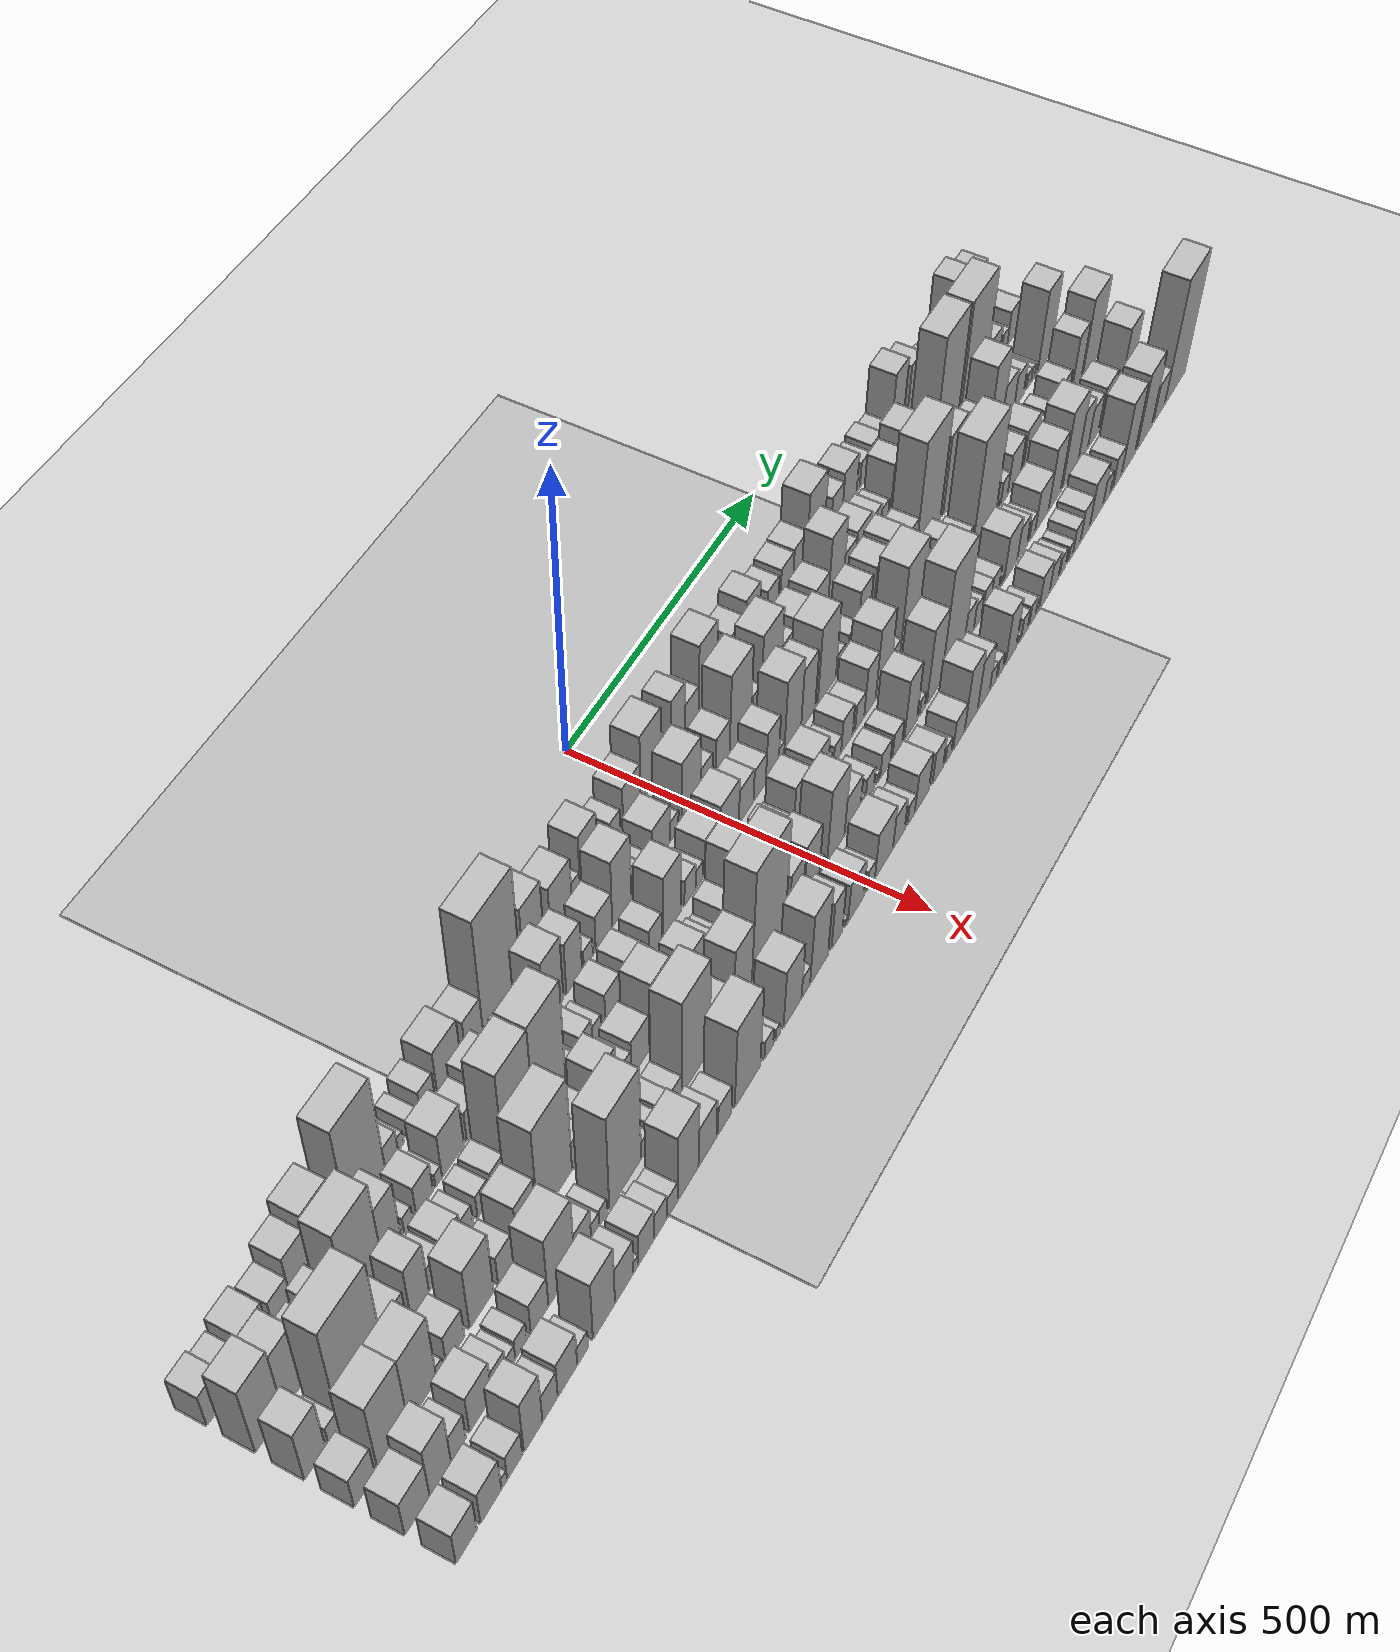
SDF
<?xml version="1.0" encoding="utf-8"?>

<sdf version="1.6">

   <world name="default">

      <gui fullscreen="0">

         <camera name="user_camera">

            <pose>-15 0 4.57585 0 0 0</pose>

            <view_controller>orbit</view_controller>

         </camera>

      </gui>

      <scene>

         <sky>

           <clouds>

             <speed>12</speed>

           </clouds>

         </sky>

         <ambient>0.4 0.4 0.4 1</ambient>

         <background>0.7 0.7 0.7 1</background>

         <shadows>1</shadows>

      </scene>

      <gravity>0 0 -9.8066</gravity>

      <magnetic_field>6e-06 2.3e-05 -4.2e-05</magnetic_field>

      <physics default="0" name="default_physics" type="ode">

         <ode>

            <solver>

               <type>quick</type>

               <iters>10</iters>

               <sor>1.0</sor>

               <use_dynamic_moi_rescaling>0</use_dynamic_moi_rescaling>

            </solver>

            <constraints>

               <cfm>0</cfm>

               <erp>0.2</erp>

               <contact_max_correcting_vel>100</contact_max_correcting_vel>

               <contact_surface_layer>0.001</contact_surface_layer>

            </constraints>

         </ode>

         <max_step_size>0.004</max_step_size>

         <real_time_factor>1</real_time_factor>

         <real_time_update_rate>250</real_time_update_rate>

      </physics>

      <light name="sun" type="directional">

         <cast_shadows>1</cast_shadows>

         <pose>0 0 10 0 0 0</pose>

         <diffuse>0.8 0.8 0.8 1</diffuse>

         <specular>0.2 0.2 0.2 1</specular>

         <attenuation>

            <range>1000</range>

            <constant>0.9</constant>

            <linear>0.01</linear>

            <quadratic>0.001</quadratic>

         </attenuation>

         <direction>-0.5 0.1 -0.9</direction>

      </light>

      <include>

         <name>ground_plane_1</name>

         <uri>model://HANNAS_ground_plane</uri>

         <pose>0 0 0  0 0 0</pose>

      </include>

      <include>

         <name>ground_plane_2</name>

         <uri>model://HANNAS_ground_plane</uri>

         <pose>100 0 0  0 0 0</pose>

      </include>

      <model name="building_1">

         <static>1</static>

         <pose frame="">100.0000 -921.6706 0 0.000000 0.000000 0.000000</pose>

         <link name="link">

            <pose frame="">0 0 34.50 0 0 0</pose>

            <collision name="collision">

               <geometry>

                  <box>

                     <size>40.0000 36.6587 69.0000</size>

                  </box>

               </geometry>

               <max_contacts>10</max_contacts>

               <surface>

                  <contact>

                     <ode/>

                  </contact>

                  <bounce/>

                  <friction>

                     <torsional>

                        <ode/>

                     </torsional>

                     <ode/>

                  </friction>

               </surface>

            </collision>

            <visual name="visual">

               <cast_shadows>0</cast_shadows>

               <geometry>

                  <box>

                     <size>40.0000 36.6587 69.0000</size>

                  </box>

               </geometry>

               <material>

                  <script>

                     <uri>model://HANNAS_wall/materials/scripts</uri>

                     <uri>model://HANNAS_wall/materials/textures</uri>

                     <name>vrc/HANNAS_wall</name>

                  </script>

               </material>

            </visual>

            <self_collide>0</self_collide>

            <enable_wind>0</enable_wind>

            <kinematic>0</kinematic>

         </link>

      </model>

      <model name="building_2">

         <static>1</static>

         <pose frame="">100.0000 -887.4800 0 0.000000 0.000000 0.000000</pose>

         <link name="link">

            <pose frame="">0 0 28.50 0 0 0</pose>

            <collision name="collision">

               <geometry>

                  <box>

                     <size>40.0000 31.7225 57.0000</size>

                  </box>

               </geometry>

               <max_contacts>10</max_contacts>

               <surface>

                  <contact>

                     <ode/>

                  </contact>

                  <bounce/>

                  <friction>

                     <torsional>

                        <ode/>

                     </torsional>

                     <ode/>

                  </friction>

               </surface>

            </collision>

            <visual name="visual">

               <cast_shadows>0</cast_shadows>

               <geometry>

                  <box>

                     <size>40.0000 31.7225 57.0000</size>

                  </box>

               </geometry>

               <material>

                  <script>

                     <uri>model://HANNAS_wall/materials/scripts</uri>

                     <uri>model://HANNAS_wall/materials/textures</uri>

                     <name>vrc/HANNAS_wall</name>

                  </script>

               </material>

            </visual>

            <self_collide>0</self_collide>

            <enable_wind>0</enable_wind>

            <kinematic>0</kinematic>

         </link>

      </model>

      <model name="building_3">

         <static>1</static>

         <pose frame="">100.0000 -847.2371 0 0.000000 0.000000 0.000000</pose>

         <link name="link">

            <pose frame="">0 0 39.00 0 0 0</pose>

            <collision name="collision">

               <geometry>

                  <box>

                     <size>40.0000 42.7632 78.0000</size>

                  </box>

               </geometry>

               <max_contacts>10</max_contacts>

               <surface>

                  <contact>

                     <ode/>

                  </contact>

                  <bounce/>

                  <friction>

                     <torsional>

                        <ode/>

                     </torsional>

                     <ode/>

                  </friction>

               </surface>

            </collision>

            <visual name="visual">

               <cast_shadows>0</cast_shadows>

               <geometry>

                  <box>

                     <size>40.0000 42.7632 78.0000</size>

                  </box>

               </geometry>

               <material>

                  <script>

                     <uri>model://HANNAS_wall/materials/scripts</uri>

                     <uri>model://HANNAS_wall/materials/textures</uri>

                     <name>vrc/HANNAS_wall</name>

                  </script>

               </material>

            </visual>

            <self_collide>0</self_collide>

            <enable_wind>0</enable_wind>

            <kinematic>0</kinematic>

         </link>

      </model>

      <model name="building_4">

         <static>1</static>

         <pose frame="">100.0000 -800.7654 0 0.000000 0.000000 0.000000</pose>

         <link name="link">

            <pose frame="">0 0 30.00 0 0 0</pose>

            <collision name="collision">

               <geometry>

                  <box>

                     <size>40.0000 34.1802 60.0000</size>

                  </box>

               </geometry>

               <max_contacts>10</max_contacts>

               <surface>

                  <contact>

                     <ode/>

                  </contact>

                  <bounce/>

                  <friction>

                     <torsional>

                        <ode/>

                     </torsional>

                     <ode/>

                  </friction>

               </surface>

            </collision>

            <visual name="visual">

               <cast_shadows>0</cast_shadows>

               <geometry>

                  <box>

                     <size>40.0000 34.1802 60.0000</size>

                  </box>

               </geometry>

               <material>

                  <script>

                     <uri>model://HANNAS_wall/materials/scripts</uri>

                     <uri>model://HANNAS_wall/materials/textures</uri>

                     <name>vrc/HANNAS_wall</name>

                  </script>

               </material>

            </visual>

            <self_collide>0</self_collide>

            <enable_wind>0</enable_wind>

            <kinematic>0</kinematic>

         </link>

      </model>

      <model name="building_5">

         <static>1</static>

         <pose frame="">100.0000 -763.9253 0 0.000000 0.000000 0.000000</pose>

         <link name="link">

            <pose frame="">0 0 49.50 0 0 0</pose>

            <collision name="collision">

               <geometry>

                  <box>

                     <size>40.0000 39.5001 99.0000</size>

                  </box>

               </geometry>

               <max_contacts>10</max_contacts>

               <surface>

                  <contact>

                     <ode/>

                  </contact>

                  <bounce/>

                  <friction>

                     <torsional>

                        <ode/>

                     </torsional>

                     <ode/>

                  </friction>

               </surface>

            </collision>

            <visual name="visual">

               <cast_shadows>0</cast_shadows>

               <geometry>

                  <box>

                     <size>40.0000 39.5001 99.0000</size>

                  </box>

               </geometry>

               <material>

                  <script>

                     <uri>model://HANNAS_wall/materials/scripts</uri>

                     <uri>model://HANNAS_wall/materials/textures</uri>

                     <name>vrc/HANNAS_wall</name>

                  </script>

               </material>

            </visual>

            <self_collide>0</self_collide>

            <enable_wind>0</enable_wind>

            <kinematic>0</kinematic>

         </link>

      </model>

      <model name="building_6">

         <static>1</static>

         <pose frame="">100.0000 -719.1027 0 0.000000 0.000000 0.000000</pose>

         <link name="link">

            <pose frame="">0 0 64.50 0 0 0</pose>

            <collision name="collision">

               <geometry>

                  <box>

                     <size>40.0000 50.1451 129.0000</size>

                  </box>

               </geometry>

               <max_contacts>10</max_contacts>

               <surface>

                  <contact>

                     <ode/>

                  </contact>

                  <bounce/>

                  <friction>

                     <torsional>

                        <ode/>

                     </torsional>

                     <ode/>

                  </friction>

               </surface>

            </collision>

            <visual name="visual">

               <cast_shadows>0</cast_shadows>

               <geometry>

                  <box>

                     <size>40.0000 50.1451 129.0000</size>

                  </box>

               </geometry>

               <material>

                  <script>

                     <uri>model://HANNAS_wall/materials/scripts</uri>

                     <uri>model://HANNAS_wall/materials/textures</uri>

                     <name>vrc/HANNAS_wall</name>

                  </script>

               </material>

            </visual>

            <self_collide>0</self_collide>

            <enable_wind>0</enable_wind>

            <kinematic>0</kinematic>

         </link>

      </model>

      <model name="building_7">

         <static>1</static>

         <pose frame="">100.0000 -684.6396 0 0.000000 0.000000 0.000000</pose>

         <link name="link">

            <pose frame="">0 0 16.50 0 0 0</pose>

            <collision name="collision">

               <geometry>

                  <box>

                     <size>40.0000 18.7811 33.0000</size>

                  </box>

               </geometry>

               <max_contacts>10</max_contacts>

               <surface>

                  <contact>

                     <ode/>

                  </contact>

                  <bounce/>

                  <friction>

                     <torsional>

                        <ode/>

                     </torsional>

                     <ode/>

                  </friction>

               </surface>

            </collision>

            <visual name="visual">

               <cast_shadows>0</cast_shadows>

               <geometry>

                  <box>

                     <size>40.0000 18.7811 33.0000</size>

                  </box>

               </geometry>

               <material>

                  <script>

                     <uri>model://HANNAS_wall/materials/scripts</uri>

                     <uri>model://HANNAS_wall/materials/textures</uri>

                     <name>vrc/HANNAS_wall</name>

                  </script>

               </material>

            </visual>

            <self_collide>0</self_collide>

            <enable_wind>0</enable_wind>

            <kinematic>0</kinematic>

         </link>

      </model>

      <model name="building_8">

         <static>1</static>

         <pose frame="">100.0000 -638.2835 0 0.000000 0.000000 0.000000</pose>

         <link name="link">

            <pose frame="">0 0 97.50 0 0 0</pose>

            <collision name="collision">

               <geometry>

                  <box>

                     <size>40.0000 73.9311 195.0000</size>

                  </box>

               </geometry>

               <max_contacts>10</max_contacts>

               <surface>

                  <contact>

                     <ode/>

                  </contact>

                  <bounce/>

                  <friction>

                     <torsional>

                        <ode/>

                     </torsional>

                     <ode/>

                  </friction>

               </surface>

            </collision>

            <visual name="visual">

               <cast_shadows>0</cast_shadows>

               <geometry>

                  <box>

                     <size>40.0000 73.9311 195.0000</size>

                  </box>

               </geometry>

               <material>

                  <script>

                     <uri>model://HANNAS_wall/materials/scripts</uri>

                     <uri>model://HANNAS_wall/materials/textures</uri>

                     <name>vrc/HANNAS_wall</name>

                  </script>

               </material>

            </visual>

            <self_collide>0</self_collide>

            <enable_wind>0</enable_wind>

            <kinematic>0</kinematic>

         </link>

      </model>

      <model name="building_9">

         <static>1</static>

         <pose frame="">100.0000 -588.3458 0 0.000000 0.000000 0.000000</pose>

         <link name="link">

            <pose frame="">0 0 22.50 0 0 0</pose>

            <collision name="collision">

               <geometry>

                  <box>

                     <size>40.0000 25.9444 45.0000</size>

                  </box>

               </geometry>

               <max_contacts>10</max_contacts>

               <surface>

                  <contact>

                     <ode/>

                  </contact>

                  <bounce/>

                  <friction>

                     <torsional>

                        <ode/>

                     </torsional>

                     <ode/>

                  </friction>

               </surface>

            </collision>

            <visual name="visual">

               <cast_shadows>0</cast_shadows>

               <geometry>

                  <box>

                     <size>40.0000 25.9444 45.0000</size>

                  </box>

               </geometry>

               <material>

                  <script>

                     <uri>model://HANNAS_wall/materials/scripts</uri>

                     <uri>model://HANNAS_wall/materials/textures</uri>

                     <name>vrc/HANNAS_wall</name>

                  </script>

               </material>

            </visual>

            <self_collide>0</self_collide>

            <enable_wind>0</enable_wind>

            <kinematic>0</kinematic>

         </link>

      </model>

      <model name="building_10">

         <static>1</static>

         <pose frame="">100.0000 -569.4382 0 0.000000 0.000000 0.000000</pose>

         <link name="link">

            <pose frame="">0 0 13.50 0 0 0</pose>

            <collision name="collision">

               <geometry>

                  <box>

                     <size>40.0000 11.8707 27.0000</size>

                  </box>

               </geometry>

               <max_contacts>10</max_contacts>

               <surface>

                  <contact>

                     <ode/>

                  </contact>

                  <bounce/>

                  <friction>

                     <torsional>

                        <ode/>

                     </torsional>

                     <ode/>

                  </friction>

               </surface>

            </collision>

            <visual name="visual">

               <cast_shadows>0</cast_shadows>

               <geometry>

                  <box>

                     <size>40.0000 11.8707 27.0000</size>

                  </box>

               </geometry>

               <material>

                  <script>

                     <uri>model://HANNAS_wall/materials/scripts</uri>

                     <uri>model://HANNAS_wall/materials/textures</uri>

                     <name>vrc/HANNAS_wall</name>

                  </script>

               </material>

            </visual>

            <self_collide>0</self_collide>

            <enable_wind>0</enable_wind>

            <kinematic>0</kinematic>

         </link>

      </model>

      <model name="building_11">

         <static>1</static>

         <pose frame="">100.0000 -545.1562 0 0.000000 0.000000 0.000000</pose>

         <link name="link">

            <pose frame="">0 0 18.00 0 0 0</pose>

            <collision name="collision">

               <geometry>

                  <box>

                     <size>40.0000 20.6934 36.0000</size>

                  </box>

               </geometry>

               <max_contacts>10</max_contacts>

               <surface>

                  <contact>

                     <ode/>

                  </contact>

                  <bounce/>

                  <friction>

                     <torsional>

                        <ode/>

                     </torsional>

                     <ode/>

                  </friction>

               </surface>

            </collision>

            <visual name="visual">

               <cast_shadows>0</cast_shadows>

               <geometry>

                  <box>

                     <size>40.0000 20.6934 36.0000</size>

                  </box>

               </geometry>

               <material>

                  <script>

                     <uri>model://HANNAS_wall/materials/scripts</uri>

                     <uri>model://HANNAS_wall/materials/textures</uri>

                     <name>vrc/HANNAS_wall</name>

                  </script>

               </material>

            </visual>

            <self_collide>0</self_collide>

            <enable_wind>0</enable_wind>

            <kinematic>0</kinematic>

         </link>

      </model>

      <model name="building_12">

         <static>1</static>

         <pose frame="">100.0000 -513.1428 0 0.000000 0.000000 0.000000</pose>

         <link name="link">

            <pose frame="">0 0 27.00 0 0 0</pose>

            <collision name="collision">

               <geometry>

                  <box>

                     <size>40.0000 29.3333 54.0000</size>

                  </box>

               </geometry>

               <max_contacts>10</max_contacts>

               <surface>

                  <contact>

                     <ode/>

                  </contact>

                  <bounce/>

                  <friction>

                     <torsional>

                        <ode/>

                     </torsional>

                     <ode/>

                  </friction>

               </surface>

            </collision>

            <visual name="visual">

               <cast_shadows>0</cast_shadows>

               <geometry>

                  <box>

                     <size>40.0000 29.3333 54.0000</size>

                  </box>

               </geometry>

               <material>

                  <script>

                     <uri>model://HANNAS_wall/materials/scripts</uri>

                     <uri>model://HANNAS_wall/materials/textures</uri>

                     <name>vrc/HANNAS_wall</name>

                  </script>

               </material>

            </visual>

            <self_collide>0</self_collide>

            <enable_wind>0</enable_wind>

            <kinematic>0</kinematic>

         </link>

      </model>

      <model name="building_13">

         <static>1</static>

         <pose frame="">100.0000 -468.4265 0 0.000000 0.000000 0.000000</pose>

         <link name="link">

            <pose frame="">0 0 43.50 0 0 0</pose>

            <collision name="collision">

               <geometry>

                  <box>

                     <size>40.0000 50.0993 87.0000</size>

                  </box>

               </geometry>

               <max_contacts>10</max_contacts>

               <surface>

                  <contact>

                     <ode/>

                  </contact>

                  <bounce/>

                  <friction>

                     <torsional>

                        <ode/>

                     </torsional>

                     <ode/>

                  </friction>

               </surface>

            </collision>

            <visual name="visual">

               <cast_shadows>0</cast_shadows>

               <geometry>

                  <box>

                     <size>40.0000 50.0993 87.0000</size>

                  </box>

               </geometry>

               <material>

                  <script>

                     <uri>model://HANNAS_wall/materials/scripts</uri>

                     <uri>model://HANNAS_wall/materials/textures</uri>

                     <name>vrc/HANNAS_wall</name>

                  </script>

               </material>

            </visual>

            <self_collide>0</self_collide>

            <enable_wind>0</enable_wind>

            <kinematic>0</kinematic>

         </link>

      </model>

      <model name="building_14">

         <static>1</static>

         <pose frame="">100.0000 -414.6459 0 0.000000 0.000000 0.000000</pose>

         <link name="link">

            <pose frame="">0 0 33.00 0 0 0</pose>

            <collision name="collision">

               <geometry>

                  <box>

                     <size>40.0000 37.4620 66.0000</size>

                  </box>

               </geometry>

               <max_contacts>10</max_contacts>

               <surface>

                  <contact>

                     <ode/>

                  </contact>

                  <bounce/>

                  <friction>

                     <torsional>

                        <ode/>

                     </torsional>

                     <ode/>

                  </friction>

               </surface>

            </collision>

            <visual name="visual">

               <cast_shadows>0</cast_shadows>

               <geometry>

                  <box>

                     <size>40.0000 37.4620 66.0000</size>

                  </box>

               </geometry>

               <material>

                  <script>

                     <uri>model://HANNAS_wall/materials/scripts</uri>

                     <uri>model://HANNAS_wall/materials/textures</uri>

                     <name>vrc/HANNAS_wall</name>

                  </script>

               </material>

            </visual>

            <self_collide>0</self_collide>

            <enable_wind>0</enable_wind>

            <kinematic>0</kinematic>

         </link>

      </model>

      <model name="building_15">

         <static>1</static>

         <pose frame="">100.0000 -353.8489 0 0.000000 0.000000 0.000000</pose>

         <link name="link">

            <pose frame="">0 0 108.00 0 0 0</pose>

            <collision name="collision">

               <geometry>

                  <box>

                     <size>40.0000 84.1318 216.0000</size>

                  </box>

               </geometry>

               <max_contacts>10</max_contacts>

               <surface>

                  <contact>

                     <ode/>

                  </contact>

                  <bounce/>

                  <friction>

                     <torsional>

                        <ode/>

                     </torsional>

                     <ode/>

                  </friction>

               </surface>

            </collision>

            <visual name="visual">

               <cast_shadows>0</cast_shadows>

               <geometry>

                  <box>

                     <size>40.0000 84.1318 216.0000</size>

                  </box>

               </geometry>

               <material>

                  <script>

                     <uri>model://HANNAS_wall/materials/scripts</uri>

                     <uri>model://HANNAS_wall/materials/textures</uri>

                     <name>vrc/HANNAS_wall</name>

                  </script>

               </material>

            </visual>

            <self_collide>0</self_collide>

            <enable_wind>0</enable_wind>

            <kinematic>0</kinematic>

         </link>

      </model>

      <model name="building_16">

         <static>1</static>

         <pose frame="">100.0000 -308.0549 0 0.000000 0.000000 0.000000</pose>

         <link name="link">

            <pose frame="">0 0 9.00 0 0 0</pose>

            <collision name="collision">

               <geometry>

                  <box>

                     <size>40.0000 7.4563 18.0000</size>

                  </box>

               </geometry>

               <max_contacts>10</max_contacts>

               <surface>

                  <contact>

                     <ode/>

                  </contact>

                  <bounce/>

                  <friction>

                     <torsional>

                        <ode/>

                     </torsional>

                     <ode/>

                  </friction>

               </surface>

            </collision>

            <visual name="visual">

               <cast_shadows>0</cast_shadows>

               <geometry>

                  <box>

                     <size>40.0000 7.4563 18.0000</size>

                  </box>

               </geometry>

               <material>

                  <script>

                     <uri>model://HANNAS_wall/materials/scripts</uri>

                     <uri>model://HANNAS_wall/materials/textures</uri>

                     <name>vrc/HANNAS_wall</name>

                  </script>

               </material>

            </visual>

            <self_collide>0</self_collide>

            <enable_wind>0</enable_wind>

            <kinematic>0</kinematic>

         </link>

      </model>

      <model name="building_17">

         <static>1</static>

         <pose frame="">100.0000 -281.3452 0 0.000000 0.000000 0.000000</pose>

         <link name="link">

            <pose frame="">0 0 61.50 0 0 0</pose>

            <collision name="collision">

               <geometry>

                  <box>

                     <size>40.0000 45.9632 123.0000</size>

                  </box>

               </geometry>

               <max_contacts>10</max_contacts>

               <surface>

                  <contact>

                     <ode/>

                  </contact>

                  <bounce/>

                  <friction>

                     <torsional>

                        <ode/>

                     </torsional>

                     <ode/>

                  </friction>

               </surface>

            </collision>

            <visual name="visual">

               <cast_shadows>0</cast_shadows>

               <geometry>

                  <box>

                     <size>40.0000 45.9632 123.0000</size>

                  </box>

               </geometry>

               <material>

                  <script>

                     <uri>model://HANNAS_wall/materials/scripts</uri>

                     <uri>model://HANNAS_wall/materials/textures</uri>

                     <name>vrc/HANNAS_wall</name>

                  </script>

               </material>

            </visual>

            <self_collide>0</self_collide>

            <enable_wind>0</enable_wind>

            <kinematic>0</kinematic>

         </link>

      </model>

      <model name="building_18">

         <static>1</static>

         <pose frame="">100.0000 -248.4081 0 0.000000 0.000000 0.000000</pose>

         <link name="link">

            <pose frame="">0 0 10.50 0 0 0</pose>

            <collision name="collision">

               <geometry>

                  <box>

                     <size>40.0000 9.9111 21.0000</size>

                  </box>

               </geometry>

               <max_contacts>10</max_contacts>

               <surface>

                  <contact>

                     <ode/>

                  </contact>

                  <bounce/>

                  <friction>

                     <torsional>

                        <ode/>

                     </torsional>

                     <ode/>

                  </friction>

               </surface>

            </collision>

            <visual name="visual">

               <cast_shadows>0</cast_shadows>

               <geometry>

                  <box>

                     <size>40.0000 9.9111 21.0000</size>

                  </box>

               </geometry>

               <material>

                  <script>

                     <uri>model://HANNAS_wall/materials/scripts</uri>

                     <uri>model://HANNAS_wall/materials/textures</uri>

                     <name>vrc/HANNAS_wall</name>

                  </script>

               </material>

            </visual>

            <self_collide>0</self_collide>

            <enable_wind>0</enable_wind>

            <kinematic>0</kinematic>

         </link>

      </model>

      <model name="building_19">

         <static>1</static>

         <pose frame="">100.0000 -218.5129 0 0.000000 0.000000 0.000000</pose>

         <link name="link">

            <pose frame="">0 0 43.50 0 0 0</pose>

            <collision name="collision">

               <geometry>

                  <box>

                     <size>40.0000 49.8792 87.0000</size>

                  </box>

               </geometry>

               <max_contacts>10</max_contacts>

               <surface>

                  <contact>

                     <ode/>

                  </contact>

                  <bounce/>

                  <friction>

                     <torsional>

                        <ode/>

                     </torsional>

                     <ode/>

                  </friction>

               </surface>

            </collision>

            <visual name="visual">

               <cast_shadows>0</cast_shadows>

               <geometry>

                  <box>

                     <size>40.0000 49.8792 87.0000</size>

                  </box>

               </geometry>

               <material>

                  <script>

                     <uri>model://HANNAS_wall/materials/scripts</uri>

                     <uri>model://HANNAS_wall/materials/textures</uri>

                     <name>vrc/HANNAS_wall</name>

                  </script>

               </material>

            </visual>

            <self_collide>0</self_collide>

            <enable_wind>0</enable_wind>

            <kinematic>0</kinematic>

         </link>

      </model>

      <model name="building_20">

         <static>1</static>

         <pose frame="">100.0000 -183.7826 0 0.000000 0.000000 0.000000</pose>

         <link name="link">

            <pose frame="">0 0 18.00 0 0 0</pose>

            <collision name="collision">

               <geometry>

                  <box>

                     <size>40.0000 19.5815 36.0000</size>

                  </box>

               </geometry>

               <max_contacts>10</max_contacts>

               <surface>

                  <contact>

                     <ode/>

                  </contact>

                  <bounce/>

                  <friction>

                     <torsional>

                        <ode/>

                     </torsional>

                     <ode/>

                  </friction>

               </surface>

            </collision>

            <visual name="visual">

               <cast_shadows>0</cast_shadows>

               <geometry>

                  <box>

                     <size>40.0000 19.5815 36.0000</size>

                  </box>

               </geometry>

               <material>

                  <script>

                     <uri>model://HANNAS_wall/materials/scripts</uri>

                     <uri>model://HANNAS_wall/materials/textures</uri>

                     <name>vrc/HANNAS_wall</name>

                  </script>

               </material>

            </visual>

            <self_collide>0</self_collide>

            <enable_wind>0</enable_wind>

            <kinematic>0</kinematic>

         </link>

      </model>

      <model name="building_21">

         <static>1</static>

         <pose frame="">100.0000 -153.1619 0 0.000000 0.000000 0.000000</pose>

         <link name="link">

            <pose frame="">0 0 52.50 0 0 0</pose>

            <collision name="collision">

               <geometry>

                  <box>

                     <size>40.0000 41.6599 105.0000</size>

                  </box>

               </geometry>

               <max_contacts>10</max_contacts>

               <surface>

                  <contact>

                     <ode/>

                  </contact>

                  <bounce/>

                  <friction>

                     <torsional>

                        <ode/>

                     </torsional>

                     <ode/>

                  </friction>

               </surface>

            </collision>

            <visual name="visual">

               <cast_shadows>0</cast_shadows>

               <geometry>

                  <box>

                     <size>40.0000 41.6599 105.0000</size>

                  </box>

               </geometry>

               <material>

                  <script>

                     <uri>model://HANNAS_wall/materials/scripts</uri>

                     <uri>model://HANNAS_wall/materials/textures</uri>

                     <name>vrc/HANNAS_wall</name>

                  </script>

               </material>

            </visual>

            <self_collide>0</self_collide>

            <enable_wind>0</enable_wind>

            <kinematic>0</kinematic>

         </link>

      </model>

      <model name="building_22">

         <static>1</static>

         <pose frame="">100.0000 -120.5780 0 0.000000 0.000000 0.000000</pose>

         <link name="link">

            <pose frame="">0 0 21.00 0 0 0</pose>

            <collision name="collision">

               <geometry>

                  <box>

                     <size>40.0000 23.5081 42.0000</size>

                  </box>

               </geometry>

               <max_contacts>10</max_contacts>

               <surface>

                  <contact>

                     <ode/>

                  </contact>

                  <bounce/>

                  <friction>

                     <torsional>

                        <ode/>

                     </torsional>

                     <ode/>

                  </friction>

               </surface>

            </collision>

            <visual name="visual">

               <cast_shadows>0</cast_shadows>

               <geometry>

                  <box>

                     <size>40.0000 23.5081 42.0000</size>

                  </box>

               </geometry>

               <material>

                  <script>

                     <uri>model://HANNAS_wall/materials/scripts</uri>

                     <uri>model://HANNAS_wall/materials/textures</uri>

                     <name>vrc/HANNAS_wall</name>

                  </script>

               </material>

            </visual>

            <self_collide>0</self_collide>

            <enable_wind>0</enable_wind>

            <kinematic>0</kinematic>

         </link>

      </model>

      <model name="building_23">

         <static>1</static>

         <pose frame="">100.0000 -104.7559 0 0.000000 0.000000 0.000000</pose>

         <link name="link">

            <pose frame="">0 0 9.00 0 0 0</pose>

            <collision name="collision">

               <geometry>

                  <box>

                     <size>40.0000 8.1360 18.0000</size>

                  </box>

               </geometry>

               <max_contacts>10</max_contacts>

               <surface>

                  <contact>

                     <ode/>

                  </contact>

                  <bounce/>

                  <friction>

                     <torsional>

                        <ode/>

                     </torsional>

                     <ode/>

                  </friction>

               </surface>

            </collision>

            <visual name="visual">

               <cast_shadows>0</cast_shadows>

               <geometry>

                  <box>

                     <size>40.0000 8.1360 18.0000</size>

                  </box>

               </geometry>

               <material>

                  <script>

                     <uri>model://HANNAS_wall/materials/scripts</uri>

                     <uri>model://HANNAS_wall/materials/textures</uri>

                     <name>vrc/HANNAS_wall</name>

                  </script>

               </material>

            </visual>

            <self_collide>0</self_collide>

            <enable_wind>0</enable_wind>

            <kinematic>0</kinematic>

         </link>

      </model>

      <model name="building_24">

         <static>1</static>

         <pose frame="">100.0000 -88.2923 0 0.000000 0.000000 0.000000</pose>

         <link name="link">

            <pose frame="">0 0 22.50 0 0 0</pose>

            <collision name="collision">

               <geometry>

                  <box>

                     <size>40.0000 24.7913 45.0000</size>

                  </box>

               </geometry>

               <max_contacts>10</max_contacts>

               <surface>

                  <contact>

                     <ode/>

                  </contact>

                  <bounce/>

                  <friction>

                     <torsional>

                        <ode/>

                     </torsional>

                     <ode/>

                  </friction>

               </surface>

            </collision>

            <visual name="visual">

               <cast_shadows>0</cast_shadows>

               <geometry>

                  <box>

                     <size>40.0000 24.7913 45.0000</size>

                  </box>

               </geometry>

               <material>

                  <script>

                     <uri>model://HANNAS_wall/materials/scripts</uri>

                     <uri>model://HANNAS_wall/materials/textures</uri>

                     <name>vrc/HANNAS_wall</name>

                  </script>

               </material>

            </visual>

            <self_collide>0</self_collide>

            <enable_wind>0</enable_wind>

            <kinematic>0</kinematic>

         </link>

      </model>

      <model name="building_25">

         <static>1</static>

         <pose frame="">100.0000 -48.3048 0 0.000000 0.000000 0.000000</pose>

         <link name="link">

            <pose frame="">0 0 39.00 0 0 0</pose>

            <collision name="collision">

               <geometry>

                  <box>

                     <size>40.0000 43.1838 78.0000</size>

                  </box>

               </geometry>

               <max_contacts>10</max_contacts>

               <surface>

                  <contact>

                     <ode/>

                  </contact>

                  <bounce/>

                  <friction>

                     <torsional>

                        <ode/>

                     </torsional>

                     <ode/>

                  </friction>

               </surface>

            </collision>

            <visual name="visual">

               <cast_shadows>0</cast_shadows>

               <geometry>

                  <box>

                     <size>40.0000 43.1838 78.0000</size>

                  </box>

               </geometry>

               <material>

                  <script>

                     <uri>model://HANNAS_wall/materials/scripts</uri>

                     <uri>model://HANNAS_wall/materials/textures</uri>

                     <name>vrc/HANNAS_wall</name>

                  </script>

               </material>

            </visual>

            <self_collide>0</self_collide>

            <enable_wind>0</enable_wind>

            <kinematic>0</kinematic>

         </link>

      </model>

      <model name="building_26">

         <static>1</static>

         <pose frame="">100.0000 -0.9297 0 0.000000 0.000000 0.000000</pose>

         <link name="link">

            <pose frame="">0 0 64.50 0 0 0</pose>

            <collision name="collision">

               <geometry>

                  <box>

                     <size>40.0000 51.5664 129.0000</size>

                  </box>

               </geometry>

               <max_contacts>10</max_contacts>

               <surface>

                  <contact>

                     <ode/>

                  </contact>

                  <bounce/>

                  <friction>

                     <torsional>

                        <ode/>

                     </torsional>

                     <ode/>

                  </friction>

               </surface>

            </collision>

            <visual name="visual">

               <cast_shadows>0</cast_shadows>

               <geometry>

                  <box>

                     <size>40.0000 51.5664 129.0000</size>

                  </box>

               </geometry>

               <material>

                  <script>

                     <uri>model://HANNAS_wall/materials/scripts</uri>

                     <uri>model://HANNAS_wall/materials/textures</uri>

                     <name>vrc/HANNAS_wall</name>

                  </script>

               </material>

            </visual>

            <self_collide>0</self_collide>

            <enable_wind>0</enable_wind>

            <kinematic>0</kinematic>

         </link>

      </model>

      <model name="building_27">

         <static>1</static>

         <pose frame="">100.0000 38.0958 0 0.000000 0.000000 0.000000</pose>

         <link name="link">

            <pose frame="">0 0 22.50 0 0 0</pose>

            <collision name="collision">

               <geometry>

                  <box>

                     <size>40.0000 26.4845 45.0000</size>

                  </box>

               </geometry>

               <max_contacts>10</max_contacts>

               <surface>

                  <contact>

                     <ode/>

                  </contact>

                  <bounce/>

                  <friction>

                     <torsional>

                        <ode/>

                     </torsional>

                     <ode/>

                  </friction>

               </surface>

            </collision>

            <visual name="visual">

               <cast_shadows>0</cast_shadows>

               <geometry>

                  <box>

                     <size>40.0000 26.4845 45.0000</size>

                  </box>

               </geometry>

               <material>

                  <script>

                     <uri>model://HANNAS_wall/materials/scripts</uri>

                     <uri>model://HANNAS_wall/materials/textures</uri>

                     <name>vrc/HANNAS_wall</name>

                  </script>

               </material>

            </visual>

            <self_collide>0</self_collide>

            <enable_wind>0</enable_wind>

            <kinematic>0</kinematic>

         </link>

      </model>

      <model name="building_28">

         <static>1</static>

         <pose frame="">100.0000 68.7779 0 0.000000 0.000000 0.000000</pose>

         <link name="link">

            <pose frame="">0 0 55.50 0 0 0</pose>

            <collision name="collision">

               <geometry>

                  <box>

                     <size>40.0000 34.8797 111.0000</size>

                  </box>

               </geometry>

               <max_contacts>10</max_contacts>

               <surface>

                  <contact>

                     <ode/>

                  </contact>

                  <bounce/>

                  <friction>

                     <torsional>

                        <ode/>

                     </torsional>

                     <ode/>

                  </friction>

               </surface>

            </collision>

            <visual name="visual">

               <cast_shadows>0</cast_shadows>

               <geometry>

                  <box>

                     <size>40.0000 34.8797 111.0000</size>

                  </box>

               </geometry>

               <material>

                  <script>

                     <uri>model://HANNAS_wall/materials/scripts</uri>

                     <uri>model://HANNAS_wall/materials/textures</uri>

                     <name>vrc/HANNAS_wall</name>

                  </script>

               </material>

            </visual>

            <self_collide>0</self_collide>

            <enable_wind>0</enable_wind>

            <kinematic>0</kinematic>

         </link>

      </model>

      <model name="building_29">

         <static>1</static>

         <pose frame="">100.0000 104.3803 0 0.000000 0.000000 0.000000</pose>

         <link name="link">

            <pose frame="">0 0 33.00 0 0 0</pose>

            <collision name="collision">

               <geometry>

                  <box>

                     <size>40.0000 36.3250 66.0000</size>

                  </box>

               </geometry>

               <max_contacts>10</max_contacts>

               <surface>

                  <contact>

                     <ode/>

                  </contact>

                  <bounce/>

                  <friction>

                     <torsional>

                        <ode/>

                     </torsional>

                     <ode/>

                  </friction>

               </surface>

            </collision>

            <visual name="visual">

               <cast_shadows>0</cast_shadows>

               <geometry>

                  <box>

                     <size>40.0000 36.3250 66.0000</size>

                  </box>

               </geometry>

               <material>

                  <script>

                     <uri>model://HANNAS_wall/materials/scripts</uri>

                     <uri>model://HANNAS_wall/materials/textures</uri>

                     <name>vrc/HANNAS_wall</name>

                  </script>

               </material>

            </visual>

            <self_collide>0</self_collide>

            <enable_wind>0</enable_wind>

            <kinematic>0</kinematic>

         </link>

      </model>

      <model name="building_30">

         <static>1</static>

         <pose frame="">100.0000 146.4982 0 0.000000 0.000000 0.000000</pose>

         <link name="link">

            <pose frame="">0 0 70.50 0 0 0</pose>

            <collision name="collision">

               <geometry>

                  <box>

                     <size>40.0000 47.9109 141.0000</size>

                  </box>

               </geometry>

               <max_contacts>10</max_contacts>

               <surface>

                  <contact>

                     <ode/>

                  </contact>

                  <bounce/>

                  <friction>

                     <torsional>

                        <ode/>

                     </torsional>

                     <ode/>

                  </friction>

               </surface>

            </collision>

            <visual name="visual">

               <cast_shadows>0</cast_shadows>

               <geometry>

                  <box>

                     <size>40.0000 47.9109 141.0000</size>

                  </box>

               </geometry>

               <material>

                  <script>

                     <uri>model://HANNAS_wall/materials/scripts</uri>

                     <uri>model://HANNAS_wall/materials/textures</uri>

                     <name>vrc/HANNAS_wall</name>

                  </script>

               </material>

            </visual>

            <self_collide>0</self_collide>

            <enable_wind>0</enable_wind>

            <kinematic>0</kinematic>

         </link>

      </model>

      <model name="building_31">

         <static>1</static>

         <pose frame="">100.0000 185.6217 0 0.000000 0.000000 0.000000</pose>

         <link name="link">

            <pose frame="">0 0 28.50 0 0 0</pose>

            <collision name="collision">

               <geometry>

                  <box>

                     <size>40.0000 30.3360 57.0000</size>

                  </box>

               </geometry>

               <max_contacts>10</max_contacts>

               <surface>

                  <contact>

                     <ode/>

                  </contact>

                  <bounce/>

                  <friction>

                     <torsional>

                        <ode/>

                     </torsional>

                     <ode/>

                  </friction>

               </surface>

            </collision>

            <visual name="visual">

               <cast_shadows>0</cast_shadows>

               <geometry>

                  <box>

                     <size>40.0000 30.3360 57.0000</size>

                  </box>

               </geometry>

               <material>

                  <script>

                     <uri>model://HANNAS_wall/materials/scripts</uri>

                     <uri>model://HANNAS_wall/materials/textures</uri>

                     <name>vrc/HANNAS_wall</name>

                  </script>

               </material>

            </visual>

            <self_collide>0</self_collide>

            <enable_wind>0</enable_wind>

            <kinematic>0</kinematic>

         </link>

      </model>

      <model name="building_32">

         <static>1</static>

         <pose frame="">100.0000 228.1606 0 0.000000 0.000000 0.000000</pose>

         <link name="link">

            <pose frame="">0 0 36.00 0 0 0</pose>

            <collision name="collision">

               <geometry>

                  <box>

                     <size>40.0000 38.7418 72.0000</size>

                  </box>

               </geometry>

               <max_contacts>10</max_contacts>

               <surface>

                  <contact>

                     <ode/>

                  </contact>

                  <bounce/>

                  <friction>

                     <torsional>

                        <ode/>

                     </torsional>

                     <ode/>

                  </friction>

               </surface>

            </collision>

            <visual name="visual">

               <cast_shadows>0</cast_shadows>

               <geometry>

                  <box>

                     <size>40.0000 38.7418 72.0000</size>

                  </box>

               </geometry>

               <material>

                  <script>

                     <uri>model://HANNAS_wall/materials/scripts</uri>

                     <uri>model://HANNAS_wall/materials/textures</uri>

                     <name>vrc/HANNAS_wall</name>

                  </script>

               </material>

            </visual>

            <self_collide>0</self_collide>

            <enable_wind>0</enable_wind>

            <kinematic>0</kinematic>

         </link>

      </model>

      <model name="building_33">

         <static>1</static>

         <pose frame="">100.0000 266.7528 0 0.000000 0.000000 0.000000</pose>

         <link name="link">

            <pose frame="">0 0 49.50 0 0 0</pose>

            <collision name="collision">

               <geometry>

                  <box>

                     <size>40.0000 38.4427 99.0000</size>

                  </box>

               </geometry>

               <max_contacts>10</max_contacts>

               <surface>

                  <contact>

                     <ode/>

                  </contact>

                  <bounce/>

                  <friction>

                     <torsional>

                        <ode/>

                     </torsional>

                     <ode/>

                  </friction>

               </surface>

            </collision>

            <visual name="visual">

               <cast_shadows>0</cast_shadows>

               <geometry>

                  <box>

                     <size>40.0000 38.4427 99.0000</size>

                  </box>

               </geometry>

               <material>

                  <script>

                     <uri>model://HANNAS_wall/materials/scripts</uri>

                     <uri>model://HANNAS_wall/materials/textures</uri>

                     <name>vrc/HANNAS_wall</name>

                  </script>

               </material>

            </visual>

            <self_collide>0</self_collide>

            <enable_wind>0</enable_wind>

            <kinematic>0</kinematic>

         </link>

      </model>

      <model name="building_34">

         <static>1</static>

         <pose frame="">100.0000 297.1990 0 0.000000 0.000000 0.000000</pose>

         <link name="link">

            <pose frame="">0 0 21.00 0 0 0</pose>

            <collision name="collision">

               <geometry>

                  <box>

                     <size>40.0000 22.4496 42.0000</size>

                  </box>

               </geometry>

               <max_contacts>10</max_contacts>

               <surface>

                  <contact>

                     <ode/>

                  </contact>

                  <bounce/>

                  <friction>

                     <torsional>

                        <ode/>

                     </torsional>

                     <ode/>

                  </friction>

               </surface>

            </collision>

            <visual name="visual">

               <cast_shadows>0</cast_shadows>

               <geometry>

                  <box>

                     <size>40.0000 22.4496 42.0000</size>

                  </box>

               </geometry>

               <material>

                  <script>

                     <uri>model://HANNAS_wall/materials/scripts</uri>

                     <uri>model://HANNAS_wall/materials/textures</uri>

                     <name>vrc/HANNAS_wall</name>

                  </script>

               </material>

            </visual>

            <self_collide>0</self_collide>

            <enable_wind>0</enable_wind>

            <kinematic>0</kinematic>

         </link>

      </model>

      <model name="building_35">

         <static>1</static>

         <pose frame="">100.0000 324.4445 0 0.000000 0.000000 0.000000</pose>

         <link name="link">

            <pose frame="">0 0 28.50 0 0 0</pose>

            <collision name="collision">

               <geometry>

                  <box>

                     <size>40.0000 32.0414 57.0000</size>

                  </box>

               </geometry>

               <max_contacts>10</max_contacts>

               <surface>

                  <contact>

                     <ode/>

                  </contact>

                  <bounce/>

                  <friction>

                     <torsional>

                        <ode/>

                     </torsional>

                     <ode/>

                  </friction>

               </surface>

            </collision>

            <visual name="visual">

               <cast_shadows>0</cast_shadows>

               <geometry>

                  <box>

                     <size>40.0000 32.0414 57.0000</size>

                  </box>

               </geometry>

               <material>

                  <script>

                     <uri>model://HANNAS_wall/materials/scripts</uri>

                     <uri>model://HANNAS_wall/materials/textures</uri>

                     <name>vrc/HANNAS_wall</name>

                  </script>

               </material>

            </visual>

            <self_collide>0</self_collide>

            <enable_wind>0</enable_wind>

            <kinematic>0</kinematic>

         </link>

      </model>

      <model name="building_36">

         <static>1</static>

         <pose frame="">100.0000 363.6247 0 0.000000 0.000000 0.000000</pose>

         <link name="link">

            <pose frame="">0 0 31.50 0 0 0</pose>

            <collision name="collision">

               <geometry>

                  <box>

                     <size>40.0000 36.3191 63.0000</size>

                  </box>

               </geometry>

               <max_contacts>10</max_contacts>

               <surface>

                  <contact>

                     <ode/>

                  </contact>

                  <bounce/>

                  <friction>

                     <torsional>

                        <ode/>

                     </torsional>

                     <ode/>

                  </friction>

               </surface>

            </collision>

            <visual name="visual">

               <cast_shadows>0</cast_shadows>

               <geometry>

                  <box>

                     <size>40.0000 36.3191 63.0000</size>

                  </box>

               </geometry>

               <material>

                  <script>

                     <uri>model://HANNAS_wall/materials/scripts</uri>

                     <uri>model://HANNAS_wall/materials/textures</uri>

                     <name>vrc/HANNAS_wall</name>

                  </script>

               </material>

            </visual>

            <self_collide>0</self_collide>

            <enable_wind>0</enable_wind>

            <kinematic>0</kinematic>

         </link>

      </model>

      <model name="building_37">

         <static>1</static>

         <pose frame="">100.0000 401.1003 0 0.000000 0.000000 0.000000</pose>

         <link name="link">

            <pose frame="">0 0 33.00 0 0 0</pose>

            <collision name="collision">

               <geometry>

                  <box>

                     <size>40.0000 38.6320 66.0000</size>

                  </box>

               </geometry>

               <max_contacts>10</max_contacts>

               <surface>

                  <contact>

                     <ode/>

                  </contact>

                  <bounce/>

                  <friction>

                     <torsional>

                        <ode/>

                     </torsional>

                     <ode/>

                  </friction>

               </surface>

            </collision>

            <visual name="visual">

               <cast_shadows>0</cast_shadows>

               <geometry>

                  <box>

                     <size>40.0000 38.6320 66.0000</size>

                  </box>

               </geometry>

               <material>

                  <script>

                     <uri>model://HANNAS_wall/materials/scripts</uri>

                     <uri>model://HANNAS_wall/materials/textures</uri>

                     <name>vrc/HANNAS_wall</name>

                  </script>

               </material>

            </visual>

            <self_collide>0</self_collide>

            <enable_wind>0</enable_wind>

            <kinematic>0</kinematic>

         </link>

      </model>

      <model name="building_38">

         <static>1</static>

         <pose frame="">100.0000 446.0421 0 0.000000 0.000000 0.000000</pose>

         <link name="link">

            <pose frame="">0 0 66.00 0 0 0</pose>

            <collision name="collision">

               <geometry>

                  <box>

                     <size>40.0000 51.2516 132.0000</size>

                  </box>

               </geometry>

               <max_contacts>10</max_contacts>

               <surface>

                  <contact>

                     <ode/>

                  </contact>

                  <bounce/>

                  <friction>

                     <torsional>

                        <ode/>

                     </torsional>

                     <ode/>

                  </friction>

               </surface>

            </collision>

            <visual name="visual">

               <cast_shadows>0</cast_shadows>

               <geometry>

                  <box>

                     <size>40.0000 51.2516 132.0000</size>

                  </box>

               </geometry>

               <material>

                  <script>

                     <uri>model://HANNAS_wall/materials/scripts</uri>

                     <uri>model://HANNAS_wall/materials/textures</uri>

                     <name>vrc/HANNAS_wall</name>

                  </script>

               </material>

            </visual>

            <self_collide>0</self_collide>

            <enable_wind>0</enable_wind>

            <kinematic>0</kinematic>

         </link>

      </model>

      <model name="building_39">

         <static>1</static>

         <pose frame="">100.0000 482.2217 0 0.000000 0.000000 0.000000</pose>

         <link name="link">

            <pose frame="">0 0 19.50 0 0 0</pose>

            <collision name="collision">

               <geometry>

                  <box>

                     <size>40.0000 21.1074 39.0000</size>

                  </box>

               </geometry>

               <max_contacts>10</max_contacts>

               <surface>

                  <contact>

                     <ode/>

                  </contact>

                  <bounce/>

                  <friction>

                     <torsional>

                        <ode/>

                     </torsional>

                     <ode/>

                  </friction>

               </surface>

            </collision>

            <visual name="visual">

               <cast_shadows>0</cast_shadows>

               <geometry>

                  <box>

                     <size>40.0000 21.1074 39.0000</size>

                  </box>

               </geometry>

               <material>

                  <script>

                     <uri>model://HANNAS_wall/materials/scripts</uri>

                     <uri>model://HANNAS_wall/materials/textures</uri>

                     <name>vrc/HANNAS_wall</name>

                  </script>

               </material>

            </visual>

            <self_collide>0</self_collide>

            <enable_wind>0</enable_wind>

            <kinematic>0</kinematic>

         </link>

      </model>

      <model name="building_40">

         <static>1</static>

         <pose frame="">100.0000 510.0241 0 0.000000 0.000000 0.000000</pose>

         <link name="link">

            <pose frame="">0 0 30.00 0 0 0</pose>

            <collision name="collision">

               <geometry>

                  <box>

                     <size>40.0000 34.4973 60.0000</size>

                  </box>

               </geometry>

               <max_contacts>10</max_contacts>

               <surface>

                  <contact>

                     <ode/>

                  </contact>

                  <bounce/>

                  <friction>

                     <torsional>

                        <ode/>

                     </torsional>

                     <ode/>

                  </friction>

               </surface>

            </collision>

            <visual name="visual">

               <cast_shadows>0</cast_shadows>

               <geometry>

                  <box>

                     <size>40.0000 34.4973 60.0000</size>

                  </box>

               </geometry>

               <material>

                  <script>

                     <uri>model://HANNAS_wall/materials/scripts</uri>

                     <uri>model://HANNAS_wall/materials/textures</uri>

                     <name>vrc/HANNAS_wall</name>

                  </script>

               </material>

            </visual>

            <self_collide>0</self_collide>

            <enable_wind>0</enable_wind>

            <kinematic>0</kinematic>

         </link>

      </model>

      <model name="building_41">

         <static>1</static>

         <pose frame="">100.0000 548.7905 0 0.000000 0.000000 0.000000</pose>

         <link name="link">

            <pose frame="">0 0 37.50 0 0 0</pose>

            <collision name="collision">

               <geometry>

                  <box>

                     <size>40.0000 43.0357 75.0000</size>

                  </box>

               </geometry>

               <max_contacts>10</max_contacts>

               <surface>

                  <contact>

                     <ode/>

                  </contact>

                  <bounce/>

                  <friction>

                     <torsional>

                        <ode/>

                     </torsional>

                     <ode/>

                  </friction>

               </surface>

            </collision>

            <visual name="visual">

               <cast_shadows>0</cast_shadows>

               <geometry>

                  <box>

                     <size>40.0000 43.0357 75.0000</size>

                  </box>

               </geometry>

               <material>

                  <script>

                     <uri>model://HANNAS_wall/materials/scripts</uri>

                     <uri>model://HANNAS_wall/materials/textures</uri>

                     <name>vrc/HANNAS_wall</name>

                  </script>

               </material>

            </visual>

            <self_collide>0</self_collide>

            <enable_wind>0</enable_wind>

            <kinematic>0</kinematic>

         </link>

      </model>

      <model name="building_42">

         <static>1</static>

         <pose frame="">100.0000 575.1133 0 0.000000 0.000000 0.000000</pose>

         <link name="link">

            <pose frame="">0 0 12.00 0 0 0</pose>

            <collision name="collision">

               <geometry>

                  <box>

                     <size>40.0000 9.6099 24.0000</size>

                  </box>

               </geometry>

               <max_contacts>10</max_contacts>

               <surface>

                  <contact>

                     <ode/>

                  </contact>

                  <bounce/>

                  <friction>

                     <torsional>

                        <ode/>

                     </torsional>

                     <ode/>

                  </friction>

               </surface>

            </collision>

            <visual name="visual">

               <cast_shadows>0</cast_shadows>

               <geometry>

                  <box>

                     <size>40.0000 9.6099 24.0000</size>

                  </box>

               </geometry>

               <material>

                  <script>

                     <uri>model://HANNAS_wall/materials/scripts</uri>

                     <uri>model://HANNAS_wall/materials/textures</uri>

                     <name>vrc/HANNAS_wall</name>

                  </script>

               </material>

            </visual>

            <self_collide>0</self_collide>

            <enable_wind>0</enable_wind>

            <kinematic>0</kinematic>

         </link>

      </model>

      <model name="building_43">

         <static>1</static>

         <pose frame="">100.0000 592.8032 0 0.000000 0.000000 0.000000</pose>

         <link name="link">

            <pose frame="">0 0 24.00 0 0 0</pose>

            <collision name="collision">

               <geometry>

                  <box>

                     <size>40.0000 25.7698 48.0000</size>

                  </box>

               </geometry>

               <max_contacts>10</max_contacts>

               <surface>

                  <contact>

                     <ode/>

                  </contact>

                  <bounce/>

                  <friction>

                     <torsional>

                        <ode/>

                     </torsional>

                     <ode/>

                  </friction>

               </surface>

            </collision>

            <visual name="visual">

               <cast_shadows>0</cast_shadows>

               <geometry>

                  <box>

                     <size>40.0000 25.7698 48.0000</size>

                  </box>

               </geometry>

               <material>

                  <script>

                     <uri>model://HANNAS_wall/materials/scripts</uri>

                     <uri>model://HANNAS_wall/materials/textures</uri>

                     <name>vrc/HANNAS_wall</name>

                  </script>

               </material>

            </visual>

            <self_collide>0</self_collide>

            <enable_wind>0</enable_wind>

            <kinematic>0</kinematic>

         </link>

      </model>

      <model name="building_44">

         <static>1</static>

         <pose frame="">100.0000 626.1144 0 0.000000 0.000000 0.000000</pose>

         <link name="link">

            <pose frame="">0 0 27.00 0 0 0</pose>

            <collision name="collision">

               <geometry>

                  <box>

                     <size>40.0000 30.8526 54.0000</size>

                  </box>

               </geometry>

               <max_contacts>10</max_contacts>

               <surface>

                  <contact>

                     <ode/>

                  </contact>

                  <bounce/>

                  <friction>

                     <torsional>

                        <ode/>

                     </torsional>

                     <ode/>

                  </friction>

               </surface>

            </collision>

            <visual name="visual">

               <cast_shadows>0</cast_shadows>

               <geometry>

                  <box>

                     <size>40.0000 30.8526 54.0000</size>

                  </box>

               </geometry>

               <material>

                  <script>

                     <uri>model://HANNAS_wall/materials/scripts</uri>

                     <uri>model://HANNAS_wall/materials/textures</uri>

                     <name>vrc/HANNAS_wall</name>

                  </script>

               </material>

            </visual>

            <self_collide>0</self_collide>

            <enable_wind>0</enable_wind>

            <kinematic>0</kinematic>

         </link>

      </model>

      <model name="building_45">

         <static>1</static>

         <pose frame="">100.0000 647.2259 0 0.000000 0.000000 0.000000</pose>

         <link name="link">

            <pose frame="">0 0 13.50 0 0 0</pose>

            <collision name="collision">

               <geometry>

                  <box>

                     <size>40.0000 11.3703 27.0000</size>

                  </box>

               </geometry>

               <max_contacts>10</max_contacts>

               <surface>

                  <contact>

                     <ode/>

                  </contact>

                  <bounce/>

                  <friction>

                     <torsional>

                        <ode/>

                     </torsional>

                     <ode/>

                  </friction>

               </surface>

            </collision>

            <visual name="visual">

               <cast_shadows>0</cast_shadows>

               <geometry>

                  <box>

                     <size>40.0000 11.3703 27.0000</size>

                  </box>

               </geometry>

               <material>

                  <script>

                     <uri>model://HANNAS_wall/materials/scripts</uri>

                     <uri>model://HANNAS_wall/materials/textures</uri>

                     <name>vrc/HANNAS_wall</name>

                  </script>

               </material>

            </visual>

            <self_collide>0</self_collide>

            <enable_wind>0</enable_wind>

            <kinematic>0</kinematic>

         </link>

      </model>

      <model name="building_46">

         <static>1</static>

         <pose frame="">100.0000 663.6406 0 0.000000 0.000000 0.000000</pose>

         <link name="link">

            <pose frame="">0 0 21.00 0 0 0</pose>

            <collision name="collision">

               <geometry>

                  <box>

                     <size>40.0000 21.4592 42.0000</size>

                  </box>

               </geometry>

               <max_contacts>10</max_contacts>

               <surface>

                  <contact>

                     <ode/>

                  </contact>

                  <bounce/>

                  <friction>

                     <torsional>

                        <ode/>

                     </torsional>

                     <ode/>

                  </friction>

               </surface>

            </collision>

            <visual name="visual">

               <cast_shadows>0</cast_shadows>

               <geometry>

                  <box>

                     <size>40.0000 21.4592 42.0000</size>

                  </box>

               </geometry>

               <material>

                  <script>

                     <uri>model://HANNAS_wall/materials/scripts</uri>

                     <uri>model://HANNAS_wall/materials/textures</uri>

                     <name>vrc/HANNAS_wall</name>

                  </script>

               </material>

            </visual>

            <self_collide>0</self_collide>

            <enable_wind>0</enable_wind>

            <kinematic>0</kinematic>

         </link>

      </model>

      <model name="building_47">

         <static>1</static>

         <pose frame="">100.0000 694.1442 0 0.000000 0.000000 0.000000</pose>

         <link name="link">

            <pose frame="">0 0 64.50 0 0 0</pose>

            <collision name="collision">

               <geometry>

                  <box>

                     <size>40.0000 39.5479 129.0000</size>

                  </box>

               </geometry>

               <max_contacts>10</max_contacts>

               <surface>

                  <contact>

                     <ode/>

                  </contact>

                  <bounce/>

                  <friction>

                     <torsional>

                        <ode/>

                     </torsional>

                     <ode/>

                  </friction>

               </surface>

            </collision>

            <visual name="visual">

               <cast_shadows>0</cast_shadows>

               <geometry>

                  <box>

                     <size>40.0000 39.5479 129.0000</size>

                  </box>

               </geometry>

               <material>

                  <script>

                     <uri>model://HANNAS_wall/materials/scripts</uri>

                     <uri>model://HANNAS_wall/materials/textures</uri>

                     <name>vrc/HANNAS_wall</name>

                  </script>

               </material>

            </visual>

            <self_collide>0</self_collide>

            <enable_wind>0</enable_wind>

            <kinematic>0</kinematic>

         </link>

      </model>

      <model name="building_48">

         <static>1</static>

         <pose frame="">100.0000 723.4973 0 0.000000 0.000000 0.000000</pose>

         <link name="link">

            <pose frame="">0 0 7.50 0 0 0</pose>

            <collision name="collision">

               <geometry>

                  <box>

                     <size>40.0000 7.1582 15.0000</size>

                  </box>

               </geometry>

               <max_contacts>10</max_contacts>

               <surface>

                  <contact>

                     <ode/>

                  </contact>

                  <bounce/>

                  <friction>

                     <torsional>

                        <ode/>

                     </torsional>

                     <ode/>

                  </friction>

               </surface>

            </collision>

            <visual name="visual">

               <cast_shadows>0</cast_shadows>

               <geometry>

                  <box>

                     <size>40.0000 7.1582 15.0000</size>

                  </box>

               </geometry>

               <material>

                  <script>

                     <uri>model://HANNAS_wall/materials/scripts</uri>

                     <uri>model://HANNAS_wall/materials/textures</uri>

                     <name>vrc/HANNAS_wall</name>

                  </script>

               </material>

            </visual>

            <self_collide>0</self_collide>

            <enable_wind>0</enable_wind>

            <kinematic>0</kinematic>

         </link>

      </model>

      <model name="building_49">

         <static>1</static>

         <pose frame="">100.0000 743.8904 0 0.000000 0.000000 0.000000</pose>

         <link name="link">

            <pose frame="">0 0 51.00 0 0 0</pose>

            <collision name="collision">

               <geometry>

                  <box>

                     <size>40.0000 33.6281 102.0000</size>

                  </box>

               </geometry>

               <max_contacts>10</max_contacts>

               <surface>

                  <contact>

                     <ode/>

                  </contact>

                  <bounce/>

                  <friction>

                     <torsional>

                        <ode/>

                     </torsional>

                     <ode/>

                  </friction>

               </surface>

            </collision>

            <visual name="visual">

               <cast_shadows>0</cast_shadows>

               <geometry>

                  <box>

                     <size>40.0000 33.6281 102.0000</size>

                  </box>

               </geometry>

               <material>

                  <script>

                     <uri>model://HANNAS_wall/materials/scripts</uri>

                     <uri>model://HANNAS_wall/materials/textures</uri>

                     <name>vrc/HANNAS_wall</name>

                  </script>

               </material>

            </visual>

            <self_collide>0</self_collide>

            <enable_wind>0</enable_wind>

            <kinematic>0</kinematic>

         </link>

      </model>

      <model name="building_50">

         <static>1</static>

         <pose frame="">100.0000 769.4575 0 0.000000 0.000000 0.000000</pose>

         <link name="link">

            <pose frame="">0 0 15.00 0 0 0</pose>

            <collision name="collision">

               <geometry>

                  <box>

                     <size>40.0000 17.5061 30.0000</size>

                  </box>

               </geometry>

               <max_contacts>10</max_contacts>

               <surface>

                  <contact>

                     <ode/>

                  </contact>

                  <bounce/>

                  <friction>

                     <torsional>

                        <ode/>

                     </torsional>

                     <ode/>

                  </friction>

               </surface>

            </collision>

            <visual name="visual">

               <cast_shadows>0</cast_shadows>

               <geometry>

                  <box>

                     <size>40.0000 17.5061 30.0000</size>

                  </box>

               </geometry>

               <material>

                  <script>

                     <uri>model://HANNAS_wall/materials/scripts</uri>

                     <uri>model://HANNAS_wall/materials/textures</uri>

                     <name>vrc/HANNAS_wall</name>

                  </script>

               </material>

            </visual>

            <self_collide>0</self_collide>

            <enable_wind>0</enable_wind>

            <kinematic>0</kinematic>

         </link>

      </model>

      <model name="building_51">

         <static>1</static>

         <pose frame="">100.0000 791.5720 0 0.000000 0.000000 0.000000</pose>

         <link name="link">

            <pose frame="">0 0 25.50 0 0 0</pose>

            <collision name="collision">

               <geometry>

                  <box>

                     <size>40.0000 26.7227 51.0000</size>

                  </box>

               </geometry>

               <max_contacts>10</max_contacts>

               <surface>

                  <contact>

                     <ode/>

                  </contact>

                  <bounce/>

                  <friction>

                     <torsional>

                        <ode/>

                     </torsional>

                     <ode/>

                  </friction>

               </surface>

            </collision>

            <visual name="visual">

               <cast_shadows>0</cast_shadows>

               <geometry>

                  <box>

                     <size>40.0000 26.7227 51.0000</size>

                  </box>

               </geometry>

               <material>

                  <script>

                     <uri>model://HANNAS_wall/materials/scripts</uri>

                     <uri>model://HANNAS_wall/materials/textures</uri>

                     <name>vrc/HANNAS_wall</name>

                  </script>

               </material>

            </visual>

            <self_collide>0</self_collide>

            <enable_wind>0</enable_wind>

            <kinematic>0</kinematic>

         </link>

      </model>

      <model name="building_52">

         <static>1</static>

         <pose frame="">100.0000 823.0485 0 0.000000 0.000000 0.000000</pose>

         <link name="link">

            <pose frame="">0 0 19.50 0 0 0</pose>

            <collision name="collision">

               <geometry>

                  <box>

                     <size>40.0000 22.2304 39.0000</size>

                  </box>

               </geometry>

               <max_contacts>10</max_contacts>

               <surface>

                  <contact>

                     <ode/>

                  </contact>

                  <bounce/>

                  <friction>

                     <torsional>

                        <ode/>

                     </torsional>

                     <ode/>

                  </friction>

               </surface>

            </collision>

            <visual name="visual">

               <cast_shadows>0</cast_shadows>

               <geometry>

                  <box>

                     <size>40.0000 22.2304 39.0000</size>

                  </box>

               </geometry>

               <material>

                  <script>

                     <uri>model://HANNAS_wall/materials/scripts</uri>

                     <uri>model://HANNAS_wall/materials/textures</uri>

                     <name>vrc/HANNAS_wall</name>

                  </script>

               </material>

            </visual>

            <self_collide>0</self_collide>

            <enable_wind>0</enable_wind>

            <kinematic>0</kinematic>

         </link>

      </model>

      <model name="building_53">

         <static>1</static>

         <pose frame="">100.0000 842.0927 0 0.000000 0.000000 0.000000</pose>

         <link name="link">

            <pose frame="">0 0 10.50 0 0 0</pose>

            <collision name="collision">

               <geometry>

                  <box>

                     <size>40.0000 9.8579 21.0000</size>

                  </box>

               </geometry>

               <max_contacts>10</max_contacts>

               <surface>

                  <contact>

                     <ode/>

                  </contact>

                  <bounce/>

                  <friction>

                     <torsional>

                        <ode/>

                     </torsional>

                     <ode/>

                  </friction>

               </surface>

            </collision>

            <visual name="visual">

               <cast_shadows>0</cast_shadows>

               <geometry>

                  <box>

                     <size>40.0000 9.8579 21.0000</size>

                  </box>

               </geometry>

               <material>

                  <script>

                     <uri>model://HANNAS_wall/materials/scripts</uri>

                     <uri>model://HANNAS_wall/materials/textures</uri>

                     <name>vrc/HANNAS_wall</name>

                  </script>

               </material>

            </visual>

            <self_collide>0</self_collide>

            <enable_wind>0</enable_wind>

            <kinematic>0</kinematic>

         </link>

      </model>

      <model name="building_54">

         <static>1</static>

         <pose frame="">100.0000 861.3727 0 0.000000 0.000000 0.000000</pose>

         <link name="link">

            <pose frame="">0 0 16.50 0 0 0</pose>

            <collision name="collision">

               <geometry>

                  <box>

                     <size>40.0000 16.7021 33.0000</size>

                  </box>

               </geometry>

               <max_contacts>10</max_contacts>

               <surface>

                  <contact>

                     <ode/>

                  </contact>

                  <bounce/>

                  <friction>

                     <torsional>

                        <ode/>

                     </torsional>

                     <ode/>

                  </friction>

               </surface>

            </collision>

            <visual name="visual">

               <cast_shadows>0</cast_shadows>

               <geometry>

                  <box>

                     <size>40.0000 16.7021 33.0000</size>

                  </box>

               </geometry>

               <material>

                  <script>

                     <uri>model://HANNAS_wall/materials/scripts</uri>

                     <uri>model://HANNAS_wall/materials/textures</uri>

                     <name>vrc/HANNAS_wall</name>

                  </script>

               </material>

            </visual>

            <self_collide>0</self_collide>

            <enable_wind>0</enable_wind>

            <kinematic>0</kinematic>

         </link>

      </model>

      <model name="building_55">

         <static>1</static>

         <pose frame="">100.0000 894.1860 0 0.000000 0.000000 0.000000</pose>

         <link name="link">

            <pose frame="">0 0 67.50 0 0 0</pose>

            <collision name="collision">

               <geometry>

                  <box>

                     <size>40.0000 40.9244 135.0000</size>

                  </box>

               </geometry>

               <max_contacts>10</max_contacts>

               <surface>

                  <contact>

                     <ode/>

                  </contact>

                  <bounce/>

                  <friction>

                     <torsional>

                        <ode/>

                     </torsional>

                     <ode/>

                  </friction>

               </surface>

            </collision>

            <visual name="visual">

               <cast_shadows>0</cast_shadows>

               <geometry>

                  <box>

                     <size>40.0000 40.9244 135.0000</size>

                  </box>

               </geometry>

               <material>

                  <script>

                     <uri>model://HANNAS_wall/materials/scripts</uri>

                     <uri>model://HANNAS_wall/materials/textures</uri>

                     <name>vrc/HANNAS_wall</name>

                  </script>

               </material>

            </visual>

            <self_collide>0</self_collide>

            <enable_wind>0</enable_wind>

            <kinematic>0</kinematic>

         </link>

      </model>

      <model name="building_56">

         <static>1</static>

         <pose frame="">100.0000 930.2796 0 0.000000 0.000000 0.000000</pose>

         <link name="link">

            <pose frame="">0 0 13.50 0 0 0</pose>

            <collision name="collision">

               <geometry>

                  <box>

                     <size>40.0000 13.2628 27.0000</size>

                  </box>

               </geometry>

               <max_contacts>10</max_contacts>

               <surface>

                  <contact>

                     <ode/>

                  </contact>

                  <bounce/>

                  <friction>

                     <torsional>

                        <ode/>

                     </torsional>

                     <ode/>

                  </friction>

               </surface>

            </collision>

            <visual name="visual">

               <cast_shadows>0</cast_shadows>

               <geometry>

                  <box>

                     <size>40.0000 13.2628 27.0000</size>

                  </box>

               </geometry>

               <material>

                  <script>

                     <uri>model://HANNAS_wall/materials/scripts</uri>

                     <uri>model://HANNAS_wall/materials/textures</uri>

                     <name>vrc/HANNAS_wall</name>

                  </script>

               </material>

            </visual>

            <self_collide>0</self_collide>

            <enable_wind>0</enable_wind>

            <kinematic>0</kinematic>

         </link>

      </model>

      <model name="building_57">

         <static>1</static>

         <pose frame="">100.0000 957.9447 0 0.000000 0.000000 0.000000</pose>

         <link name="link">

            <pose frame="">0 0 51.00 0 0 0</pose>

            <collision name="collision">

               <geometry>

                  <box>

                     <size>40.0000 34.0675 102.0000</size>

                  </box>

               </geometry>

               <max_contacts>10</max_contacts>

               <surface>

                  <contact>

                     <ode/>

                  </contact>

                  <bounce/>

                  <friction>

                     <torsional>

                        <ode/>

                     </torsional>

                     <ode/>

                  </friction>

               </surface>

            </collision>

            <visual name="visual">

               <cast_shadows>0</cast_shadows>

               <geometry>

                  <box>

                     <size>40.0000 34.0675 102.0000</size>

                  </box>

               </geometry>

               <material>

                  <script>

                     <uri>model://HANNAS_wall/materials/scripts</uri>

                     <uri>model://HANNAS_wall/materials/textures</uri>

                     <name>vrc/HANNAS_wall</name>

                  </script>

               </material>

            </visual>

            <self_collide>0</self_collide>

            <enable_wind>0</enable_wind>

            <kinematic>0</kinematic>

         </link>

      </model>

      <model name="building_58">

         <static>1</static>

         <pose frame="">160.0000 -914.7214 0 0.000000 0.000000 0.000000</pose>

         <link name="link">

            <pose frame="">0 0 72.00 0 0 0</pose>

            <collision name="collision">

               <geometry>

                  <box>

                     <size>40.0000 50.5572 144.0000</size>

                  </box>

               </geometry>

               <max_contacts>10</max_contacts>

               <surface>

                  <contact>

                     <ode/>

                  </contact>

                  <bounce/>

                  <friction>

                     <torsional>

                        <ode/>

                     </torsional>

                     <ode/>

                  </friction>

               </surface>

            </collision>

            <visual name="visual">

               <cast_shadows>0</cast_shadows>

               <geometry>

                  <box>

                     <size>40.0000 50.5572 144.0000</size>

                  </box>

               </geometry>

               <material>

                  <script>

                     <uri>model://HANNAS_wall/materials/scripts</uri>

                     <uri>model://HANNAS_wall/materials/textures</uri>

                     <name>vrc/HANNAS_wall</name>

                  </script>

               </material>

            </visual>

            <self_collide>0</self_collide>

            <enable_wind>0</enable_wind>

            <kinematic>0</kinematic>

         </link>

      </model>

      <model name="building_59">

         <static>1</static>

         <pose frame="">160.0000 -869.4194 0 0.000000 0.000000 0.000000</pose>

         <link name="link">

            <pose frame="">0 0 64.50 0 0 0</pose>

            <collision name="collision">

               <geometry>

                  <box>

                     <size>40.0000 40.0468 129.0000</size>

                  </box>

               </geometry>

               <max_contacts>10</max_contacts>

               <surface>

                  <contact>

                     <ode/>

                  </contact>

                  <bounce/>

                  <friction>

                     <torsional>

                        <ode/>

                     </torsional>

                     <ode/>

                  </friction>

               </surface>

            </collision>

            <visual name="visual">

               <cast_shadows>0</cast_shadows>

               <geometry>

                  <box>

                     <size>40.0000 40.0468 129.0000</size>

                  </box>

               </geometry>

               <material>

                  <script>

                     <uri>model://HANNAS_wall/materials/scripts</uri>

                     <uri>model://HANNAS_wall/materials/textures</uri>

                     <name>vrc/HANNAS_wall</name>

                  </script>

               </material>

            </visual>

            <self_collide>0</self_collide>

            <enable_wind>0</enable_wind>

            <kinematic>0</kinematic>

         </link>

      </model>

      <model name="building_60">

         <static>1</static>

         <pose frame="">160.0000 -829.5305 0 0.000000 0.000000 0.000000</pose>

         <link name="link">

            <pose frame="">0 0 36.00 0 0 0</pose>

            <collision name="collision">

               <geometry>

                  <box>

                     <size>40.0000 39.7309 72.0000</size>

                  </box>

               </geometry>

               <max_contacts>10</max_contacts>

               <surface>

                  <contact>

                     <ode/>

                  </contact>

                  <bounce/>

                  <friction>

                     <torsional>

                        <ode/>

                     </torsional>

                     <ode/>

                  </friction>

               </surface>

            </collision>

            <visual name="visual">

               <cast_shadows>0</cast_shadows>

               <geometry>

                  <box>

                     <size>40.0000 39.7309 72.0000</size>

                  </box>

               </geometry>

               <material>

                  <script>

                     <uri>model://HANNAS_wall/materials/scripts</uri>

                     <uri>model://HANNAS_wall/materials/textures</uri>

                     <name>vrc/HANNAS_wall</name>

                  </script>

               </material>

            </visual>

            <self_collide>0</self_collide>

            <enable_wind>0</enable_wind>

            <kinematic>0</kinematic>

         </link>

      </model>

      <model name="building_61">

         <static>1</static>

         <pose frame="">160.0000 -789.5563 0 0.000000 0.000000 0.000000</pose>

         <link name="link">

            <pose frame="">0 0 46.50 0 0 0</pose>

            <collision name="collision">

               <geometry>

                  <box>

                     <size>40.0000 32.2176 93.0000</size>

                  </box>

               </geometry>

               <max_contacts>10</max_contacts>

               <surface>

                  <contact>

                     <ode/>

                  </contact>

                  <bounce/>

                  <friction>

                     <torsional>

                        <ode/>

                     </torsional>

                     <ode/>

                  </friction>

               </surface>

            </collision>

            <visual name="visual">

               <cast_shadows>0</cast_shadows>

               <geometry>

                  <box>

                     <size>40.0000 32.2176 93.0000</size>

                  </box>

               </geometry>

               <material>

                  <script>

                     <uri>model://HANNAS_wall/materials/scripts</uri>

                     <uri>model://HANNAS_wall/materials/textures</uri>

                     <name>vrc/HANNAS_wall</name>

                  </script>

               </material>

            </visual>

            <self_collide>0</self_collide>

            <enable_wind>0</enable_wind>

            <kinematic>0</kinematic>

         </link>

      </model>

      <model name="building_62">

         <static>1</static>

         <pose frame="">160.0000 -732.9890 0 0.000000 0.000000 0.000000</pose>

         <link name="link">

            <pose frame="">0 0 88.50 0 0 0</pose>

            <collision name="collision">

               <geometry>

                  <box>

                     <size>40.0000 66.9169 177.0000</size>

                  </box>

               </geometry>

               <max_contacts>10</max_contacts>

               <surface>

                  <contact>

                     <ode/>

                  </contact>

                  <bounce/>

                  <friction>

                     <torsional>

                        <ode/>

                     </torsional>

                     <ode/>

                  </friction>

               </surface>

            </collision>

            <visual name="visual">

               <cast_shadows>0</cast_shadows>

               <geometry>

                  <box>

                     <size>40.0000 66.9169 177.0000</size>

                  </box>

               </geometry>

               <material>

                  <script>

                     <uri>model://HANNAS_wall/materials/scripts</uri>

                     <uri>model://HANNAS_wall/materials/textures</uri>

                     <name>vrc/HANNAS_wall</name>

                  </script>

               </material>

            </visual>

            <self_collide>0</self_collide>

            <enable_wind>0</enable_wind>

            <kinematic>0</kinematic>

         </link>

      </model>

      <model name="building_63">

         <static>1</static>

         <pose frame="">160.0000 -681.4490 0 0.000000 0.000000 0.000000</pose>

         <link name="link">

            <pose frame="">0 0 60.00 0 0 0</pose>

            <collision name="collision">

               <geometry>

                  <box>

                     <size>40.0000 36.1633 120.0000</size>

                  </box>

               </geometry>

               <max_contacts>10</max_contacts>

               <surface>

                  <contact>

                     <ode/>

                  </contact>

                  <bounce/>

                  <friction>

                     <torsional>

                        <ode/>

                     </torsional>

                     <ode/>

                  </friction>

               </surface>

            </collision>

            <visual name="visual">

               <cast_shadows>0</cast_shadows>

               <geometry>

                  <box>

                     <size>40.0000 36.1633 120.0000</size>

                  </box>

               </geometry>

               <material>

                  <script>

                     <uri>model://HANNAS_wall/materials/scripts</uri>

                     <uri>model://HANNAS_wall/materials/textures</uri>

                     <name>vrc/HANNAS_wall</name>

                  </script>

               </material>

            </visual>

            <self_collide>0</self_collide>

            <enable_wind>0</enable_wind>

            <kinematic>0</kinematic>

         </link>

      </model>

      <model name="building_64">

         <static>1</static>

         <pose frame="">160.0000 -660.2028 0 0.000000 0.000000 0.000000</pose>

         <link name="link">

            <pose frame="">0 0 7.50 0 0 0</pose>

            <collision name="collision">

               <geometry>

                  <box>

                     <size>40.0000 6.3290 15.0000</size>

                  </box>

               </geometry>

               <max_contacts>10</max_contacts>

               <surface>

                  <contact>

                     <ode/>

                  </contact>

                  <bounce/>

                  <friction>

                     <torsional>

                        <ode/>

                     </torsional>

                     <ode/>

                  </friction>

               </surface>

            </collision>

            <visual name="visual">

               <cast_shadows>0</cast_shadows>

               <geometry>

                  <box>

                     <size>40.0000 6.3290 15.0000</size>

                  </box>

               </geometry>

               <material>

                  <script>

                     <uri>model://HANNAS_wall/materials/scripts</uri>

                     <uri>model://HANNAS_wall/materials/textures</uri>

                     <name>vrc/HANNAS_wall</name>

                  </script>

               </material>

            </visual>

            <self_collide>0</self_collide>

            <enable_wind>0</enable_wind>

            <kinematic>0</kinematic>

         </link>

      </model>

      <model name="building_65">

         <static>1</static>

         <pose frame="">160.0000 -648.4625 0 0.000000 0.000000 0.000000</pose>

         <link name="link">

            <pose frame="">0 0 16.50 0 0 0</pose>

            <collision name="collision">

               <geometry>

                  <box>

                     <size>40.0000 17.1516 33.0000</size>

                  </box>

               </geometry>

               <max_contacts>10</max_contacts>

               <surface>

                  <contact>

                     <ode/>

                  </contact>

                  <bounce/>

                  <friction>

                     <torsional>

                        <ode/>

                     </torsional>

                     <ode/>

                  </friction>

               </surface>

            </collision>

            <visual name="visual">

               <cast_shadows>0</cast_shadows>

               <geometry>

                  <box>

                     <size>40.0000 17.1516 33.0000</size>

                  </box>

               </geometry>

               <material>

                  <script>

                     <uri>model://HANNAS_wall/materials/scripts</uri>

                     <uri>model://HANNAS_wall/materials/textures</uri>

                     <name>vrc/HANNAS_wall</name>

                  </script>

               </material>

            </visual>

            <self_collide>0</self_collide>

            <enable_wind>0</enable_wind>

            <kinematic>0</kinematic>

         </link>

      </model>

      <model name="building_66">

         <static>1</static>

         <pose frame="">160.0000 -615.7064 0 0.000000 0.000000 0.000000</pose>

         <link name="link">

            <pose frame="">0 0 30.00 0 0 0</pose>

            <collision name="collision">

               <geometry>

                  <box>

                     <size>40.0000 34.3606 60.0000</size>

                  </box>

               </geometry>

               <max_contacts>10</max_contacts>

               <surface>

                  <contact>

                     <ode/>

                  </contact>

                  <bounce/>

                  <friction>

                     <torsional>

                        <ode/>

                     </torsional>

                     <ode/>

                  </friction>

               </surface>

            </collision>

            <visual name="visual">

               <cast_shadows>0</cast_shadows>

               <geometry>

                  <box>

                     <size>40.0000 34.3606 60.0000</size>

                  </box>

               </geometry>

               <material>

                  <script>

                     <uri>model://HANNAS_wall/materials/scripts</uri>

                     <uri>model://HANNAS_wall/materials/textures</uri>

                     <name>vrc/HANNAS_wall</name>

                  </script>

               </material>

            </visual>

            <self_collide>0</self_collide>

            <enable_wind>0</enable_wind>

            <kinematic>0</kinematic>

         </link>

      </model>

      <model name="building_67">

         <static>1</static>

         <pose frame="">160.0000 -586.7842 0 0.000000 0.000000 0.000000</pose>

         <link name="link">

            <pose frame="">0 0 13.50 0 0 0</pose>

            <collision name="collision">

               <geometry>

                  <box>

                     <size>40.0000 13.4837 27.0000</size>

                  </box>

               </geometry>

               <max_contacts>10</max_contacts>

               <surface>

                  <contact>

                     <ode/>

                  </contact>

                  <bounce/>

                  <friction>

                     <torsional>

                        <ode/>

                     </torsional>

                     <ode/>

                  </friction>

               </surface>

            </collision>

            <visual name="visual">

               <cast_shadows>0</cast_shadows>

               <geometry>

                  <box>

                     <size>40.0000 13.4837 27.0000</size>

                  </box>

               </geometry>

               <material>

                  <script>

                     <uri>model://HANNAS_wall/materials/scripts</uri>

                     <uri>model://HANNAS_wall/materials/textures</uri>

                     <name>vrc/HANNAS_wall</name>

                  </script>

               </material>

            </visual>

            <self_collide>0</self_collide>

            <enable_wind>0</enable_wind>

            <kinematic>0</kinematic>

         </link>

      </model>

      <model name="building_68">

         <static>1</static>

         <pose frame="">160.0000 -557.1740 0 0.000000 0.000000 0.000000</pose>

         <link name="link">

            <pose frame="">0 0 45.00 0 0 0</pose>

            <collision name="collision">

               <geometry>

                  <box>

                     <size>40.0000 45.7366 90.0000</size>

                  </box>

               </geometry>

               <max_contacts>10</max_contacts>

               <surface>

                  <contact>

                     <ode/>

                  </contact>

                  <bounce/>

                  <friction>

                     <torsional>

                        <ode/>

                     </torsional>

                     <ode/>

                  </friction>

               </surface>

            </collision>

            <visual name="visual">

               <cast_shadows>0</cast_shadows>

               <geometry>

                  <box>

                     <size>40.0000 45.7366 90.0000</size>

                  </box>

               </geometry>

               <material>

                  <script>

                     <uri>model://HANNAS_wall/materials/scripts</uri>

                     <uri>model://HANNAS_wall/materials/textures</uri>

                     <name>vrc/HANNAS_wall</name>

                  </script>

               </material>

            </visual>

            <self_collide>0</self_collide>

            <enable_wind>0</enable_wind>

            <kinematic>0</kinematic>

         </link>

      </model>

      <model name="building_69">

         <static>1</static>

         <pose frame="">160.0000 -512.0375 0 0.000000 0.000000 0.000000</pose>

         <link name="link">

            <pose frame="">0 0 30.00 0 0 0</pose>

            <collision name="collision">

               <geometry>

                  <box>

                     <size>40.0000 32.5364 60.0000</size>

                  </box>

               </geometry>

               <max_contacts>10</max_contacts>

               <surface>

                  <contact>

                     <ode/>

                  </contact>

                  <bounce/>

                  <friction>

                     <torsional>

                        <ode/>

                     </torsional>

                     <ode/>

                  </friction>

               </surface>

            </collision>

            <visual name="visual">

               <cast_shadows>0</cast_shadows>

               <geometry>

                  <box>

                     <size>40.0000 32.5364 60.0000</size>

                  </box>

               </geometry>

               <material>

                  <script>

                     <uri>model://HANNAS_wall/materials/scripts</uri>

                     <uri>model://HANNAS_wall/materials/textures</uri>

                     <name>vrc/HANNAS_wall</name>

                  </script>

               </material>

            </visual>

            <self_collide>0</self_collide>

            <enable_wind>0</enable_wind>

            <kinematic>0</kinematic>

         </link>

      </model>

      <model name="building_70">

         <static>1</static>

         <pose frame="">160.0000 -470.9844 0 0.000000 0.000000 0.000000</pose>

         <link name="link">

            <pose frame="">0 0 43.50 0 0 0</pose>

            <collision name="collision">

               <geometry>

                  <box>

                     <size>40.0000 49.5698 87.0000</size>

                  </box>

               </geometry>

               <max_contacts>10</max_contacts>

               <surface>

                  <contact>

                     <ode/>

                  </contact>

                  <bounce/>

                  <friction>

                     <torsional>

                        <ode/>

                     </torsional>

                     <ode/>

                  </friction>

               </surface>

            </collision>

            <visual name="visual">

               <cast_shadows>0</cast_shadows>

               <geometry>

                  <box>

                     <size>40.0000 49.5698 87.0000</size>

                  </box>

               </geometry>

               <material>

                  <script>

                     <uri>model://HANNAS_wall/materials/scripts</uri>

                     <uri>model://HANNAS_wall/materials/textures</uri>

                     <name>vrc/HANNAS_wall</name>

                  </script>

               </material>

            </visual>

            <self_collide>0</self_collide>

            <enable_wind>0</enable_wind>

            <kinematic>0</kinematic>

         </link>

      </model>

      <model name="building_71">

         <static>1</static>

         <pose frame="">160.0000 -433.2475 0 0.000000 0.000000 0.000000</pose>

         <link name="link">

            <pose frame="">0 0 25.50 0 0 0</pose>

            <collision name="collision">

               <geometry>

                  <box>

                     <size>40.0000 25.9041 51.0000</size>

                  </box>

               </geometry>

               <max_contacts>10</max_contacts>

               <surface>

                  <contact>

                     <ode/>

                  </contact>

                  <bounce/>

                  <friction>

                     <torsional>

                        <ode/>

                     </torsional>

                     <ode/>

                  </friction>

               </surface>

            </collision>

            <visual name="visual">

               <cast_shadows>0</cast_shadows>

               <geometry>

                  <box>

                     <size>40.0000 25.9041 51.0000</size>

                  </box>

               </geometry>

               <material>

                  <script>

                     <uri>model://HANNAS_wall/materials/scripts</uri>

                     <uri>model://HANNAS_wall/materials/textures</uri>

                     <name>vrc/HANNAS_wall</name>

                  </script>

               </material>

            </visual>

            <self_collide>0</self_collide>

            <enable_wind>0</enable_wind>

            <kinematic>0</kinematic>

         </link>

      </model>

      <model name="building_72">

         <static>1</static>

         <pose frame="">160.0000 -393.6166 0 0.000000 0.000000 0.000000</pose>

         <link name="link">

            <pose frame="">0 0 30.00 0 0 0</pose>

            <collision name="collision">

               <geometry>

                  <box>

                     <size>40.0000 35.3577 60.0000</size>

                  </box>

               </geometry>

               <max_contacts>10</max_contacts>

               <surface>

                  <contact>

                     <ode/>

                  </contact>

                  <bounce/>

                  <friction>

                     <torsional>

                        <ode/>

                     </torsional>

                     <ode/>

                  </friction>

               </surface>

            </collision>

            <visual name="visual">

               <cast_shadows>0</cast_shadows>

               <geometry>

                  <box>

                     <size>40.0000 35.3577 60.0000</size>

                  </box>

               </geometry>

               <material>

                  <script>

                     <uri>model://HANNAS_wall/materials/scripts</uri>

                     <uri>model://HANNAS_wall/materials/textures</uri>

                     <name>vrc/HANNAS_wall</name>

                  </script>

               </material>

            </visual>

            <self_collide>0</self_collide>

            <enable_wind>0</enable_wind>

            <kinematic>0</kinematic>

         </link>

      </model>

      <model name="building_73">

         <static>1</static>

         <pose frame="">160.0000 -365.9603 0 0.000000 0.000000 0.000000</pose>

         <link name="link">

            <pose frame="">0 0 9.00 0 0 0</pose>

            <collision name="collision">

               <geometry>

                  <box>

                     <size>40.0000 7.9550 18.0000</size>

                  </box>

               </geometry>

               <max_contacts>10</max_contacts>

               <surface>

                  <contact>

                     <ode/>

                  </contact>

                  <bounce/>

                  <friction>

                     <torsional>

                        <ode/>

                     </torsional>

                     <ode/>

                  </friction>

               </surface>

            </collision>

            <visual name="visual">

               <cast_shadows>0</cast_shadows>

               <geometry>

                  <box>

                     <size>40.0000 7.9550 18.0000</size>

                  </box>

               </geometry>

               <material>

                  <script>

                     <uri>model://HANNAS_wall/materials/scripts</uri>

                     <uri>model://HANNAS_wall/materials/textures</uri>

                     <name>vrc/HANNAS_wall</name>

                  </script>

               </material>

            </visual>

            <self_collide>0</self_collide>

            <enable_wind>0</enable_wind>

            <kinematic>0</kinematic>

         </link>

      </model>

      <model name="building_74">

         <static>1</static>

         <pose frame="">160.0000 -337.6335 0 0.000000 0.000000 0.000000</pose>

         <link name="link">

            <pose frame="">0 0 64.50 0 0 0</pose>

            <collision name="collision">

               <geometry>

                  <box>

                     <size>40.0000 42.6985 129.0000</size>

                  </box>

               </geometry>

               <max_contacts>10</max_contacts>

               <surface>

                  <contact>

                     <ode/>

                  </contact>

                  <bounce/>

                  <friction>

                     <torsional>

                        <ode/>

                     </torsional>

                     <ode/>

                  </friction>

               </surface>

            </collision>

            <visual name="visual">

               <cast_shadows>0</cast_shadows>

               <geometry>

                  <box>

                     <size>40.0000 42.6985 129.0000</size>

                  </box>

               </geometry>

               <material>

                  <script>

                     <uri>model://HANNAS_wall/materials/scripts</uri>

                     <uri>model://HANNAS_wall/materials/textures</uri>

                     <name>vrc/HANNAS_wall</name>

                  </script>

               </material>

            </visual>

            <self_collide>0</self_collide>

            <enable_wind>0</enable_wind>

            <kinematic>0</kinematic>

         </link>

      </model>

      <model name="building_75">

         <static>1</static>

         <pose frame="">160.0000 -291.1654 0 0.000000 0.000000 0.000000</pose>

         <link name="link">

            <pose frame="">0 0 51.00 0 0 0</pose>

            <collision name="collision">

               <geometry>

                  <box>

                     <size>40.0000 36.2378 102.0000</size>

                  </box>

               </geometry>

               <max_contacts>10</max_contacts>

               <surface>

                  <contact>

                     <ode/>

                  </contact>

                  <bounce/>

                  <friction>

                     <torsional>

                        <ode/>

                     </torsional>

                     <ode/>

                  </friction>

               </surface>

            </collision>

            <visual name="visual">

               <cast_shadows>0</cast_shadows>

               <geometry>

                  <box>

                     <size>40.0000 36.2378 102.0000</size>

                  </box>

               </geometry>

               <material>

                  <script>

                     <uri>model://HANNAS_wall/materials/scripts</uri>

                     <uri>model://HANNAS_wall/materials/textures</uri>

                     <name>vrc/HANNAS_wall</name>

                  </script>

               </material>

            </visual>

            <self_collide>0</self_collide>

            <enable_wind>0</enable_wind>

            <kinematic>0</kinematic>

         </link>

      </model>

      <model name="building_76">

         <static>1</static>

         <pose frame="">160.0000 -258.5299 0 0.000000 0.000000 0.000000</pose>

         <link name="link">

            <pose frame="">0 0 18.00 0 0 0</pose>

            <collision name="collision">

               <geometry>

                  <box>

                     <size>40.0000 21.0333 36.0000</size>

                  </box>

               </geometry>

               <max_contacts>10</max_contacts>

               <surface>

                  <contact>

                     <ode/>

                  </contact>

                  <bounce/>

                  <friction>

                     <torsional>

                        <ode/>

                     </torsional>

                     <ode/>

                  </friction>

               </surface>

            </collision>

            <visual name="visual">

               <cast_shadows>0</cast_shadows>

               <geometry>

                  <box>

                     <size>40.0000 21.0333 36.0000</size>

                  </box>

               </geometry>

               <material>

                  <script>

                     <uri>model://HANNAS_wall/materials/scripts</uri>

                     <uri>model://HANNAS_wall/materials/textures</uri>

                     <name>vrc/HANNAS_wall</name>

                  </script>

               </material>

            </visual>

            <self_collide>0</self_collide>

            <enable_wind>0</enable_wind>

            <kinematic>0</kinematic>

         </link>

      </model>

      <model name="building_77">

         <static>1</static>

         <pose frame="">160.0000 -244.5683 0 0.000000 0.000000 0.000000</pose>

         <link name="link">

            <pose frame="">0 0 7.50 0 0 0</pose>

            <collision name="collision">

               <geometry>

                  <box>

                     <size>40.0000 6.8898 15.0000</size>

                  </box>

               </geometry>

               <max_contacts>10</max_contacts>

               <surface>

                  <contact>

                     <ode/>

                  </contact>

                  <bounce/>

                  <friction>

                     <torsional>

                        <ode/>

                     </torsional>

                     <ode/>

                  </friction>

               </surface>

            </collision>

            <visual name="visual">

               <cast_shadows>0</cast_shadows>

               <geometry>

                  <box>

                     <size>40.0000 6.8898 15.0000</size>

                  </box>

               </geometry>

               <material>

                  <script>

                     <uri>model://HANNAS_wall/materials/scripts</uri>

                     <uri>model://HANNAS_wall/materials/textures</uri>

                     <name>vrc/HANNAS_wall</name>

                  </script>

               </material>

            </visual>

            <self_collide>0</self_collide>

            <enable_wind>0</enable_wind>

            <kinematic>0</kinematic>

         </link>

      </model>

      <model name="building_78">

         <static>1</static>

         <pose frame="">160.0000 -221.6809 0 0.000000 0.000000 0.000000</pose>

         <link name="link">

            <pose frame="">0 0 34.50 0 0 0</pose>

            <collision name="collision">

               <geometry>

                  <box>

                     <size>40.0000 38.8851 69.0000</size>

                  </box>

               </geometry>

               <max_contacts>10</max_contacts>

               <surface>

                  <contact>

                     <ode/>

                  </contact>

                  <bounce/>

                  <friction>

                     <torsional>

                        <ode/>

                     </torsional>

                     <ode/>

                  </friction>

               </surface>

            </collision>

            <visual name="visual">

               <cast_shadows>0</cast_shadows>

               <geometry>

                  <box>

                     <size>40.0000 38.8851 69.0000</size>

                  </box>

               </geometry>

               <material>

                  <script>

                     <uri>model://HANNAS_wall/materials/scripts</uri>

                     <uri>model://HANNAS_wall/materials/textures</uri>

                     <name>vrc/HANNAS_wall</name>

                  </script>

               </material>

            </visual>

            <self_collide>0</self_collide>

            <enable_wind>0</enable_wind>

            <kinematic>0</kinematic>

         </link>

      </model>

      <model name="building_79">

         <static>1</static>

         <pose frame="">160.0000 -179.5642 0 0.000000 0.000000 0.000000</pose>

         <link name="link">

            <pose frame="">0 0 64.50 0 0 0</pose>

            <collision name="collision">

               <geometry>

                  <box>

                     <size>40.0000 45.3483 129.0000</size>

                  </box>

               </geometry>

               <max_contacts>10</max_contacts>

               <surface>

                  <contact>

                     <ode/>

                  </contact>

                  <bounce/>

                  <friction>

                     <torsional>

                        <ode/>

                     </torsional>

                     <ode/>

                  </friction>

               </surface>

            </collision>

            <visual name="visual">

               <cast_shadows>0</cast_shadows>

               <geometry>

                  <box>

                     <size>40.0000 45.3483 129.0000</size>

                  </box>

               </geometry>

               <material>

                  <script>

                     <uri>model://HANNAS_wall/materials/scripts</uri>

                     <uri>model://HANNAS_wall/materials/textures</uri>

                     <name>vrc/HANNAS_wall</name>

                  </script>

               </material>

            </visual>

            <self_collide>0</self_collide>

            <enable_wind>0</enable_wind>

            <kinematic>0</kinematic>

         </link>

      </model>

      <model name="building_80">

         <static>1</static>

         <pose frame="">160.0000 -139.4442 0 0.000000 0.000000 0.000000</pose>

         <link name="link">

            <pose frame="">0 0 21.00 0 0 0</pose>

            <collision name="collision">

               <geometry>

                  <box>

                     <size>40.0000 22.8918 42.0000</size>

                  </box>

               </geometry>

               <max_contacts>10</max_contacts>

               <surface>

                  <contact>

                     <ode/>

                  </contact>

                  <bounce/>

                  <friction>

                     <torsional>

                        <ode/>

                     </torsional>

                     <ode/>

                  </friction>

               </surface>

            </collision>

            <visual name="visual">

               <cast_shadows>0</cast_shadows>

               <geometry>

                  <box>

                     <size>40.0000 22.8918 42.0000</size>

                  </box>

               </geometry>

               <material>

                  <script>

                     <uri>model://HANNAS_wall/materials/scripts</uri>

                     <uri>model://HANNAS_wall/materials/textures</uri>

                     <name>vrc/HANNAS_wall</name>

                  </script>

               </material>

            </visual>

            <self_collide>0</self_collide>

            <enable_wind>0</enable_wind>

            <kinematic>0</kinematic>

         </link>

      </model>

      <model name="building_81">

         <static>1</static>

         <pose frame="">160.0000 -113.1133 0 0.000000 0.000000 0.000000</pose>

         <link name="link">

            <pose frame="">0 0 15.00 0 0 0</pose>

            <collision name="collision">

               <geometry>

                  <box>

                     <size>40.0000 15.7700 30.0000</size>

                  </box>

               </geometry>

               <max_contacts>10</max_contacts>

               <surface>

                  <contact>

                     <ode/>

                  </contact>

                  <bounce/>

                  <friction>

                     <torsional>

                        <ode/>

                     </torsional>

                     <ode/>

                  </friction>

               </surface>

            </collision>

            <visual name="visual">

               <cast_shadows>0</cast_shadows>

               <geometry>

                  <box>

                     <size>40.0000 15.7700 30.0000</size>

                  </box>

               </geometry>

               <material>

                  <script>

                     <uri>model://HANNAS_wall/materials/scripts</uri>

                     <uri>model://HANNAS_wall/materials/textures</uri>

                     <name>vrc/HANNAS_wall</name>

                  </script>

               </material>

            </visual>

            <self_collide>0</self_collide>

            <enable_wind>0</enable_wind>

            <kinematic>0</kinematic>

         </link>

      </model>

      <model name="building_82">

         <static>1</static>

         <pose frame="">160.0000 -83.1640 0 0.000000 0.000000 0.000000</pose>

         <link name="link">

            <pose frame="">0 0 37.50 0 0 0</pose>

            <collision name="collision">

               <geometry>

                  <box>

                     <size>40.0000 44.1286 75.0000</size>

                  </box>

               </geometry>

               <max_contacts>10</max_contacts>

               <surface>

                  <contact>

                     <ode/>

                  </contact>

                  <bounce/>

                  <friction>

                     <torsional>

                        <ode/>

                     </torsional>

                     <ode/>

                  </friction>

               </surface>

            </collision>

            <visual name="visual">

               <cast_shadows>0</cast_shadows>

               <geometry>

                  <box>

                     <size>40.0000 44.1286 75.0000</size>

                  </box>

               </geometry>

               <material>

                  <script>

                     <uri>model://HANNAS_wall/materials/scripts</uri>

                     <uri>model://HANNAS_wall/materials/textures</uri>

                     <name>vrc/HANNAS_wall</name>

                  </script>

               </material>

            </visual>

            <self_collide>0</self_collide>

            <enable_wind>0</enable_wind>

            <kinematic>0</kinematic>

         </link>

      </model>

      <model name="building_83">

         <static>1</static>

         <pose frame="">160.0000 -50.5367 0 0.000000 0.000000 0.000000</pose>

         <link name="link">

            <pose frame="">0 0 19.50 0 0 0</pose>

            <collision name="collision">

               <geometry>

                  <box>

                     <size>40.0000 21.1261 39.0000</size>

                  </box>

               </geometry>

               <max_contacts>10</max_contacts>

               <surface>

                  <contact>

                     <ode/>

                  </contact>

                  <bounce/>

                  <friction>

                     <torsional>

                        <ode/>

                     </torsional>

                     <ode/>

                  </friction>

               </surface>

            </collision>

            <visual name="visual">

               <cast_shadows>0</cast_shadows>

               <geometry>

                  <box>

                     <size>40.0000 21.1261 39.0000</size>

                  </box>

               </geometry>

               <material>

                  <script>

                     <uri>model://HANNAS_wall/materials/scripts</uri>

                     <uri>model://HANNAS_wall/materials/textures</uri>

                     <name>vrc/HANNAS_wall</name>

                  </script>

               </material>

            </visual>

            <self_collide>0</self_collide>

            <enable_wind>0</enable_wind>

            <kinematic>0</kinematic>

         </link>

      </model>

      <model name="building_84">

         <static>1</static>

         <pose frame="">160.0000 -8.0050 0 0.000000 0.000000 0.000000</pose>

         <link name="link">

            <pose frame="">0 0 60.00 0 0 0</pose>

            <collision name="collision">

               <geometry>

                  <box>

                     <size>40.0000 47.9373 120.0000</size>

                  </box>

               </geometry>

               <max_contacts>10</max_contacts>

               <surface>

                  <contact>

                     <ode/>

                  </contact>

                  <bounce/>

                  <friction>

                     <torsional>

                        <ode/>

                     </torsional>

                     <ode/>

                  </friction>

               </surface>

            </collision>

            <visual name="visual">

               <cast_shadows>0</cast_shadows>

               <geometry>

                  <box>

                     <size>40.0000 47.9373 120.0000</size>

                  </box>

               </geometry>

               <material>

                  <script>

                     <uri>model://HANNAS_wall/materials/scripts</uri>

                     <uri>model://HANNAS_wall/materials/textures</uri>

                     <name>vrc/HANNAS_wall</name>

                  </script>

               </material>

            </visual>

            <self_collide>0</self_collide>

            <enable_wind>0</enable_wind>

            <kinematic>0</kinematic>

         </link>

      </model>

      <model name="building_85">

         <static>1</static>

         <pose frame="">160.0000 31.3682 0 0.000000 0.000000 0.000000</pose>

         <link name="link">

            <pose frame="">0 0 27.00 0 0 0</pose>

            <collision name="collision">

               <geometry>

                  <box>

                     <size>40.0000 30.8090 54.0000</size>

                  </box>

               </geometry>

               <max_contacts>10</max_contacts>

               <surface>

                  <contact>

                     <ode/>

                  </contact>

                  <bounce/>

                  <friction>

                     <torsional>

                        <ode/>

                     </torsional>

                     <ode/>

                  </friction>

               </surface>

            </collision>

            <visual name="visual">

               <cast_shadows>0</cast_shadows>

               <geometry>

                  <box>

                     <size>40.0000 30.8090 54.0000</size>

                  </box>

               </geometry>

               <material>

                  <script>

                     <uri>model://HANNAS_wall/materials/scripts</uri>

                     <uri>model://HANNAS_wall/materials/textures</uri>

                     <name>vrc/HANNAS_wall</name>

                  </script>

               </material>

            </visual>

            <self_collide>0</self_collide>

            <enable_wind>0</enable_wind>

            <kinematic>0</kinematic>

         </link>

      </model>

      <model name="building_86">

         <static>1</static>

         <pose frame="">160.0000 73.9550 0 0.000000 0.000000 0.000000</pose>

         <link name="link">

            <pose frame="">0 0 34.50 0 0 0</pose>

            <collision name="collision">

               <geometry>

                  <box>

                     <size>40.0000 36.3646 69.0000</size>

                  </box>

               </geometry>

               <max_contacts>10</max_contacts>

               <surface>

                  <contact>

                     <ode/>

                  </contact>

                  <bounce/>

                  <friction>

                     <torsional>

                        <ode/>

                     </torsional>

                     <ode/>

                  </friction>

               </surface>

            </collision>

            <visual name="visual">

               <cast_shadows>0</cast_shadows>

               <geometry>

                  <box>

                     <size>40.0000 36.3646 69.0000</size>

                  </box>

               </geometry>

               <material>

                  <script>

                     <uri>model://HANNAS_wall/materials/scripts</uri>

                     <uri>model://HANNAS_wall/materials/textures</uri>

                     <name>vrc/HANNAS_wall</name>

                  </script>

               </material>

            </visual>

            <self_collide>0</self_collide>

            <enable_wind>0</enable_wind>

            <kinematic>0</kinematic>

         </link>

      </model>

      <model name="building_87">

         <static>1</static>

         <pose frame="">160.0000 120.4749 0 0.000000 0.000000 0.000000</pose>

         <link name="link">

            <pose frame="">0 0 75.00 0 0 0</pose>

            <collision name="collision">

               <geometry>

                  <box>

                     <size>40.0000 56.6753 150.0000</size>

                  </box>

               </geometry>

               <max_contacts>10</max_contacts>

               <surface>

                  <contact>

                     <ode/>

                  </contact>

                  <bounce/>

                  <friction>

                     <torsional>

                        <ode/>

                     </torsional>

                     <ode/>

                  </friction>

               </surface>

            </collision>

            <visual name="visual">

               <cast_shadows>0</cast_shadows>

               <geometry>

                  <box>

                     <size>40.0000 56.6753 150.0000</size>

                  </box>

               </geometry>

               <material>

                  <script>

                     <uri>model://HANNAS_wall/materials/scripts</uri>

                     <uri>model://HANNAS_wall/materials/textures</uri>

                     <name>vrc/HANNAS_wall</name>

                  </script>

               </material>

            </visual>

            <self_collide>0</self_collide>

            <enable_wind>0</enable_wind>

            <kinematic>0</kinematic>

         </link>

      </model>

      <model name="building_88">

         <static>1</static>

         <pose frame="">160.0000 163.8272 0 0.000000 0.000000 0.000000</pose>

         <link name="link">

            <pose frame="">0 0 24.00 0 0 0</pose>

            <collision name="collision">

               <geometry>

                  <box>

                     <size>40.0000 24.0293 48.0000</size>

                  </box>

               </geometry>

               <max_contacts>10</max_contacts>

               <surface>

                  <contact>

                     <ode/>

                  </contact>

                  <bounce/>

                  <friction>

                     <torsional>

                        <ode/>

                     </torsional>

                     <ode/>

                  </friction>

               </surface>

            </collision>

            <visual name="visual">

               <cast_shadows>0</cast_shadows>

               <geometry>

                  <box>

                     <size>40.0000 24.0293 48.0000</size>

                  </box>

               </geometry>

               <material>

                  <script>

                     <uri>model://HANNAS_wall/materials/scripts</uri>

                     <uri>model://HANNAS_wall/materials/textures</uri>

                     <name>vrc/HANNAS_wall</name>

                  </script>

               </material>

            </visual>

            <self_collide>0</self_collide>

            <enable_wind>0</enable_wind>

            <kinematic>0</kinematic>

         </link>

      </model>

      <model name="building_89">

         <static>1</static>

         <pose frame="">160.0000 203.3554 0 0.000000 0.000000 0.000000</pose>

         <link name="link">

            <pose frame="">0 0 69.00 0 0 0</pose>

            <collision name="collision">

               <geometry>

                  <box>

                     <size>40.0000 55.0271 138.0000</size>

                  </box>

               </geometry>

               <max_contacts>10</max_contacts>

               <surface>

                  <contact>

                     <ode/>

                  </contact>

                  <bounce/>

                  <friction>

                     <torsional>

                        <ode/>

                     </torsional>

                     <ode/>

                  </friction>

               </surface>

            </collision>

            <visual name="visual">

               <cast_shadows>0</cast_shadows>

               <geometry>

                  <box>

                     <size>40.0000 55.0271 138.0000</size>

                  </box>

               </geometry>

               <material>

                  <script>

                     <uri>model://HANNAS_wall/materials/scripts</uri>

                     <uri>model://HANNAS_wall/materials/textures</uri>

                     <name>vrc/HANNAS_wall</name>

                  </script>

               </material>

            </visual>

            <self_collide>0</self_collide>

            <enable_wind>0</enable_wind>

            <kinematic>0</kinematic>

         </link>

      </model>

      <model name="building_90">

         <static>1</static>

         <pose frame="">160.0000 247.3424 0 0.000000 0.000000 0.000000</pose>

         <link name="link">

            <pose frame="">0 0 31.50 0 0 0</pose>

            <collision name="collision">

               <geometry>

                  <box>

                     <size>40.0000 32.9470 63.0000</size>

                  </box>

               </geometry>

               <max_contacts>10</max_contacts>

               <surface>

                  <contact>

                     <ode/>

                  </contact>

                  <bounce/>

                  <friction>

                     <torsional>

                        <ode/>

                     </torsional>

                     <ode/>

                  </friction>

               </surface>

            </collision>

            <visual name="visual">

               <cast_shadows>0</cast_shadows>

               <geometry>

                  <box>

                     <size>40.0000 32.9470 63.0000</size>

                  </box>

               </geometry>

               <material>

                  <script>

                     <uri>model://HANNAS_wall/materials/scripts</uri>

                     <uri>model://HANNAS_wall/materials/textures</uri>

                     <name>vrc/HANNAS_wall</name>

                  </script>

               </material>

            </visual>

            <self_collide>0</self_collide>

            <enable_wind>0</enable_wind>

            <kinematic>0</kinematic>

         </link>

      </model>

      <model name="building_91">

         <static>1</static>

         <pose frame="">160.0000 294.3921 0 0.000000 0.000000 0.000000</pose>

         <link name="link">

            <pose frame="">0 0 36.00 0 0 0</pose>

            <collision name="collision">

               <geometry>

                  <box>

                     <size>40.0000 43.1524 72.0000</size>

                  </box>

               </geometry>

               <max_contacts>10</max_contacts>

               <surface>

                  <contact>

                     <ode/>

                  </contact>

                  <bounce/>

                  <friction>

                     <torsional>

                        <ode/>

                     </torsional>

                     <ode/>

                  </friction>

               </surface>

            </collision>

            <visual name="visual">

               <cast_shadows>0</cast_shadows>

               <geometry>

                  <box>

                     <size>40.0000 43.1524 72.0000</size>

                  </box>

               </geometry>

               <material>

                  <script>

                     <uri>model://HANNAS_wall/materials/scripts</uri>

                     <uri>model://HANNAS_wall/materials/textures</uri>

                     <name>vrc/HANNAS_wall</name>

                  </script>

               </material>

            </visual>

            <self_collide>0</self_collide>

            <enable_wind>0</enable_wind>

            <kinematic>0</kinematic>

         </link>

      </model>

      <model name="building_92">

         <static>1</static>

         <pose frame="">160.0000 344.1235 0 0.000000 0.000000 0.000000</pose>

         <link name="link">

            <pose frame="">0 0 37.50 0 0 0</pose>

            <collision name="collision">

               <geometry>

                  <box>

                     <size>40.0000 38.3102 75.0000</size>

                  </box>

               </geometry>

               <max_contacts>10</max_contacts>

               <surface>

                  <contact>

                     <ode/>

                  </contact>

                  <bounce/>

                  <friction>

                     <torsional>

                        <ode/>

                     </torsional>

                     <ode/>

                  </friction>

               </surface>

            </collision>

            <visual name="visual">

               <cast_shadows>0</cast_shadows>

               <geometry>

                  <box>

                     <size>40.0000 38.3102 75.0000</size>

                  </box>

               </geometry>

               <material>

                  <script>

                     <uri>model://HANNAS_wall/materials/scripts</uri>

                     <uri>model://HANNAS_wall/materials/textures</uri>

                     <name>vrc/HANNAS_wall</name>

                  </script>

               </material>

            </visual>

            <self_collide>0</self_collide>

            <enable_wind>0</enable_wind>

            <kinematic>0</kinematic>

         </link>

      </model>

      <model name="building_93">

         <static>1</static>

         <pose frame="">160.0000 385.5869 0 0.000000 0.000000 0.000000</pose>

         <link name="link">

            <pose frame="">0 0 67.50 0 0 0</pose>

            <collision name="collision">

               <geometry>

                  <box>

                     <size>40.0000 44.6167 135.0000</size>

                  </box>

               </geometry>

               <max_contacts>10</max_contacts>

               <surface>

                  <contact>

                     <ode/>

                  </contact>

                  <bounce/>

                  <friction>

                     <torsional>

                        <ode/>

                     </torsional>

                     <ode/>

                  </friction>

               </surface>

            </collision>

            <visual name="visual">

               <cast_shadows>0</cast_shadows>

               <geometry>

                  <box>

                     <size>40.0000 44.6167 135.0000</size>

                  </box>

               </geometry>

               <material>

                  <script>

                     <uri>model://HANNAS_wall/materials/scripts</uri>

                     <uri>model://HANNAS_wall/materials/textures</uri>

                     <name>vrc/HANNAS_wall</name>

                  </script>

               </material>

            </visual>

            <self_collide>0</self_collide>

            <enable_wind>0</enable_wind>

            <kinematic>0</kinematic>

         </link>

      </model>

      <model name="building_94">

         <static>1</static>

         <pose frame="">160.0000 425.6810 0 0.000000 0.000000 0.000000</pose>

         <link name="link">

            <pose frame="">0 0 31.50 0 0 0</pose>

            <collision name="collision">

               <geometry>

                  <box>

                     <size>40.0000 35.5715 63.0000</size>

                  </box>

               </geometry>

               <max_contacts>10</max_contacts>

               <surface>

                  <contact>

                     <ode/>

                  </contact>

                  <bounce/>

                  <friction>

                     <torsional>

                        <ode/>

                     </torsional>

                     <ode/>

                  </friction>

               </surface>

            </collision>

            <visual name="visual">

               <cast_shadows>0</cast_shadows>

               <geometry>

                  <box>

                     <size>40.0000 35.5715 63.0000</size>

                  </box>

               </geometry>

               <material>

                  <script>

                     <uri>model://HANNAS_wall/materials/scripts</uri>

                     <uri>model://HANNAS_wall/materials/textures</uri>

                     <name>vrc/HANNAS_wall</name>

                  </script>

               </material>

            </visual>

            <self_collide>0</self_collide>

            <enable_wind>0</enable_wind>

            <kinematic>0</kinematic>

         </link>

      </model>

      <model name="building_95">

         <static>1</static>

         <pose frame="">160.0000 464.9590 0 0.000000 0.000000 0.000000</pose>

         <link name="link">

            <pose frame="">0 0 36.00 0 0 0</pose>

            <collision name="collision">

               <geometry>

                  <box>

                     <size>40.0000 42.9844 72.0000</size>

                  </box>

               </geometry>

               <max_contacts>10</max_contacts>

               <surface>

                  <contact>

                     <ode/>

                  </contact>

                  <bounce/>

                  <friction>

                     <torsional>

                        <ode/>

                     </torsional>

                     <ode/>

                  </friction>

               </surface>

            </collision>

            <visual name="visual">

               <cast_shadows>0</cast_shadows>

               <geometry>

                  <box>

                     <size>40.0000 42.9844 72.0000</size>

                  </box>

               </geometry>

               <material>

                  <script>

                     <uri>model://HANNAS_wall/materials/scripts</uri>

                     <uri>model://HANNAS_wall/materials/textures</uri>

                     <name>vrc/HANNAS_wall</name>

                  </script>

               </material>

            </visual>

            <self_collide>0</self_collide>

            <enable_wind>0</enable_wind>

            <kinematic>0</kinematic>

         </link>

      </model>

      <model name="building_96">

         <static>1</static>

         <pose frame="">160.0000 502.2956 0 0.000000 0.000000 0.000000</pose>

         <link name="link">

            <pose frame="">0 0 28.50 0 0 0</pose>

            <collision name="collision">

               <geometry>

                  <box>

                     <size>40.0000 31.6889 57.0000</size>

                  </box>

               </geometry>

               <max_contacts>10</max_contacts>

               <surface>

                  <contact>

                     <ode/>

                  </contact>

                  <bounce/>

                  <friction>

                     <torsional>

                        <ode/>

                     </torsional>

                     <ode/>

                  </friction>

               </surface>

            </collision>

            <visual name="visual">

               <cast_shadows>0</cast_shadows>

               <geometry>

                  <box>

                     <size>40.0000 31.6889 57.0000</size>

                  </box>

               </geometry>

               <material>

                  <script>

                     <uri>model://HANNAS_wall/materials/scripts</uri>

                     <uri>model://HANNAS_wall/materials/textures</uri>

                     <name>vrc/HANNAS_wall</name>

                  </script>

               </material>

            </visual>

            <self_collide>0</self_collide>

            <enable_wind>0</enable_wind>

            <kinematic>0</kinematic>

         </link>

      </model>

      <model name="building_97">

         <static>1</static>

         <pose frame="">160.0000 529.7750 0 0.000000 0.000000 0.000000</pose>

         <link name="link">

            <pose frame="">0 0 22.50 0 0 0</pose>

            <collision name="collision">

               <geometry>

                  <box>

                     <size>40.0000 23.2698 45.0000</size>

                  </box>

               </geometry>

               <max_contacts>10</max_contacts>

               <surface>

                  <contact>

                     <ode/>

                  </contact>

                  <bounce/>

                  <friction>

                     <torsional>

                        <ode/>

                     </torsional>

                     <ode/>

                  </friction>

               </surface>

            </collision>

            <visual name="visual">

               <cast_shadows>0</cast_shadows>

               <geometry>

                  <box>

                     <size>40.0000 23.2698 45.0000</size>

                  </box>

               </geometry>

               <material>

                  <script>

                     <uri>model://HANNAS_wall/materials/scripts</uri>

                     <uri>model://HANNAS_wall/materials/textures</uri>

                     <name>vrc/HANNAS_wall</name>

                  </script>

               </material>

            </visual>

            <self_collide>0</self_collide>

            <enable_wind>0</enable_wind>

            <kinematic>0</kinematic>

         </link>

      </model>

      <model name="building_98">

         <static>1</static>

         <pose frame="">160.0000 565.3741 0 0.000000 0.000000 0.000000</pose>

         <link name="link">

            <pose frame="">0 0 51.00 0 0 0</pose>

            <collision name="collision">

               <geometry>

                  <box>

                     <size>40.0000 33.9284 102.0000</size>

                  </box>

               </geometry>

               <max_contacts>10</max_contacts>

               <surface>

                  <contact>

                     <ode/>

                  </contact>

                  <bounce/>

                  <friction>

                     <torsional>

                        <ode/>

                     </torsional>

                     <ode/>

                  </friction>

               </surface>

            </collision>

            <visual name="visual">

               <cast_shadows>0</cast_shadows>

               <geometry>

                  <box>

                     <size>40.0000 33.9284 102.0000</size>

                  </box>

               </geometry>

               <material>

                  <script>

                     <uri>model://HANNAS_wall/materials/scripts</uri>

                     <uri>model://HANNAS_wall/materials/textures</uri>

                     <name>vrc/HANNAS_wall</name>

                  </script>

               </material>

            </visual>

            <self_collide>0</self_collide>

            <enable_wind>0</enable_wind>

            <kinematic>0</kinematic>

         </link>

      </model>

      <model name="building_99">

         <static>1</static>

         <pose frame="">160.0000 604.8363 0 0.000000 0.000000 0.000000</pose>

         <link name="link">

            <pose frame="">0 0 64.50 0 0 0</pose>

            <collision name="collision">

               <geometry>

                  <box>

                     <size>40.0000 44.9960 129.0000</size>

                  </box>

               </geometry>

               <max_contacts>10</max_contacts>

               <surface>

                  <contact>

                     <ode/>

                  </contact>

                  <bounce/>

                  <friction>

                     <torsional>

                        <ode/>

                     </torsional>

                     <ode/>

                  </friction>

               </surface>

            </collision>

            <visual name="visual">

               <cast_shadows>0</cast_shadows>

               <geometry>

                  <box>

                     <size>40.0000 44.9960 129.0000</size>

                  </box>

               </geometry>

               <material>

                  <script>

                     <uri>model://HANNAS_wall/materials/scripts</uri>

                     <uri>model://HANNAS_wall/materials/textures</uri>

                     <name>vrc/HANNAS_wall</name>

                  </script>

               </material>

            </visual>

            <self_collide>0</self_collide>

            <enable_wind>0</enable_wind>

            <kinematic>0</kinematic>

         </link>

      </model>

      <model name="building_100">

         <static>1</static>

         <pose frame="">160.0000 642.2021 0 0.000000 0.000000 0.000000</pose>

         <link name="link">

            <pose frame="">0 0 28.50 0 0 0</pose>

            <collision name="collision">

               <geometry>

                  <box>

                     <size>40.0000 29.7357 57.0000</size>

                  </box>

               </geometry>

               <max_contacts>10</max_contacts>

               <surface>

                  <contact>

                     <ode/>

                  </contact>

                  <bounce/>

                  <friction>

                     <torsional>

                        <ode/>

                     </torsional>

                     <ode/>

                  </friction>

               </surface>

            </collision>

            <visual name="visual">

               <cast_shadows>0</cast_shadows>

               <geometry>

                  <box>

                     <size>40.0000 29.7357 57.0000</size>

                  </box>

               </geometry>

               <material>

                  <script>

                     <uri>model://HANNAS_wall/materials/scripts</uri>

                     <uri>model://HANNAS_wall/materials/textures</uri>

                     <name>vrc/HANNAS_wall</name>

                  </script>

               </material>

            </visual>

            <self_collide>0</self_collide>

            <enable_wind>0</enable_wind>

            <kinematic>0</kinematic>

         </link>

      </model>

      <model name="building_101">

         <static>1</static>

         <pose frame="">160.0000 672.8429 0 0.000000 0.000000 0.000000</pose>

         <link name="link">

            <pose frame="">0 0 27.00 0 0 0</pose>

            <collision name="collision">

               <geometry>

                  <box>

                     <size>40.0000 31.5459 54.0000</size>

                  </box>

               </geometry>

               <max_contacts>10</max_contacts>

               <surface>

                  <contact>

                     <ode/>

                  </contact>

                  <bounce/>

                  <friction>

                     <torsional>

                        <ode/>

                     </torsional>

                     <ode/>

                  </friction>

               </surface>

            </collision>

            <visual name="visual">

               <cast_shadows>0</cast_shadows>

               <geometry>

                  <box>

                     <size>40.0000 31.5459 54.0000</size>

                  </box>

               </geometry>

               <material>

                  <script>

                     <uri>model://HANNAS_wall/materials/scripts</uri>

                     <uri>model://HANNAS_wall/materials/textures</uri>

                     <name>vrc/HANNAS_wall</name>

                  </script>

               </material>

            </visual>

            <self_collide>0</self_collide>

            <enable_wind>0</enable_wind>

            <kinematic>0</kinematic>

         </link>

      </model>

      <model name="building_102">

         <static>1</static>

         <pose frame="">160.0000 726.5865 0 0.000000 0.000000 0.000000</pose>

         <link name="link">

            <pose frame="">0 0 105.00 0 0 0</pose>

            <collision name="collision">

               <geometry>

                  <box>

                     <size>40.0000 75.9412 210.0000</size>

                  </box>

               </geometry>

               <max_contacts>10</max_contacts>

               <surface>

                  <contact>

                     <ode/>

                  </contact>

                  <bounce/>

                  <friction>

                     <torsional>

                        <ode/>

                     </torsional>

                     <ode/>

                  </friction>

               </surface>

            </collision>

            <visual name="visual">

               <cast_shadows>0</cast_shadows>

               <geometry>

                  <box>

                     <size>40.0000 75.9412 210.0000</size>

                  </box>

               </geometry>

               <material>

                  <script>

                     <uri>model://HANNAS_wall/materials/scripts</uri>

                     <uri>model://HANNAS_wall/materials/textures</uri>

                     <name>vrc/HANNAS_wall</name>

                  </script>

               </material>

            </visual>

            <self_collide>0</self_collide>

            <enable_wind>0</enable_wind>

            <kinematic>0</kinematic>

         </link>

      </model>

      <model name="building_103">

         <static>1</static>

         <pose frame="">160.0000 814.2905 0 0.000000 0.000000 0.000000</pose>

         <link name="link">

            <pose frame="">0 0 102.00 0 0 0</pose>

            <collision name="collision">

               <geometry>

                  <box>

                     <size>40.0000 81.4667 204.0000</size>

                  </box>

               </geometry>

               <max_contacts>10</max_contacts>

               <surface>

                  <contact>

                     <ode/>

                  </contact>

                  <bounce/>

                  <friction>

                     <torsional>

                        <ode/>

                     </torsional>

                     <ode/>

                  </friction>

               </surface>

            </collision>

            <visual name="visual">

               <cast_shadows>0</cast_shadows>

               <geometry>

                  <box>

                     <size>40.0000 81.4667 204.0000</size>

                  </box>

               </geometry>

               <material>

                  <script>

                     <uri>model://HANNAS_wall/materials/scripts</uri>

                     <uri>model://HANNAS_wall/materials/textures</uri>

                     <name>vrc/HANNAS_wall</name>

                  </script>

               </material>

            </visual>

            <self_collide>0</self_collide>

            <enable_wind>0</enable_wind>

            <kinematic>0</kinematic>

         </link>

      </model>

      <model name="building_104">

         <static>1</static>

         <pose frame="">160.0000 867.4569 0 0.000000 0.000000 0.000000</pose>

         <link name="link">

            <pose frame="">0 0 12.00 0 0 0</pose>

            <collision name="collision">

               <geometry>

                  <box>

                     <size>40.0000 10.8660 24.0000</size>

                  </box>

               </geometry>

               <max_contacts>10</max_contacts>

               <surface>

                  <contact>

                     <ode/>

                  </contact>

                  <bounce/>

                  <friction>

                     <torsional>

                        <ode/>

                     </torsional>

                     <ode/>

                  </friction>

               </surface>

            </collision>

            <visual name="visual">

               <cast_shadows>0</cast_shadows>

               <geometry>

                  <box>

                     <size>40.0000 10.8660 24.0000</size>

                  </box>

               </geometry>

               <material>

                  <script>

                     <uri>model://HANNAS_wall/materials/scripts</uri>

                     <uri>model://HANNAS_wall/materials/textures</uri>

                     <name>vrc/HANNAS_wall</name>

                  </script>

               </material>

            </visual>

            <self_collide>0</self_collide>

            <enable_wind>0</enable_wind>

            <kinematic>0</kinematic>

         </link>

      </model>

      <model name="building_105">

         <static>1</static>

         <pose frame="">160.0000 888.0354 0 0.000000 0.000000 0.000000</pose>

         <link name="link">

            <pose frame="">0 0 30.00 0 0 0</pose>

            <collision name="collision">

               <geometry>

                  <box>

                     <size>40.0000 30.2911 60.0000</size>

                  </box>

               </geometry>

               <max_contacts>10</max_contacts>

               <surface>

                  <contact>

                     <ode/>

                  </contact>

                  <bounce/>

                  <friction>

                     <torsional>

                        <ode/>

                     </torsional>

                     <ode/>

                  </friction>

               </surface>

            </collision>

            <visual name="visual">

               <cast_shadows>0</cast_shadows>

               <geometry>

                  <box>

                     <size>40.0000 30.2911 60.0000</size>

                  </box>

               </geometry>

               <material>

                  <script>

                     <uri>model://HANNAS_wall/materials/scripts</uri>

                     <uri>model://HANNAS_wall/materials/textures</uri>

                     <name>vrc/HANNAS_wall</name>

                  </script>

               </material>

            </visual>

            <self_collide>0</self_collide>

            <enable_wind>0</enable_wind>

            <kinematic>0</kinematic>

         </link>

      </model>

      <model name="building_106">

         <static>1</static>

         <pose frame="">160.0000 921.0715 0 0.000000 0.000000 0.000000</pose>

         <link name="link">

            <pose frame="">0 0 18.00 0 0 0</pose>

            <collision name="collision">

               <geometry>

                  <box>

                     <size>40.0000 19.7810 36.0000</size>

                  </box>

               </geometry>

               <max_contacts>10</max_contacts>

               <surface>

                  <contact>

                     <ode/>

                  </contact>

                  <bounce/>

                  <friction>

                     <torsional>

                        <ode/>

                     </torsional>

                     <ode/>

                  </friction>

               </surface>

            </collision>

            <visual name="visual">

               <cast_shadows>0</cast_shadows>

               <geometry>

                  <box>

                     <size>40.0000 19.7810 36.0000</size>

                  </box>

               </geometry>

               <material>

                  <script>

                     <uri>model://HANNAS_wall/materials/scripts</uri>

                     <uri>model://HANNAS_wall/materials/textures</uri>

                     <name>vrc/HANNAS_wall</name>

                  </script>

               </material>

            </visual>

            <self_collide>0</self_collide>

            <enable_wind>0</enable_wind>

            <kinematic>0</kinematic>

         </link>

      </model>

      <model name="building_107">

         <static>1</static>

         <pose frame="">160.0000 948.5288 0 0.000000 0.000000 0.000000</pose>

         <link name="link">

            <pose frame="">0 0 31.50 0 0 0</pose>

            <collision name="collision">

               <geometry>

                  <box>

                     <size>40.0000 35.1337 63.0000</size>

                  </box>

               </geometry>

               <max_contacts>10</max_contacts>

               <surface>

                  <contact>

                     <ode/>

                  </contact>

                  <bounce/>

                  <friction>

                     <torsional>

                        <ode/>

                     </torsional>

                     <ode/>

                  </friction>

               </surface>

            </collision>

            <visual name="visual">

               <cast_shadows>0</cast_shadows>

               <geometry>

                  <box>

                     <size>40.0000 35.1337 63.0000</size>

                  </box>

               </geometry>

               <material>

                  <script>

                     <uri>model://HANNAS_wall/materials/scripts</uri>

                     <uri>model://HANNAS_wall/materials/textures</uri>

                     <name>vrc/HANNAS_wall</name>

                  </script>

               </material>

            </visual>

            <self_collide>0</self_collide>

            <enable_wind>0</enable_wind>

            <kinematic>0</kinematic>

         </link>

      </model>

      <model name="building_108">

         <static>1</static>

         <pose frame="">220.0000 -920.4741 0 0.000000 0.000000 0.000000</pose>

         <link name="link">

            <pose frame="">0 0 54.00 0 0 0</pose>

            <collision name="collision">

               <geometry>

                  <box>

                     <size>40.0000 39.0517 108.0000</size>

                  </box>

               </geometry>

               <max_contacts>10</max_contacts>

               <surface>

                  <contact>

                     <ode/>

                  </contact>

                  <bounce/>

                  <friction>

                     <torsional>

                        <ode/>

                     </torsional>

                     <ode/>

                  </friction>

               </surface>

            </collision>

            <visual name="visual">

               <cast_shadows>0</cast_shadows>

               <geometry>

                  <box>

                     <size>40.0000 39.0517 108.0000</size>

                  </box>

               </geometry>

               <material>

                  <script>

                     <uri>model://HANNAS_wall/materials/scripts</uri>

                     <uri>model://HANNAS_wall/materials/textures</uri>

                     <name>vrc/HANNAS_wall</name>

                  </script>

               </material>

            </visual>

            <self_collide>0</self_collide>

            <enable_wind>0</enable_wind>

            <kinematic>0</kinematic>

         </link>

      </model>

      <model name="building_109">

         <static>1</static>

         <pose frame="">220.0000 -885.4482 0 0.000000 0.000000 0.000000</pose>

         <link name="link">

            <pose frame="">0 0 18.00 0 0 0</pose>

            <collision name="collision">

               <geometry>

                  <box>

                     <size>40.0000 21.0002 36.0000</size>

                  </box>

               </geometry>

               <max_contacts>10</max_contacts>

               <surface>

                  <contact>

                     <ode/>

                  </contact>

                  <bounce/>

                  <friction>

                     <torsional>

                        <ode/>

                     </torsional>

                     <ode/>

                  </friction>

               </surface>

            </collision>

            <visual name="visual">

               <cast_shadows>0</cast_shadows>

               <geometry>

                  <box>

                     <size>40.0000 21.0002 36.0000</size>

                  </box>

               </geometry>

               <material>

                  <script>

                     <uri>model://HANNAS_wall/materials/scripts</uri>

                     <uri>model://HANNAS_wall/materials/textures</uri>

                     <name>vrc/HANNAS_wall</name>

                  </script>

               </material>

            </visual>

            <self_collide>0</self_collide>

            <enable_wind>0</enable_wind>

            <kinematic>0</kinematic>

         </link>

      </model>

      <model name="building_110">

         <static>1</static>

         <pose frame="">220.0000 -832.1061 0 0.000000 0.000000 0.000000</pose>

         <link name="link">

            <pose frame="">0 0 108.00 0 0 0</pose>

            <collision name="collision">

               <geometry>

                  <box>

                     <size>40.0000 85.6838 216.0000</size>

                  </box>

               </geometry>

               <max_contacts>10</max_contacts>

               <surface>

                  <contact>

                     <ode/>

                  </contact>

                  <bounce/>

                  <friction>

                     <torsional>

                        <ode/>

                     </torsional>

                     <ode/>

                  </friction>

               </surface>

            </collision>

            <visual name="visual">

               <cast_shadows>0</cast_shadows>

               <geometry>

                  <box>

                     <size>40.0000 85.6838 216.0000</size>

                  </box>

               </geometry>

               <material>

                  <script>

                     <uri>model://HANNAS_wall/materials/scripts</uri>

                     <uri>model://HANNAS_wall/materials/textures</uri>

                     <name>vrc/HANNAS_wall</name>

                  </script>

               </material>

            </visual>

            <self_collide>0</self_collide>

            <enable_wind>0</enable_wind>

            <kinematic>0</kinematic>

         </link>

      </model>

      <model name="building_111">

         <static>1</static>

         <pose frame="">220.0000 -767.3080 0 0.000000 0.000000 0.000000</pose>

         <link name="link">

            <pose frame="">0 0 37.50 0 0 0</pose>

            <collision name="collision">

               <geometry>

                  <box>

                     <size>40.0000 43.9125 75.0000</size>

                  </box>

               </geometry>

               <max_contacts>10</max_contacts>

               <surface>

                  <contact>

                     <ode/>

                  </contact>

                  <bounce/>

                  <friction>

                     <torsional>

                        <ode/>

                     </torsional>

                     <ode/>

                  </friction>

               </surface>

            </collision>

            <visual name="visual">

               <cast_shadows>0</cast_shadows>

               <geometry>

                  <box>

                     <size>40.0000 43.9125 75.0000</size>

                  </box>

               </geometry>

               <material>

                  <script>

                     <uri>model://HANNAS_wall/materials/scripts</uri>

                     <uri>model://HANNAS_wall/materials/textures</uri>

                     <name>vrc/HANNAS_wall</name>

                  </script>

               </material>

            </visual>

            <self_collide>0</self_collide>

            <enable_wind>0</enable_wind>

            <kinematic>0</kinematic>

         </link>

      </model>

      <model name="building_112">

         <static>1</static>

         <pose frame="">220.0000 -720.4539 0 0.000000 0.000000 0.000000</pose>

         <link name="link">

            <pose frame="">0 0 54.00 0 0 0</pose>

            <collision name="collision">

               <geometry>

                  <box>

                     <size>40.0000 35.7957 108.0000</size>

                  </box>

               </geometry>

               <max_contacts>10</max_contacts>

               <surface>

                  <contact>

                     <ode/>

                  </contact>

                  <bounce/>

                  <friction>

                     <torsional>

                        <ode/>

                     </torsional>

                     <ode/>

                  </friction>

               </surface>

            </collision>

            <visual name="visual">

               <cast_shadows>0</cast_shadows>

               <geometry>

                  <box>

                     <size>40.0000 35.7957 108.0000</size>

                  </box>

               </geometry>

               <material>

                  <script>

                     <uri>model://HANNAS_wall/materials/scripts</uri>

                     <uri>model://HANNAS_wall/materials/textures</uri>

                     <name>vrc/HANNAS_wall</name>

                  </script>

               </material>

            </visual>

            <self_collide>0</self_collide>

            <enable_wind>0</enable_wind>

            <kinematic>0</kinematic>

         </link>

      </model>

      <model name="building_113">

         <static>1</static>

         <pose frame="">220.0000 -687.5004 0 0.000000 0.000000 0.000000</pose>

         <link name="link">

            <pose frame="">0 0 25.50 0 0 0</pose>

            <collision name="collision">

               <geometry>

                  <box>

                     <size>40.0000 30.1112 51.0000</size>

                  </box>

               </geometry>

               <max_contacts>10</max_contacts>

               <surface>

                  <contact>

                     <ode/>

                  </contact>

                  <bounce/>

                  <friction>

                     <torsional>

                        <ode/>

                     </torsional>

                     <ode/>

                  </friction>

               </surface>

            </collision>

            <visual name="visual">

               <cast_shadows>0</cast_shadows>

               <geometry>

                  <box>

                     <size>40.0000 30.1112 51.0000</size>

                  </box>

               </geometry>

               <material>

                  <script>

                     <uri>model://HANNAS_wall/materials/scripts</uri>

                     <uri>model://HANNAS_wall/materials/textures</uri>

                     <name>vrc/HANNAS_wall</name>

                  </script>

               </material>

            </visual>

            <self_collide>0</self_collide>

            <enable_wind>0</enable_wind>

            <kinematic>0</kinematic>

         </link>

      </model>

      <model name="building_114">

         <static>1</static>

         <pose frame="">220.0000 -654.3811 0 0.000000 0.000000 0.000000</pose>

         <link name="link">

            <pose frame="">0 0 31.50 0 0 0</pose>

            <collision name="collision">

               <geometry>

                  <box>

                     <size>40.0000 36.1275 63.0000</size>

                  </box>

               </geometry>

               <max_contacts>10</max_contacts>

               <surface>

                  <contact>

                     <ode/>

                  </contact>

                  <bounce/>

                  <friction>

                     <torsional>

                        <ode/>

                     </torsional>

                     <ode/>

                  </friction>

               </surface>

            </collision>

            <visual name="visual">

               <cast_shadows>0</cast_shadows>

               <geometry>

                  <box>

                     <size>40.0000 36.1275 63.0000</size>

                  </box>

               </geometry>

               <material>

                  <script>

                     <uri>model://HANNAS_wall/materials/scripts</uri>

                     <uri>model://HANNAS_wall/materials/textures</uri>

                     <name>vrc/HANNAS_wall</name>

                  </script>

               </material>

            </visual>

            <self_collide>0</self_collide>

            <enable_wind>0</enable_wind>

            <kinematic>0</kinematic>

         </link>

      </model>

      <model name="building_115">

         <static>1</static>

         <pose frame="">220.0000 -624.5632 0 0.000000 0.000000 0.000000</pose>

         <link name="link">

            <pose frame="">0 0 22.50 0 0 0</pose>

            <collision name="collision">

               <geometry>

                  <box>

                     <size>40.0000 23.5081 45.0000</size>

                  </box>

               </geometry>

               <max_contacts>10</max_contacts>

               <surface>

                  <contact>

                     <ode/>

                  </contact>

                  <bounce/>

                  <friction>

                     <torsional>

                        <ode/>

                     </torsional>

                     <ode/>

                  </friction>

               </surface>

            </collision>

            <visual name="visual">

               <cast_shadows>0</cast_shadows>

               <geometry>

                  <box>

                     <size>40.0000 23.5081 45.0000</size>

                  </box>

               </geometry>

               <material>

                  <script>

                     <uri>model://HANNAS_wall/materials/scripts</uri>

                     <uri>model://HANNAS_wall/materials/textures</uri>

                     <name>vrc/HANNAS_wall</name>

                  </script>

               </material>

            </visual>

            <self_collide>0</self_collide>

            <enable_wind>0</enable_wind>

            <kinematic>0</kinematic>

         </link>

      </model>

      <model name="building_116">

         <static>1</static>

         <pose frame="">220.0000 -591.4256 0 0.000000 0.000000 0.000000</pose>

         <link name="link">

            <pose frame="">0 0 24.00 0 0 0</pose>

            <collision name="collision">

               <geometry>

                  <box>

                     <size>40.0000 24.7671 48.0000</size>

                  </box>

               </geometry>

               <max_contacts>10</max_contacts>

               <surface>

                  <contact>

                     <ode/>

                  </contact>

                  <bounce/>

                  <friction>

                     <torsional>

                        <ode/>

                     </torsional>

                     <ode/>

                  </friction>

               </surface>

            </collision>

            <visual name="visual">

               <cast_shadows>0</cast_shadows>

               <geometry>

                  <box>

                     <size>40.0000 24.7671 48.0000</size>

                  </box>

               </geometry>

               <material>

                  <script>

                     <uri>model://HANNAS_wall/materials/scripts</uri>

                     <uri>model://HANNAS_wall/materials/textures</uri>

                     <name>vrc/HANNAS_wall</name>

                  </script>

               </material>

            </visual>

            <self_collide>0</self_collide>

            <enable_wind>0</enable_wind>

            <kinematic>0</kinematic>

         </link>

      </model>

      <model name="building_117">

         <static>1</static>

         <pose frame="">220.0000 -559.9517 0 0.000000 0.000000 0.000000</pose>

         <link name="link">

            <pose frame="">0 0 25.50 0 0 0</pose>

            <collision name="collision">

               <geometry>

                  <box>

                     <size>40.0000 28.1807 51.0000</size>

                  </box>

               </geometry>

               <max_contacts>10</max_contacts>

               <surface>

                  <contact>

                     <ode/>

                  </contact>

                  <bounce/>

                  <friction>

                     <torsional>

                        <ode/>

                     </torsional>

                     <ode/>

                  </friction>

               </surface>

            </collision>

            <visual name="visual">

               <cast_shadows>0</cast_shadows>

               <geometry>

                  <box>

                     <size>40.0000 28.1807 51.0000</size>

                  </box>

               </geometry>

               <material>

                  <script>

                     <uri>model://HANNAS_wall/materials/scripts</uri>

                     <uri>model://HANNAS_wall/materials/textures</uri>

                     <name>vrc/HANNAS_wall</name>

                  </script>

               </material>

            </visual>

            <self_collide>0</self_collide>

            <enable_wind>0</enable_wind>

            <kinematic>0</kinematic>

         </link>

      </model>

      <model name="building_118">

         <static>1</static>

         <pose frame="">220.0000 -513.8386 0 0.000000 0.000000 0.000000</pose>

         <link name="link">

            <pose frame="">0 0 106.50 0 0 0</pose>

            <collision name="collision">

               <geometry>

                  <box>

                     <size>40.0000 64.0455 213.0000</size>

                  </box>

               </geometry>

               <max_contacts>10</max_contacts>

               <surface>

                  <contact>

                     <ode/>

                  </contact>

                  <bounce/>

                  <friction>

                     <torsional>

                        <ode/>

                     </torsional>

                     <ode/>

                  </friction>

               </surface>

            </collision>

            <visual name="visual">

               <cast_shadows>0</cast_shadows>

               <geometry>

                  <box>

                     <size>40.0000 64.0455 213.0000</size>

                  </box>

               </geometry>

               <material>

                  <script>

                     <uri>model://HANNAS_wall/materials/scripts</uri>

                     <uri>model://HANNAS_wall/materials/textures</uri>

                     <name>vrc/HANNAS_wall</name>

                  </script>

               </material>

            </visual>

            <self_collide>0</self_collide>

            <enable_wind>0</enable_wind>

            <kinematic>0</kinematic>

         </link>

      </model>

      <model name="building_119">

         <static>1</static>

         <pose frame="">220.0000 -447.8533 0 0.000000 0.000000 0.000000</pose>

         <link name="link">

            <pose frame="">0 0 108.00 0 0 0</pose>

            <collision name="collision">

               <geometry>

                  <box>

                     <size>40.0000 67.9252 216.0000</size>

                  </box>

               </geometry>

               <max_contacts>10</max_contacts>

               <surface>

                  <contact>

                     <ode/>

                  </contact>

                  <bounce/>

                  <friction>

                     <torsional>

                        <ode/>

                     </torsional>

                     <ode/>

                  </friction>

               </surface>

            </collision>

            <visual name="visual">

               <cast_shadows>0</cast_shadows>

               <geometry>

                  <box>

                     <size>40.0000 67.9252 216.0000</size>

                  </box>

               </geometry>

               <material>

                  <script>

                     <uri>model://HANNAS_wall/materials/scripts</uri>

                     <uri>model://HANNAS_wall/materials/textures</uri>

                     <name>vrc/HANNAS_wall</name>

                  </script>

               </material>

            </visual>

            <self_collide>0</self_collide>

            <enable_wind>0</enable_wind>

            <kinematic>0</kinematic>

         </link>

      </model>

      <model name="building_120">

         <static>1</static>

         <pose frame="">220.0000 -403.3555 0 0.000000 0.000000 0.000000</pose>

         <link name="link">

            <pose frame="">0 0 21.00 0 0 0</pose>

            <collision name="collision">

               <geometry>

                  <box>

                     <size>40.0000 21.0705 42.0000</size>

                  </box>

               </geometry>

               <max_contacts>10</max_contacts>

               <surface>

                  <contact>

                     <ode/>

                  </contact>

                  <bounce/>

                  <friction>

                     <torsional>

                        <ode/>

                     </torsional>

                     <ode/>

                  </friction>

               </surface>

            </collision>

            <visual name="visual">

               <cast_shadows>0</cast_shadows>

               <geometry>

                  <box>

                     <size>40.0000 21.0705 42.0000</size>

                  </box>

               </geometry>

               <material>

                  <script>

                     <uri>model://HANNAS_wall/materials/scripts</uri>

                     <uri>model://HANNAS_wall/materials/textures</uri>

                     <name>vrc/HANNAS_wall</name>

                  </script>

               </material>

            </visual>

            <self_collide>0</self_collide>

            <enable_wind>0</enable_wind>

            <kinematic>0</kinematic>

         </link>

      </model>

      <model name="building_121">

         <static>1</static>

         <pose frame="">220.0000 -386.8627 0 0.000000 0.000000 0.000000</pose>

         <link name="link">

            <pose frame="">0 0 12.00 0 0 0</pose>

            <collision name="collision">

               <geometry>

                  <box>

                     <size>40.0000 11.9150 24.0000</size>

                  </box>

               </geometry>

               <max_contacts>10</max_contacts>

               <surface>

                  <contact>

                     <ode/>

                  </contact>

                  <bounce/>

                  <friction>

                     <torsional>

                        <ode/>

                     </torsional>

                     <ode/>

                  </friction>

               </surface>

            </collision>

            <visual name="visual">

               <cast_shadows>0</cast_shadows>

               <geometry>

                  <box>

                     <size>40.0000 11.9150 24.0000</size>

                  </box>

               </geometry>

               <material>

                  <script>

                     <uri>model://HANNAS_wall/materials/scripts</uri>

                     <uri>model://HANNAS_wall/materials/textures</uri>

                     <name>vrc/HANNAS_wall</name>

                  </script>

               </material>

            </visual>

            <self_collide>0</self_collide>

            <enable_wind>0</enable_wind>

            <kinematic>0</kinematic>

         </link>

      </model>

      <model name="building_122">

         <static>1</static>

         <pose frame="">220.0000 -367.3651 0 0.000000 0.000000 0.000000</pose>

         <link name="link">

            <pose frame="">0 0 27.00 0 0 0</pose>

            <collision name="collision">

               <geometry>

                  <box>

                     <size>40.0000 27.0804 54.0000</size>

                  </box>

               </geometry>

               <max_contacts>10</max_contacts>

               <surface>

                  <contact>

                     <ode/>

                  </contact>

                  <bounce/>

                  <friction>

                     <torsional>

                        <ode/>

                     </torsional>

                     <ode/>

                  </friction>

               </surface>

            </collision>

            <visual name="visual">

               <cast_shadows>0</cast_shadows>

               <geometry>

                  <box>

                     <size>40.0000 27.0804 54.0000</size>

                  </box>

               </geometry>

               <material>

                  <script>

                     <uri>model://HANNAS_wall/materials/scripts</uri>

                     <uri>model://HANNAS_wall/materials/textures</uri>

                     <name>vrc/HANNAS_wall</name>

                  </script>

               </material>

            </visual>

            <self_collide>0</self_collide>

            <enable_wind>0</enable_wind>

            <kinematic>0</kinematic>

         </link>

      </model>

      <model name="building_123">

         <static>1</static>

         <pose frame="">220.0000 -343.3908 0 0.000000 0.000000 0.000000</pose>

         <link name="link">

            <pose frame="">0 0 18.00 0 0 0</pose>

            <collision name="collision">

               <geometry>

                  <box>

                     <size>40.0000 20.8681 36.0000</size>

                  </box>

               </geometry>

               <max_contacts>10</max_contacts>

               <surface>

                  <contact>

                     <ode/>

                  </contact>

                  <bounce/>

                  <friction>

                     <torsional>

                        <ode/>

                     </torsional>

                     <ode/>

                  </friction>

               </surface>

            </collision>

            <visual name="visual">

               <cast_shadows>0</cast_shadows>

               <geometry>

                  <box>

                     <size>40.0000 20.8681 36.0000</size>

                  </box>

               </geometry>

               <material>

                  <script>

                     <uri>model://HANNAS_wall/materials/scripts</uri>

                     <uri>model://HANNAS_wall/materials/textures</uri>

                     <name>vrc/HANNAS_wall</name>

                  </script>

               </material>

            </visual>

            <self_collide>0</self_collide>

            <enable_wind>0</enable_wind>

            <kinematic>0</kinematic>

         </link>

      </model>

      <model name="building_124">

         <static>1</static>

         <pose frame="">220.0000 -306.2188 0 0.000000 0.000000 0.000000</pose>

         <link name="link">

            <pose frame="">0 0 31.50 0 0 0</pose>

            <collision name="collision">

               <geometry>

                  <box>

                     <size>40.0000 35.4758 63.0000</size>

                  </box>

               </geometry>

               <max_contacts>10</max_contacts>

               <surface>

                  <contact>

                     <ode/>

                  </contact>

                  <bounce/>

                  <friction>

                     <torsional>

                        <ode/>

                     </torsional>

                     <ode/>

                  </friction>

               </surface>

            </collision>

            <visual name="visual">

               <cast_shadows>0</cast_shadows>

               <geometry>

                  <box>

                     <size>40.0000 35.4758 63.0000</size>

                  </box>

               </geometry>

               <material>

                  <script>

                     <uri>model://HANNAS_wall/materials/scripts</uri>

                     <uri>model://HANNAS_wall/materials/textures</uri>

                     <name>vrc/HANNAS_wall</name>

                  </script>

               </material>

            </visual>

            <self_collide>0</self_collide>

            <enable_wind>0</enable_wind>

            <kinematic>0</kinematic>

         </link>

      </model>

      <model name="building_125">

         <static>1</static>

         <pose frame="">220.0000 -280.1373 0 0.000000 0.000000 0.000000</pose>

         <link name="link">

            <pose frame="">0 0 16.50 0 0 0</pose>

            <collision name="collision">

               <geometry>

                  <box>

                     <size>40.0000 16.6873 33.0000</size>

                  </box>

               </geometry>

               <max_contacts>10</max_contacts>

               <surface>

                  <contact>

                     <ode/>

                  </contact>

                  <bounce/>

                  <friction>

                     <torsional>

                        <ode/>

                     </torsional>

                     <ode/>

                  </friction>

               </surface>

            </collision>

            <visual name="visual">

               <cast_shadows>0</cast_shadows>

               <geometry>

                  <box>

                     <size>40.0000 16.6873 33.0000</size>

                  </box>

               </geometry>

               <material>

                  <script>

                     <uri>model://HANNAS_wall/materials/scripts</uri>

                     <uri>model://HANNAS_wall/materials/textures</uri>

                     <name>vrc/HANNAS_wall</name>

                  </script>

               </material>

            </visual>

            <self_collide>0</self_collide>

            <enable_wind>0</enable_wind>

            <kinematic>0</kinematic>

         </link>

      </model>

      <model name="building_126">

         <static>1</static>

         <pose frame="">220.0000 -254.8483 0 0.000000 0.000000 0.000000</pose>

         <link name="link">

            <pose frame="">0 0 30.00 0 0 0</pose>

            <collision name="collision">

               <geometry>

                  <box>

                     <size>40.0000 33.8906 60.0000</size>

                  </box>

               </geometry>

               <max_contacts>10</max_contacts>

               <surface>

                  <contact>

                     <ode/>

                  </contact>

                  <bounce/>

                  <friction>

                     <torsional>

                        <ode/>

                     </torsional>

                     <ode/>

                  </friction>

               </surface>

            </collision>

            <visual name="visual">

               <cast_shadows>0</cast_shadows>

               <geometry>

                  <box>

                     <size>40.0000 33.8906 60.0000</size>

                  </box>

               </geometry>

               <material>

                  <script>

                     <uri>model://HANNAS_wall/materials/scripts</uri>

                     <uri>model://HANNAS_wall/materials/textures</uri>

                     <name>vrc/HANNAS_wall</name>

                  </script>

               </material>

            </visual>

            <self_collide>0</self_collide>

            <enable_wind>0</enable_wind>

            <kinematic>0</kinematic>

         </link>

      </model>

      <model name="building_127">

         <static>1</static>

         <pose frame="">220.0000 -229.4338 0 0.000000 0.000000 0.000000</pose>

         <link name="link">

            <pose frame="">0 0 15.00 0 0 0</pose>

            <collision name="collision">

               <geometry>

                  <box>

                     <size>40.0000 16.9385 30.0000</size>

                  </box>

               </geometry>

               <max_contacts>10</max_contacts>

               <surface>

                  <contact>

                     <ode/>

                  </contact>

                  <bounce/>

                  <friction>

                     <torsional>

                        <ode/>

                     </torsional>

                     <ode/>

                  </friction>

               </surface>

            </collision>

            <visual name="visual">

               <cast_shadows>0</cast_shadows>

               <geometry>

                  <box>

                     <size>40.0000 16.9385 30.0000</size>

                  </box>

               </geometry>

               <material>

                  <script>

                     <uri>model://HANNAS_wall/materials/scripts</uri>

                     <uri>model://HANNAS_wall/materials/textures</uri>

                     <name>vrc/HANNAS_wall</name>

                  </script>

               </material>

            </visual>

            <self_collide>0</self_collide>

            <enable_wind>0</enable_wind>

            <kinematic>0</kinematic>

         </link>

      </model>

      <model name="building_128">

         <static>1</static>

         <pose frame="">220.0000 -205.7481 0 0.000000 0.000000 0.000000</pose>

         <link name="link">

            <pose frame="">0 0 28.50 0 0 0</pose>

            <collision name="collision">

               <geometry>

                  <box>

                     <size>40.0000 30.4328 57.0000</size>

                  </box>

               </geometry>

               <max_contacts>10</max_contacts>

               <surface>

                  <contact>

                     <ode/>

                  </contact>

                  <bounce/>

                  <friction>

                     <torsional>

                        <ode/>

                     </torsional>

                     <ode/>

                  </friction>

               </surface>

            </collision>

            <visual name="visual">

               <cast_shadows>0</cast_shadows>

               <geometry>

                  <box>

                     <size>40.0000 30.4328 57.0000</size>

                  </box>

               </geometry>

               <material>

                  <script>

                     <uri>model://HANNAS_wall/materials/scripts</uri>

                     <uri>model://HANNAS_wall/materials/textures</uri>

                     <name>vrc/HANNAS_wall</name>

                  </script>

               </material>

            </visual>

            <self_collide>0</self_collide>

            <enable_wind>0</enable_wind>

            <kinematic>0</kinematic>

         </link>

      </model>

      <model name="building_129">

         <static>1</static>

         <pose frame="">220.0000 -165.3486 0 0.000000 0.000000 0.000000</pose>

         <link name="link">

            <pose frame="">0 0 60.00 0 0 0</pose>

            <collision name="collision">

               <geometry>

                  <box>

                     <size>40.0000 42.3662 120.0000</size>

                  </box>

               </geometry>

               <max_contacts>10</max_contacts>

               <surface>

                  <contact>

                     <ode/>

                  </contact>

                  <bounce/>

                  <friction>

                     <torsional>

                        <ode/>

                     </torsional>

                     <ode/>

                  </friction>

               </surface>

            </collision>

            <visual name="visual">

               <cast_shadows>0</cast_shadows>

               <geometry>

                  <box>

                     <size>40.0000 42.3662 120.0000</size>

                  </box>

               </geometry>

               <material>

                  <script>

                     <uri>model://HANNAS_wall/materials/scripts</uri>

                     <uri>model://HANNAS_wall/materials/textures</uri>

                     <name>vrc/HANNAS_wall</name>

                  </script>

               </material>

            </visual>

            <self_collide>0</self_collide>

            <enable_wind>0</enable_wind>

            <kinematic>0</kinematic>

         </link>

      </model>

      <model name="building_130">

         <static>1</static>

         <pose frame="">220.0000 -121.2214 0 0.000000 0.000000 0.000000</pose>

         <link name="link">

            <pose frame="">0 0 25.50 0 0 0</pose>

            <collision name="collision">

               <geometry>

                  <box>

                     <size>40.0000 27.8881 51.0000</size>

                  </box>

               </geometry>

               <max_contacts>10</max_contacts>

               <surface>

                  <contact>

                     <ode/>

                  </contact>

                  <bounce/>

                  <friction>

                     <torsional>

                        <ode/>

                     </torsional>

                     <ode/>

                  </friction>

               </surface>

            </collision>

            <visual name="visual">

               <cast_shadows>0</cast_shadows>

               <geometry>

                  <box>

                     <size>40.0000 27.8881 51.0000</size>

                  </box>

               </geometry>

               <material>

                  <script>

                     <uri>model://HANNAS_wall/materials/scripts</uri>

                     <uri>model://HANNAS_wall/materials/textures</uri>

                     <name>vrc/HANNAS_wall</name>

                  </script>

               </material>

            </visual>

            <self_collide>0</self_collide>

            <enable_wind>0</enable_wind>

            <kinematic>0</kinematic>

         </link>

      </model>

      <model name="building_131">

         <static>1</static>

         <pose frame="">220.0000 -97.7854 0 0.000000 0.000000 0.000000</pose>

         <link name="link">

            <pose frame="">0 0 18.00 0 0 0</pose>

            <collision name="collision">

               <geometry>

                  <box>

                     <size>40.0000 18.9839 36.0000</size>

                  </box>

               </geometry>

               <max_contacts>10</max_contacts>

               <surface>

                  <contact>

                     <ode/>

                  </contact>

                  <bounce/>

                  <friction>

                     <torsional>

                        <ode/>

                     </torsional>

                     <ode/>

                  </friction>

               </surface>

            </collision>

            <visual name="visual">

               <cast_shadows>0</cast_shadows>

               <geometry>

                  <box>

                     <size>40.0000 18.9839 36.0000</size>

                  </box>

               </geometry>

               <material>

                  <script>

                     <uri>model://HANNAS_wall/materials/scripts</uri>

                     <uri>model://HANNAS_wall/materials/textures</uri>

                     <name>vrc/HANNAS_wall</name>

                  </script>

               </material>

            </visual>

            <self_collide>0</self_collide>

            <enable_wind>0</enable_wind>

            <kinematic>0</kinematic>

         </link>

      </model>

      <model name="building_132">

         <static>1</static>

         <pose frame="">220.0000 -65.1639 0 0.000000 0.000000 0.000000</pose>

         <link name="link">

            <pose frame="">0 0 36.00 0 0 0</pose>

            <collision name="collision">

               <geometry>

                  <box>

                     <size>40.0000 40.2592 72.0000</size>

                  </box>

               </geometry>

               <max_contacts>10</max_contacts>

               <surface>

                  <contact>

                     <ode/>

                  </contact>

                  <bounce/>

                  <friction>

                     <torsional>

                        <ode/>

                     </torsional>

                     <ode/>

                  </friction>

               </surface>

            </collision>

            <visual name="visual">

               <cast_shadows>0</cast_shadows>

               <geometry>

                  <box>

                     <size>40.0000 40.2592 72.0000</size>

                  </box>

               </geometry>

               <material>

                  <script>

                     <uri>model://HANNAS_wall/materials/scripts</uri>

                     <uri>model://HANNAS_wall/materials/textures</uri>

                     <name>vrc/HANNAS_wall</name>

                  </script>

               </material>

            </visual>

            <self_collide>0</self_collide>

            <enable_wind>0</enable_wind>

            <kinematic>0</kinematic>

         </link>

      </model>

      <model name="building_133">

         <static>1</static>

         <pose frame="">220.0000 -21.2294 0 0.000000 0.000000 0.000000</pose>

         <link name="link">

            <pose frame="">0 0 45.00 0 0 0</pose>

            <collision name="collision">

               <geometry>

                  <box>

                     <size>40.0000 47.6098 90.0000</size>

                  </box>

               </geometry>

               <max_contacts>10</max_contacts>

               <surface>

                  <contact>

                     <ode/>

                  </contact>

                  <bounce/>

                  <friction>

                     <torsional>

                        <ode/>

                     </torsional>

                     <ode/>

                  </friction>

               </surface>

            </collision>

            <visual name="visual">

               <cast_shadows>0</cast_shadows>

               <geometry>

                  <box>

                     <size>40.0000 47.6098 90.0000</size>

                  </box>

               </geometry>

               <material>

                  <script>

                     <uri>model://HANNAS_wall/materials/scripts</uri>

                     <uri>model://HANNAS_wall/materials/textures</uri>

                     <name>vrc/HANNAS_wall</name>

                  </script>

               </material>

            </visual>

            <self_collide>0</self_collide>

            <enable_wind>0</enable_wind>

            <kinematic>0</kinematic>

         </link>

      </model>

      <model name="building_134">

         <static>1</static>

         <pose frame="">220.0000 21.8665 0 0.000000 0.000000 0.000000</pose>

         <link name="link">

            <pose frame="">0 0 33.00 0 0 0</pose>

            <collision name="collision">

               <geometry>

                  <box>

                     <size>40.0000 38.5819 66.0000</size>

                  </box>

               </geometry>

               <max_contacts>10</max_contacts>

               <surface>

                  <contact>

                     <ode/>

                  </contact>

                  <bounce/>

                  <friction>

                     <torsional>

                        <ode/>

                     </torsional>

                     <ode/>

                  </friction>

               </surface>

            </collision>

            <visual name="visual">

               <cast_shadows>0</cast_shadows>

               <geometry>

                  <box>

                     <size>40.0000 38.5819 66.0000</size>

                  </box>

               </geometry>

               <material>

                  <script>

                     <uri>model://HANNAS_wall/materials/scripts</uri>

                     <uri>model://HANNAS_wall/materials/textures</uri>

                     <name>vrc/HANNAS_wall</name>

                  </script>

               </material>

            </visual>

            <self_collide>0</self_collide>

            <enable_wind>0</enable_wind>

            <kinematic>0</kinematic>

         </link>

      </model>

      <model name="building_135">

         <static>1</static>

         <pose frame="">220.0000 57.3773 0 0.000000 0.000000 0.000000</pose>

         <link name="link">

            <pose frame="">0 0 30.00 0 0 0</pose>

            <collision name="collision">

               <geometry>

                  <box>

                     <size>40.0000 32.4398 60.0000</size>

                  </box>

               </geometry>

               <max_contacts>10</max_contacts>

               <surface>

                  <contact>

                     <ode/>

                  </contact>

                  <bounce/>

                  <friction>

                     <torsional>

                        <ode/>

                     </torsional>

                     <ode/>

                  </friction>

               </surface>

            </collision>

            <visual name="visual">

               <cast_shadows>0</cast_shadows>

               <geometry>

                  <box>

                     <size>40.0000 32.4398 60.0000</size>

                  </box>

               </geometry>

               <material>

                  <script>

                     <uri>model://HANNAS_wall/materials/scripts</uri>

                     <uri>model://HANNAS_wall/materials/textures</uri>

                     <name>vrc/HANNAS_wall</name>

                  </script>

               </material>

            </visual>

            <self_collide>0</self_collide>

            <enable_wind>0</enable_wind>

            <kinematic>0</kinematic>

         </link>

      </model>

      <model name="building_136">

         <static>1</static>

         <pose frame="">220.0000 90.6429 0 0.000000 0.000000 0.000000</pose>

         <link name="link">

            <pose frame="">0 0 48.00 0 0 0</pose>

            <collision name="collision">

               <geometry>

                  <box>

                     <size>40.0000 34.0913 96.0000</size>

                  </box>

               </geometry>

               <max_contacts>10</max_contacts>

               <surface>

                  <contact>

                     <ode/>

                  </contact>

                  <bounce/>

                  <friction>

                     <torsional>

                        <ode/>

                     </torsional>

                     <ode/>

                  </friction>

               </surface>

            </collision>

            <visual name="visual">

               <cast_shadows>0</cast_shadows>

               <geometry>

                  <box>

                     <size>40.0000 34.0913 96.0000</size>

                  </box>

               </geometry>

               <material>

                  <script>

                     <uri>model://HANNAS_wall/materials/scripts</uri>

                     <uri>model://HANNAS_wall/materials/textures</uri>

                     <name>vrc/HANNAS_wall</name>

                  </script>

               </material>

            </visual>

            <self_collide>0</self_collide>

            <enable_wind>0</enable_wind>

            <kinematic>0</kinematic>

         </link>

      </model>

      <model name="building_137">

         <static>1</static>

         <pose frame="">220.0000 115.3099 0 0.000000 0.000000 0.000000</pose>

         <link name="link">

            <pose frame="">0 0 15.00 0 0 0</pose>

            <collision name="collision">

               <geometry>

                  <box>

                     <size>40.0000 15.2427 30.0000</size>

                  </box>

               </geometry>

               <max_contacts>10</max_contacts>

               <surface>

                  <contact>

                     <ode/>

                  </contact>

                  <bounce/>

                  <friction>

                     <torsional>

                        <ode/>

                     </torsional>

                     <ode/>

                  </friction>

               </surface>

            </collision>

            <visual name="visual">

               <cast_shadows>0</cast_shadows>

               <geometry>

                  <box>

                     <size>40.0000 15.2427 30.0000</size>

                  </box>

               </geometry>

               <material>

                  <script>

                     <uri>model://HANNAS_wall/materials/scripts</uri>

                     <uri>model://HANNAS_wall/materials/textures</uri>

                     <name>vrc/HANNAS_wall</name>

                  </script>

               </material>

            </visual>

            <self_collide>0</self_collide>

            <enable_wind>0</enable_wind>

            <kinematic>0</kinematic>

         </link>

      </model>

      <model name="building_138">

         <static>1</static>

         <pose frame="">220.0000 145.8488 0 0.000000 0.000000 0.000000</pose>

         <link name="link">

            <pose frame="">0 0 70.50 0 0 0</pose>

            <collision name="collision">

               <geometry>

                  <box>

                     <size>40.0000 45.8351 141.0000</size>

                  </box>

               </geometry>

               <max_contacts>10</max_contacts>

               <surface>

                  <contact>

                     <ode/>

                  </contact>

                  <bounce/>

                  <friction>

                     <torsional>

                        <ode/>

                     </torsional>

                     <ode/>

                  </friction>

               </surface>

            </collision>

            <visual name="visual">

               <cast_shadows>0</cast_shadows>

               <geometry>

                  <box>

                     <size>40.0000 45.8351 141.0000</size>

                  </box>

               </geometry>

               <material>

                  <script>

                     <uri>model://HANNAS_wall/materials/scripts</uri>

                     <uri>model://HANNAS_wall/materials/textures</uri>

                     <name>vrc/HANNAS_wall</name>

                  </script>

               </material>

            </visual>

            <self_collide>0</self_collide>

            <enable_wind>0</enable_wind>

            <kinematic>0</kinematic>

         </link>

      </model>

      <model name="building_139">

         <static>1</static>

         <pose frame="">220.0000 188.4964 0 0.000000 0.000000 0.000000</pose>

         <link name="link">

            <pose frame="">0 0 57.00 0 0 0</pose>

            <collision name="collision">

               <geometry>

                  <box>

                     <size>40.0000 39.4601 114.0000</size>

                  </box>

               </geometry>

               <max_contacts>10</max_contacts>

               <surface>

                  <contact>

                     <ode/>

                  </contact>

                  <bounce/>

                  <friction>

                     <torsional>

                        <ode/>

                     </torsional>

                     <ode/>

                  </friction>

               </surface>

            </collision>

            <visual name="visual">

               <cast_shadows>0</cast_shadows>

               <geometry>

                  <box>

                     <size>40.0000 39.4601 114.0000</size>

                  </box>

               </geometry>

               <material>

                  <script>

                     <uri>model://HANNAS_wall/materials/scripts</uri>

                     <uri>model://HANNAS_wall/materials/textures</uri>

                     <name>vrc/HANNAS_wall</name>

                  </script>

               </material>

            </visual>

            <self_collide>0</self_collide>

            <enable_wind>0</enable_wind>

            <kinematic>0</kinematic>

         </link>

      </model>

      <model name="building_140">

         <static>1</static>

         <pose frame="">220.0000 240.8151 0 0.000000 0.000000 0.000000</pose>

         <link name="link">

            <pose frame="">0 0 72.00 0 0 0</pose>

            <collision name="collision">

               <geometry>

                  <box>

                     <size>40.0000 51.1774 144.0000</size>

                  </box>

               </geometry>

               <max_contacts>10</max_contacts>

               <surface>

                  <contact>

                     <ode/>

                  </contact>

                  <bounce/>

                  <friction>

                     <torsional>

                        <ode/>

                     </torsional>

                     <ode/>

                  </friction>

               </surface>

            </collision>

            <visual name="visual">

               <cast_shadows>0</cast_shadows>

               <geometry>

                  <box>

                     <size>40.0000 51.1774 144.0000</size>

                  </box>

               </geometry>

               <material>

                  <script>

                     <uri>model://HANNAS_wall/materials/scripts</uri>

                     <uri>model://HANNAS_wall/materials/textures</uri>

                     <name>vrc/HANNAS_wall</name>

                  </script>

               </material>

            </visual>

            <self_collide>0</self_collide>

            <enable_wind>0</enable_wind>

            <kinematic>0</kinematic>

         </link>

      </model>

      <model name="building_141">

         <static>1</static>

         <pose frame="">220.0000 278.2354 0 0.000000 0.000000 0.000000</pose>

         <link name="link">

            <pose frame="">0 0 21.00 0 0 0</pose>

            <collision name="collision">

               <geometry>

                  <box>

                     <size>40.0000 23.6631 42.0000</size>

                  </box>

               </geometry>

               <max_contacts>10</max_contacts>

               <surface>

                  <contact>

                     <ode/>

                  </contact>

                  <bounce/>

                  <friction>

                     <torsional>

                        <ode/>

                     </torsional>

                     <ode/>

                  </friction>

               </surface>

            </collision>

            <visual name="visual">

               <cast_shadows>0</cast_shadows>

               <geometry>

                  <box>

                     <size>40.0000 23.6631 42.0000</size>

                  </box>

               </geometry>

               <material>

                  <script>

                     <uri>model://HANNAS_wall/materials/scripts</uri>

                     <uri>model://HANNAS_wall/materials/textures</uri>

                     <name>vrc/HANNAS_wall</name>

                  </script>

               </material>

            </visual>

            <self_collide>0</self_collide>

            <enable_wind>0</enable_wind>

            <kinematic>0</kinematic>

         </link>

      </model>

      <model name="building_142">

         <static>1</static>

         <pose frame="">220.0000 313.7065 0 0.000000 0.000000 0.000000</pose>

         <link name="link">

            <pose frame="">0 0 24.00 0 0 0</pose>

            <collision name="collision">

               <geometry>

                  <box>

                     <size>40.0000 27.2791 48.0000</size>

                  </box>

               </geometry>

               <max_contacts>10</max_contacts>

               <surface>

                  <contact>

                     <ode/>

                  </contact>

                  <bounce/>

                  <friction>

                     <torsional>

                        <ode/>

                     </torsional>

                     <ode/>

                  </friction>

               </surface>

            </collision>

            <visual name="visual">

               <cast_shadows>0</cast_shadows>

               <geometry>

                  <box>

                     <size>40.0000 27.2791 48.0000</size>

                  </box>

               </geometry>

               <material>

                  <script>

                     <uri>model://HANNAS_wall/materials/scripts</uri>

                     <uri>model://HANNAS_wall/materials/textures</uri>

                     <name>vrc/HANNAS_wall</name>

                  </script>

               </material>

            </visual>

            <self_collide>0</self_collide>

            <enable_wind>0</enable_wind>

            <kinematic>0</kinematic>

         </link>

      </model>

      <model name="building_143">

         <static>1</static>

         <pose frame="">220.0000 344.7576 0 0.000000 0.000000 0.000000</pose>

         <link name="link">

            <pose frame="">0 0 51.00 0 0 0</pose>

            <collision name="collision">

               <geometry>

                  <box>

                     <size>40.0000 34.8232 102.0000</size>

                  </box>

               </geometry>

               <max_contacts>10</max_contacts>

               <surface>

                  <contact>

                     <ode/>

                  </contact>

                  <bounce/>

                  <friction>

                     <torsional>

                        <ode/>

                     </torsional>

                     <ode/>

                  </friction>

               </surface>

            </collision>

            <visual name="visual">

               <cast_shadows>0</cast_shadows>

               <geometry>

                  <box>

                     <size>40.0000 34.8232 102.0000</size>

                  </box>

               </geometry>

               <material>

                  <script>

                     <uri>model://HANNAS_wall/materials/scripts</uri>

                     <uri>model://HANNAS_wall/materials/textures</uri>

                     <name>vrc/HANNAS_wall</name>

                  </script>

               </material>

            </visual>

            <self_collide>0</self_collide>

            <enable_wind>0</enable_wind>

            <kinematic>0</kinematic>

         </link>

      </model>

      <model name="building_144">

         <static>1</static>

         <pose frame="">220.0000 392.6449 0 0.000000 0.000000 0.000000</pose>

         <link name="link">

            <pose frame="">0 0 52.50 0 0 0</pose>

            <collision name="collision">

               <geometry>

                  <box>

                     <size>40.0000 40.9514 105.0000</size>

                  </box>

               </geometry>

               <max_contacts>10</max_contacts>

               <surface>

                  <contact>

                     <ode/>

                  </contact>

                  <bounce/>

                  <friction>

                     <torsional>

                        <ode/>

                     </torsional>

                     <ode/>

                  </friction>

               </surface>

            </collision>

            <visual name="visual">

               <cast_shadows>0</cast_shadows>

               <geometry>

                  <box>

                     <size>40.0000 40.9514 105.0000</size>

                  </box>

               </geometry>

               <material>

                  <script>

                     <uri>model://HANNAS_wall/materials/scripts</uri>

                     <uri>model://HANNAS_wall/materials/textures</uri>

                     <name>vrc/HANNAS_wall</name>

                  </script>

               </material>

            </visual>

            <self_collide>0</self_collide>

            <enable_wind>0</enable_wind>

            <kinematic>0</kinematic>

         </link>

      </model>

      <model name="building_145">

         <static>1</static>

         <pose frame="">220.0000 430.4843 0 0.000000 0.000000 0.000000</pose>

         <link name="link">

            <pose frame="">0 0 57.00 0 0 0</pose>

            <collision name="collision">

               <geometry>

                  <box>

                     <size>40.0000 34.7274 114.0000</size>

                  </box>

               </geometry>

               <max_contacts>10</max_contacts>

               <surface>

                  <contact>

                     <ode/>

                  </contact>

                  <bounce/>

                  <friction>

                     <torsional>

                        <ode/>

                     </torsional>

                     <ode/>

                  </friction>

               </surface>

            </collision>

            <visual name="visual">

               <cast_shadows>0</cast_shadows>

               <geometry>

                  <box>

                     <size>40.0000 34.7274 114.0000</size>

                  </box>

               </geometry>

               <material>

                  <script>

                     <uri>model://HANNAS_wall/materials/scripts</uri>

                     <uri>model://HANNAS_wall/materials/textures</uri>

                     <name>vrc/HANNAS_wall</name>

                  </script>

               </material>

            </visual>

            <self_collide>0</self_collide>

            <enable_wind>0</enable_wind>

            <kinematic>0</kinematic>

         </link>

      </model>

      <model name="building_146">

         <static>1</static>

         <pose frame="">220.0000 456.5366 0 0.000000 0.000000 0.000000</pose>

         <link name="link">

            <pose frame="">0 0 12.00 0 0 0</pose>

            <collision name="collision">

               <geometry>

                  <box>

                     <size>40.0000 11.3773 24.0000</size>

                  </box>

               </geometry>

               <max_contacts>10</max_contacts>

               <surface>

                  <contact>

                     <ode/>

                  </contact>

                  <bounce/>

                  <friction>

                     <torsional>

                        <ode/>

                     </torsional>

                     <ode/>

                  </friction>

               </surface>

            </collision>

            <visual name="visual">

               <cast_shadows>0</cast_shadows>

               <geometry>

                  <box>

                     <size>40.0000 11.3773 24.0000</size>

                  </box>

               </geometry>

               <material>

                  <script>

                     <uri>model://HANNAS_wall/materials/scripts</uri>

                     <uri>model://HANNAS_wall/materials/textures</uri>

                     <name>vrc/HANNAS_wall</name>

                  </script>

               </material>

            </visual>

            <self_collide>0</self_collide>

            <enable_wind>0</enable_wind>

            <kinematic>0</kinematic>

         </link>

      </model>

      <model name="building_147">

         <static>1</static>

         <pose frame="">220.0000 481.9867 0 0.000000 0.000000 0.000000</pose>

         <link name="link">

            <pose frame="">0 0 37.50 0 0 0</pose>

            <collision name="collision">

               <geometry>

                  <box>

                     <size>40.0000 39.5229 75.0000</size>

                  </box>

               </geometry>

               <max_contacts>10</max_contacts>

               <surface>

                  <contact>

                     <ode/>

                  </contact>

                  <bounce/>

                  <friction>

                     <torsional>

                        <ode/>

                     </torsional>

                     <ode/>

                  </friction>

               </surface>

            </collision>

            <visual name="visual">

               <cast_shadows>0</cast_shadows>

               <geometry>

                  <box>

                     <size>40.0000 39.5229 75.0000</size>

                  </box>

               </geometry>

               <material>

                  <script>

                     <uri>model://HANNAS_wall/materials/scripts</uri>

                     <uri>model://HANNAS_wall/materials/textures</uri>

                     <name>vrc/HANNAS_wall</name>

                  </script>

               </material>

            </visual>

            <self_collide>0</self_collide>

            <enable_wind>0</enable_wind>

            <kinematic>0</kinematic>

         </link>

      </model>

      <model name="building_148">

         <static>1</static>

         <pose frame="">220.0000 540.1271 0 0.000000 0.000000 0.000000</pose>

         <link name="link">

            <pose frame="">0 0 105.00 0 0 0</pose>

            <collision name="collision">

               <geometry>

                  <box>

                     <size>40.0000 76.7579 210.0000</size>

                  </box>

               </geometry>

               <max_contacts>10</max_contacts>

               <surface>

                  <contact>

                     <ode/>

                  </contact>

                  <bounce/>

                  <friction>

                     <torsional>

                        <ode/>

                     </torsional>

                     <ode/>

                  </friction>

               </surface>

            </collision>

            <visual name="visual">

               <cast_shadows>0</cast_shadows>

               <geometry>

                  <box>

                     <size>40.0000 76.7579 210.0000</size>

                  </box>

               </geometry>

               <material>

                  <script>

                     <uri>model://HANNAS_wall/materials/scripts</uri>

                     <uri>model://HANNAS_wall/materials/textures</uri>

                     <name>vrc/HANNAS_wall</name>

                  </script>

               </material>

            </visual>

            <self_collide>0</self_collide>

            <enable_wind>0</enable_wind>

            <kinematic>0</kinematic>

         </link>

      </model>

      <model name="building_149">

         <static>1</static>

         <pose frame="">220.0000 613.6707 0 0.000000 0.000000 0.000000</pose>

         <link name="link">

            <pose frame="">0 0 73.50 0 0 0</pose>

            <collision name="collision">

               <geometry>

                  <box>

                     <size>40.0000 52.3293 147.0000</size>

                  </box>

               </geometry>

               <max_contacts>10</max_contacts>

               <surface>

                  <contact>

                     <ode/>

                  </contact>

                  <bounce/>

                  <friction>

                     <torsional>

                        <ode/>

                     </torsional>

                     <ode/>

                  </friction>

               </surface>

            </collision>

            <visual name="visual">

               <cast_shadows>0</cast_shadows>

               <geometry>

                  <box>

                     <size>40.0000 52.3293 147.0000</size>

                  </box>

               </geometry>

               <material>

                  <script>

                     <uri>model://HANNAS_wall/materials/scripts</uri>

                     <uri>model://HANNAS_wall/materials/textures</uri>

                     <name>vrc/HANNAS_wall</name>

                  </script>

               </material>

            </visual>

            <self_collide>0</self_collide>

            <enable_wind>0</enable_wind>

            <kinematic>0</kinematic>

         </link>

      </model>

      <model name="building_150">

         <static>1</static>

         <pose frame="">220.0000 651.4731 0 0.000000 0.000000 0.000000</pose>

         <link name="link">

            <pose frame="">0 0 13.50 0 0 0</pose>

            <collision name="collision">

               <geometry>

                  <box>

                     <size>40.0000 11.2756 27.0000</size>

                  </box>

               </geometry>

               <max_contacts>10</max_contacts>

               <surface>

                  <contact>

                     <ode/>

                  </contact>

                  <bounce/>

                  <friction>

                     <torsional>

                        <ode/>

                     </torsional>

                     <ode/>

                  </friction>

               </surface>

            </collision>

            <visual name="visual">

               <cast_shadows>0</cast_shadows>

               <geometry>

                  <box>

                     <size>40.0000 11.2756 27.0000</size>

                  </box>

               </geometry>

               <material>

                  <script>

                     <uri>model://HANNAS_wall/materials/scripts</uri>

                     <uri>model://HANNAS_wall/materials/textures</uri>

                     <name>vrc/HANNAS_wall</name>

                  </script>

               </material>

            </visual>

            <self_collide>0</self_collide>

            <enable_wind>0</enable_wind>

            <kinematic>0</kinematic>

         </link>

      </model>

      <model name="building_151">

         <static>1</static>

         <pose frame="">220.0000 679.3214 0 0.000000 0.000000 0.000000</pose>

         <link name="link">

            <pose frame="">0 0 25.50 0 0 0</pose>

            <collision name="collision">

               <geometry>

                  <box>

                     <size>40.0000 26.4209 51.0000</size>

                  </box>

               </geometry>

               <max_contacts>10</max_contacts>

               <surface>

                  <contact>

                     <ode/>

                  </contact>

                  <bounce/>

                  <friction>

                     <torsional>

                        <ode/>

                     </torsional>

                     <ode/>

                  </friction>

               </surface>

            </collision>

            <visual name="visual">

               <cast_shadows>0</cast_shadows>

               <geometry>

                  <box>

                     <size>40.0000 26.4209 51.0000</size>

                  </box>

               </geometry>

               <material>

                  <script>

                     <uri>model://HANNAS_wall/materials/scripts</uri>

                     <uri>model://HANNAS_wall/materials/textures</uri>

                     <name>vrc/HANNAS_wall</name>

                  </script>

               </material>

            </visual>

            <self_collide>0</self_collide>

            <enable_wind>0</enable_wind>

            <kinematic>0</kinematic>

         </link>

      </model>

      <model name="building_152">

         <static>1</static>

         <pose frame="">220.0000 711.9512 0 0.000000 0.000000 0.000000</pose>

         <link name="link">

            <pose frame="">0 0 37.50 0 0 0</pose>

            <collision name="collision">

               <geometry>

                  <box>

                     <size>40.0000 38.8388 75.0000</size>

                  </box>

               </geometry>

               <max_contacts>10</max_contacts>

               <surface>

                  <contact>

                     <ode/>

                  </contact>

                  <bounce/>

                  <friction>

                     <torsional>

                        <ode/>

                     </torsional>

                     <ode/>

                  </friction>

               </surface>

            </collision>

            <visual name="visual">

               <cast_shadows>0</cast_shadows>

               <geometry>

                  <box>

                     <size>40.0000 38.8388 75.0000</size>

                  </box>

               </geometry>

               <material>

                  <script>

                     <uri>model://HANNAS_wall/materials/scripts</uri>

                     <uri>model://HANNAS_wall/materials/textures</uri>

                     <name>vrc/HANNAS_wall</name>

                  </script>

               </material>

            </visual>

            <self_collide>0</self_collide>

            <enable_wind>0</enable_wind>

            <kinematic>0</kinematic>

         </link>

      </model>

      <model name="building_153">

         <static>1</static>

         <pose frame="">220.0000 754.1376 0 0.000000 0.000000 0.000000</pose>

         <link name="link">

            <pose frame="">0 0 75.00 0 0 0</pose>

            <collision name="collision">

               <geometry>

                  <box>

                     <size>40.0000 45.5340 150.0000</size>

                  </box>

               </geometry>

               <max_contacts>10</max_contacts>

               <surface>

                  <contact>

                     <ode/>

                  </contact>

                  <bounce/>

                  <friction>

                     <torsional>

                        <ode/>

                     </torsional>

                     <ode/>

                  </friction>

               </surface>

            </collision>

            <visual name="visual">

               <cast_shadows>0</cast_shadows>

               <geometry>

                  <box>

                     <size>40.0000 45.5340 150.0000</size>

                  </box>

               </geometry>

               <material>

                  <script>

                     <uri>model://HANNAS_wall/materials/scripts</uri>

                     <uri>model://HANNAS_wall/materials/textures</uri>

                     <name>vrc/HANNAS_wall</name>

                  </script>

               </material>

            </visual>

            <self_collide>0</self_collide>

            <enable_wind>0</enable_wind>

            <kinematic>0</kinematic>

         </link>

      </model>

      <model name="building_154">

         <static>1</static>

         <pose frame="">220.0000 798.2572 0 0.000000 0.000000 0.000000</pose>

         <link name="link">

            <pose frame="">0 0 37.50 0 0 0</pose>

            <collision name="collision">

               <geometry>

                  <box>

                     <size>40.0000 42.7051 75.0000</size>

                  </box>

               </geometry>

               <max_contacts>10</max_contacts>

               <surface>

                  <contact>

                     <ode/>

                  </contact>

                  <bounce/>

                  <friction>

                     <torsional>

                        <ode/>

                     </torsional>

                     <ode/>

                  </friction>

               </surface>

            </collision>

            <visual name="visual">

               <cast_shadows>0</cast_shadows>

               <geometry>

                  <box>

                     <size>40.0000 42.7051 75.0000</size>

                  </box>

               </geometry>

               <material>

                  <script>

                     <uri>model://HANNAS_wall/materials/scripts</uri>

                     <uri>model://HANNAS_wall/materials/textures</uri>

                     <name>vrc/HANNAS_wall</name>

                  </script>

               </material>

            </visual>

            <self_collide>0</self_collide>

            <enable_wind>0</enable_wind>

            <kinematic>0</kinematic>

         </link>

      </model>

      <model name="building_155">

         <static>1</static>

         <pose frame="">220.0000 835.9310 0 0.000000 0.000000 0.000000</pose>

         <link name="link">

            <pose frame="">0 0 30.00 0 0 0</pose>

            <collision name="collision">

               <geometry>

                  <box>

                     <size>40.0000 32.6424 60.0000</size>

                  </box>

               </geometry>

               <max_contacts>10</max_contacts>

               <surface>

                  <contact>

                     <ode/>

                  </contact>

                  <bounce/>

                  <friction>

                     <torsional>

                        <ode/>

                     </torsional>

                     <ode/>

                  </friction>

               </surface>

            </collision>

            <visual name="visual">

               <cast_shadows>0</cast_shadows>

               <geometry>

                  <box>

                     <size>40.0000 32.6424 60.0000</size>

                  </box>

               </geometry>

               <material>

                  <script>

                     <uri>model://HANNAS_wall/materials/scripts</uri>

                     <uri>model://HANNAS_wall/materials/textures</uri>

                     <name>vrc/HANNAS_wall</name>

                  </script>

               </material>

            </visual>

            <self_collide>0</self_collide>

            <enable_wind>0</enable_wind>

            <kinematic>0</kinematic>

         </link>

      </model>

      <model name="building_156">

         <static>1</static>

         <pose frame="">220.0000 869.9926 0 0.000000 0.000000 0.000000</pose>

         <link name="link">

            <pose frame="">0 0 15.00 0 0 0</pose>

            <collision name="collision">

               <geometry>

                  <box>

                     <size>40.0000 15.4809 30.0000</size>

                  </box>

               </geometry>

               <max_contacts>10</max_contacts>

               <surface>

                  <contact>

                     <ode/>

                  </contact>

                  <bounce/>

                  <friction>

                     <torsional>

                        <ode/>

                     </torsional>

                     <ode/>

                  </friction>

               </surface>

            </collision>

            <visual name="visual">

               <cast_shadows>0</cast_shadows>

               <geometry>

                  <box>

                     <size>40.0000 15.4809 30.0000</size>

                  </box>

               </geometry>

               <material>

                  <script>

                     <uri>model://HANNAS_wall/materials/scripts</uri>

                     <uri>model://HANNAS_wall/materials/textures</uri>

                     <name>vrc/HANNAS_wall</name>

                  </script>

               </material>

            </visual>

            <self_collide>0</self_collide>

            <enable_wind>0</enable_wind>

            <kinematic>0</kinematic>

         </link>

      </model>

      <model name="building_157">

         <static>1</static>

         <pose frame="">220.0000 884.1000 0 0.000000 0.000000 0.000000</pose>

         <link name="link">

            <pose frame="">0 0 13.50 0 0 0</pose>

            <collision name="collision">

               <geometry>

                  <box>

                     <size>40.0000 12.7339 27.0000</size>

                  </box>

               </geometry>

               <max_contacts>10</max_contacts>

               <surface>

                  <contact>

                     <ode/>

                  </contact>

                  <bounce/>

                  <friction>

                     <torsional>

                        <ode/>

                     </torsional>

                     <ode/>

                  </friction>

               </surface>

            </collision>

            <visual name="visual">

               <cast_shadows>0</cast_shadows>

               <geometry>

                  <box>

                     <size>40.0000 12.7339 27.0000</size>

                  </box>

               </geometry>

               <material>

                  <script>

                     <uri>model://HANNAS_wall/materials/scripts</uri>

                     <uri>model://HANNAS_wall/materials/textures</uri>

                     <name>vrc/HANNAS_wall</name>

                  </script>

               </material>

            </visual>

            <self_collide>0</self_collide>

            <enable_wind>0</enable_wind>

            <kinematic>0</kinematic>

         </link>

      </model>

      <model name="building_158">

         <static>1</static>

         <pose frame="">220.0000 895.4267 0 0.000000 0.000000 0.000000</pose>

         <link name="link">

            <pose frame="">0 0 10.50 0 0 0</pose>

            <collision name="collision">

               <geometry>

                  <box>

                     <size>40.0000 9.9195 21.0000</size>

                  </box>

               </geometry>

               <max_contacts>10</max_contacts>

               <surface>

                  <contact>

                     <ode/>

                  </contact>

                  <bounce/>

                  <friction>

                     <torsional>

                        <ode/>

                     </torsional>

                     <ode/>

                  </friction>

               </surface>

            </collision>

            <visual name="visual">

               <cast_shadows>0</cast_shadows>

               <geometry>

                  <box>

                     <size>40.0000 9.9195 21.0000</size>

                  </box>

               </geometry>

               <material>

                  <script>

                     <uri>model://HANNAS_wall/materials/scripts</uri>

                     <uri>model://HANNAS_wall/materials/textures</uri>

                     <name>vrc/HANNAS_wall</name>

                  </script>

               </material>

            </visual>

            <self_collide>0</self_collide>

            <enable_wind>0</enable_wind>

            <kinematic>0</kinematic>

         </link>

      </model>

      <model name="building_159">

         <static>1</static>

         <pose frame="">220.0000 923.1628 0 0.000000 0.000000 0.000000</pose>

         <link name="link">

            <pose frame="">0 0 75.00 0 0 0</pose>

            <collision name="collision">

               <geometry>

                  <box>

                     <size>40.0000 45.5526 150.0000</size>

                  </box>

               </geometry>

               <max_contacts>10</max_contacts>

               <surface>

                  <contact>

                     <ode/>

                  </contact>

                  <bounce/>

                  <friction>

                     <torsional>

                        <ode/>

                     </torsional>

                     <ode/>

                  </friction>

               </surface>

            </collision>

            <visual name="visual">

               <cast_shadows>0</cast_shadows>

               <geometry>

                  <box>

                     <size>40.0000 45.5526 150.0000</size>

                  </box>

               </geometry>

               <material>

                  <script>

                     <uri>model://HANNAS_wall/materials/scripts</uri>

                     <uri>model://HANNAS_wall/materials/textures</uri>

                     <name>vrc/HANNAS_wall</name>

                  </script>

               </material>

            </visual>

            <self_collide>0</self_collide>

            <enable_wind>0</enable_wind>

            <kinematic>0</kinematic>

         </link>

      </model>

      <model name="building_160">

         <static>1</static>

         <pose frame="">280.0000 -920.5099 0 0.000000 0.000000 0.000000</pose>

         <link name="link">

            <pose frame="">0 0 33.00 0 0 0</pose>

            <collision name="collision">

               <geometry>

                  <box>

                     <size>40.0000 38.9801 66.0000</size>

                  </box>

               </geometry>

               <max_contacts>10</max_contacts>

               <surface>

                  <contact>

                     <ode/>

                  </contact>

                  <bounce/>

                  <friction>

                     <torsional>

                        <ode/>

                     </torsional>

                     <ode/>

                  </friction>

               </surface>

            </collision>

            <visual name="visual">

               <cast_shadows>0</cast_shadows>

               <geometry>

                  <box>

                     <size>40.0000 38.9801 66.0000</size>

                  </box>

               </geometry>

               <material>

                  <script>

                     <uri>model://HANNAS_wall/materials/scripts</uri>

                     <uri>model://HANNAS_wall/materials/textures</uri>

                     <name>vrc/HANNAS_wall</name>

                  </script>

               </material>

            </visual>

            <self_collide>0</self_collide>

            <enable_wind>0</enable_wind>

            <kinematic>0</kinematic>

         </link>

      </model>

      <model name="building_161">

         <static>1</static>

         <pose frame="">280.0000 -867.2733 0 0.000000 0.000000 0.000000</pose>

         <link name="link">

            <pose frame="">0 0 75.00 0 0 0</pose>

            <collision name="collision">

               <geometry>

                  <box>

                     <size>40.0000 57.4932 150.0000</size>

                  </box>

               </geometry>

               <max_contacts>10</max_contacts>

               <surface>

                  <contact>

                     <ode/>

                  </contact>

                  <bounce/>

                  <friction>

                     <torsional>

                        <ode/>

                     </torsional>

                     <ode/>

                  </friction>

               </surface>

            </collision>

            <visual name="visual">

               <cast_shadows>0</cast_shadows>

               <geometry>

                  <box>

                     <size>40.0000 57.4932 150.0000</size>

                  </box>

               </geometry>

               <material>

                  <script>

                     <uri>model://HANNAS_wall/materials/scripts</uri>

                     <uri>model://HANNAS_wall/materials/textures</uri>

                     <name>vrc/HANNAS_wall</name>

                  </script>

               </material>

            </visual>

            <self_collide>0</self_collide>

            <enable_wind>0</enable_wind>

            <kinematic>0</kinematic>

         </link>

      </model>

      <model name="building_162">

         <static>1</static>

         <pose frame="">280.0000 -810.8977 0 0.000000 0.000000 0.000000</pose>

         <link name="link">

            <pose frame="">0 0 73.50 0 0 0</pose>

            <collision name="collision">

               <geometry>

                  <box>

                     <size>40.0000 55.2579 147.0000</size>

                  </box>

               </geometry>

               <max_contacts>10</max_contacts>

               <surface>

                  <contact>

                     <ode/>

                  </contact>

                  <bounce/>

                  <friction>

                     <torsional>

                        <ode/>

                     </torsional>

                     <ode/>

                  </friction>

               </surface>

            </collision>

            <visual name="visual">

               <cast_shadows>0</cast_shadows>

               <geometry>

                  <box>

                     <size>40.0000 55.2579 147.0000</size>

                  </box>

               </geometry>

               <material>

                  <script>

                     <uri>model://HANNAS_wall/materials/scripts</uri>

                     <uri>model://HANNAS_wall/materials/textures</uri>

                     <name>vrc/HANNAS_wall</name>

                  </script>

               </material>

            </visual>

            <self_collide>0</self_collide>

            <enable_wind>0</enable_wind>

            <kinematic>0</kinematic>

         </link>

      </model>

      <model name="building_163">

         <static>1</static>

         <pose frame="">280.0000 -776.9638 0 0.000000 0.000000 0.000000</pose>

         <link name="link">

            <pose frame="">0 0 13.50 0 0 0</pose>

            <collision name="collision">

               <geometry>

                  <box>

                     <size>40.0000 12.6099 27.0000</size>

                  </box>

               </geometry>

               <max_contacts>10</max_contacts>

               <surface>

                  <contact>

                     <ode/>

                  </contact>

                  <bounce/>

                  <friction>

                     <torsional>

                        <ode/>

                     </torsional>

                     <ode/>

                  </friction>

               </surface>

            </collision>

            <visual name="visual">

               <cast_shadows>0</cast_shadows>

               <geometry>

                  <box>

                     <size>40.0000 12.6099 27.0000</size>

                  </box>

               </geometry>

               <material>

                  <script>

                     <uri>model://HANNAS_wall/materials/scripts</uri>

                     <uri>model://HANNAS_wall/materials/textures</uri>

                     <name>vrc/HANNAS_wall</name>

                  </script>

               </material>

            </visual>

            <self_collide>0</self_collide>

            <enable_wind>0</enable_wind>

            <kinematic>0</kinematic>

         </link>

      </model>

      <model name="building_164">

         <static>1</static>

         <pose frame="">280.0000 -746.5113 0 0.000000 0.000000 0.000000</pose>

         <link name="link">

            <pose frame="">0 0 31.50 0 0 0</pose>

            <collision name="collision">

               <geometry>

                  <box>

                     <size>40.0000 36.2949 63.0000</size>

                  </box>

               </geometry>

               <max_contacts>10</max_contacts>

               <surface>

                  <contact>

                     <ode/>

                  </contact>

                  <bounce/>

                  <friction>

                     <torsional>

                        <ode/>

                     </torsional>

                     <ode/>

                  </friction>

               </surface>

            </collision>

            <visual name="visual">

               <cast_shadows>0</cast_shadows>

               <geometry>

                  <box>

                     <size>40.0000 36.2949 63.0000</size>

                  </box>

               </geometry>

               <material>

                  <script>

                     <uri>model://HANNAS_wall/materials/scripts</uri>

                     <uri>model://HANNAS_wall/materials/textures</uri>

                     <name>vrc/HANNAS_wall</name>

                  </script>

               </material>

            </visual>

            <self_collide>0</self_collide>

            <enable_wind>0</enable_wind>

            <kinematic>0</kinematic>

         </link>

      </model>

      <model name="building_165">

         <static>1</static>

         <pose frame="">280.0000 -693.8516 0 0.000000 0.000000 0.000000</pose>

         <link name="link">

            <pose frame="">0 0 64.50 0 0 0</pose>

            <collision name="collision">

               <geometry>

                  <box>

                     <size>40.0000 49.0245 129.0000</size>

                  </box>

               </geometry>

               <max_contacts>10</max_contacts>

               <surface>

                  <contact>

                     <ode/>

                  </contact>

                  <bounce/>

                  <friction>

                     <torsional>

                        <ode/>

                     </torsional>

                     <ode/>

                  </friction>

               </surface>

            </collision>

            <visual name="visual">

               <cast_shadows>0</cast_shadows>

               <geometry>

                  <box>

                     <size>40.0000 49.0245 129.0000</size>

                  </box>

               </geometry>

               <material>

                  <script>

                     <uri>model://HANNAS_wall/materials/scripts</uri>

                     <uri>model://HANNAS_wall/materials/textures</uri>

                     <name>vrc/HANNAS_wall</name>

                  </script>

               </material>

            </visual>

            <self_collide>0</self_collide>

            <enable_wind>0</enable_wind>

            <kinematic>0</kinematic>

         </link>

      </model>

      <model name="building_166">

         <static>1</static>

         <pose frame="">280.0000 -644.4137 0 0.000000 0.000000 0.000000</pose>

         <link name="link">

            <pose frame="">0 0 30.00 0 0 0</pose>

            <collision name="collision">

               <geometry>

                  <box>

                     <size>40.0000 31.8513 60.0000</size>

                  </box>

               </geometry>

               <max_contacts>10</max_contacts>

               <surface>

                  <contact>

                     <ode/>

                  </contact>

                  <bounce/>

                  <friction>

                     <torsional>

                        <ode/>

                     </torsional>

                     <ode/>

                  </friction>

               </surface>

            </collision>

            <visual name="visual">

               <cast_shadows>0</cast_shadows>

               <geometry>

                  <box>

                     <size>40.0000 31.8513 60.0000</size>

                  </box>

               </geometry>

               <material>

                  <script>

                     <uri>model://HANNAS_wall/materials/scripts</uri>

                     <uri>model://HANNAS_wall/materials/textures</uri>

                     <name>vrc/HANNAS_wall</name>

                  </script>

               </material>

            </visual>

            <self_collide>0</self_collide>

            <enable_wind>0</enable_wind>

            <kinematic>0</kinematic>

         </link>

      </model>

      <model name="building_167">

         <static>1</static>

         <pose frame="">280.0000 -599.3517 0 0.000000 0.000000 0.000000</pose>

         <link name="link">

            <pose frame="">0 0 51.00 0 0 0</pose>

            <collision name="collision">

               <geometry>

                  <box>

                     <size>40.0000 40.2727 102.0000</size>

                  </box>

               </geometry>

               <max_contacts>10</max_contacts>

               <surface>

                  <contact>

                     <ode/>

                  </contact>

                  <bounce/>

                  <friction>

                     <torsional>

                        <ode/>

                     </torsional>

                     <ode/>

                  </friction>

               </surface>

            </collision>

            <visual name="visual">

               <cast_shadows>0</cast_shadows>

               <geometry>

                  <box>

                     <size>40.0000 40.2727 102.0000</size>

                  </box>

               </geometry>

               <material>

                  <script>

                     <uri>model://HANNAS_wall/materials/scripts</uri>

                     <uri>model://HANNAS_wall/materials/textures</uri>

                     <name>vrc/HANNAS_wall</name>

                  </script>

               </material>

            </visual>

            <self_collide>0</self_collide>

            <enable_wind>0</enable_wind>

            <kinematic>0</kinematic>

         </link>

      </model>

      <model name="building_168">

         <static>1</static>

         <pose frame="">280.0000 -539.8434 0 0.000000 0.000000 0.000000</pose>

         <link name="link">

            <pose frame="">0 0 97.50 0 0 0</pose>

            <collision name="collision">

               <geometry>

                  <box>

                     <size>40.0000 72.7440 195.0000</size>

                  </box>

               </geometry>

               <max_contacts>10</max_contacts>

               <surface>

                  <contact>

                     <ode/>

                  </contact>

                  <bounce/>

                  <friction>

                     <torsional>

                        <ode/>

                     </torsional>

                     <ode/>

                  </friction>

               </surface>

            </collision>

            <visual name="visual">

               <cast_shadows>0</cast_shadows>

               <geometry>

                  <box>

                     <size>40.0000 72.7440 195.0000</size>

                  </box>

               </geometry>

               <material>

                  <script>

                     <uri>model://HANNAS_wall/materials/scripts</uri>

                     <uri>model://HANNAS_wall/materials/textures</uri>

                     <name>vrc/HANNAS_wall</name>

                  </script>

               </material>

            </visual>

            <self_collide>0</self_collide>

            <enable_wind>0</enable_wind>

            <kinematic>0</kinematic>

         </link>

      </model>

      <model name="building_169">

         <static>1</static>

         <pose frame="">280.0000 -489.1799 0 0.000000 0.000000 0.000000</pose>

         <link name="link">

            <pose frame="">0 0 28.50 0 0 0</pose>

            <collision name="collision">

               <geometry>

                  <box>

                     <size>40.0000 28.5829 57.0000</size>

                  </box>

               </geometry>

               <max_contacts>10</max_contacts>

               <surface>

                  <contact>

                     <ode/>

                  </contact>

                  <bounce/>

                  <friction>

                     <torsional>

                        <ode/>

                     </torsional>

                     <ode/>

                  </friction>

               </surface>

            </collision>

            <visual name="visual">

               <cast_shadows>0</cast_shadows>

               <geometry>

                  <box>

                     <size>40.0000 28.5829 57.0000</size>

                  </box>

               </geometry>

               <material>

                  <script>

                     <uri>model://HANNAS_wall/materials/scripts</uri>

                     <uri>model://HANNAS_wall/materials/textures</uri>

                     <name>vrc/HANNAS_wall</name>

                  </script>

               </material>

            </visual>

            <self_collide>0</self_collide>

            <enable_wind>0</enable_wind>

            <kinematic>0</kinematic>

         </link>

      </model>

      <model name="building_170">

         <static>1</static>

         <pose frame="">280.0000 -457.9721 0 0.000000 0.000000 0.000000</pose>

         <link name="link">

            <pose frame="">0 0 28.50 0 0 0</pose>

            <collision name="collision">

               <geometry>

                  <box>

                     <size>40.0000 33.8326 57.0000</size>

                  </box>

               </geometry>

               <max_contacts>10</max_contacts>

               <surface>

                  <contact>

                     <ode/>

                  </contact>

                  <bounce/>

                  <friction>

                     <torsional>

                        <ode/>

                     </torsional>

                     <ode/>

                  </friction>

               </surface>

            </collision>

            <visual name="visual">

               <cast_shadows>0</cast_shadows>

               <geometry>

                  <box>

                     <size>40.0000 33.8326 57.0000</size>

                  </box>

               </geometry>

               <material>

                  <script>

                     <uri>model://HANNAS_wall/materials/scripts</uri>

                     <uri>model://HANNAS_wall/materials/textures</uri>

                     <name>vrc/HANNAS_wall</name>

                  </script>

               </material>

            </visual>

            <self_collide>0</self_collide>

            <enable_wind>0</enable_wind>

            <kinematic>0</kinematic>

         </link>

      </model>

      <model name="building_171">

         <static>1</static>

         <pose frame="">280.0000 -422.2722 0 0.000000 0.000000 0.000000</pose>

         <link name="link">

            <pose frame="">0 0 57.00 0 0 0</pose>

            <collision name="collision">

               <geometry>

                  <box>

                     <size>40.0000 37.5671 114.0000</size>

                  </box>

               </geometry>

               <max_contacts>10</max_contacts>

               <surface>

                  <contact>

                     <ode/>

                  </contact>

                  <bounce/>

                  <friction>

                     <torsional>

                        <ode/>

                     </torsional>

                     <ode/>

                  </friction>

               </surface>

            </collision>

            <visual name="visual">

               <cast_shadows>0</cast_shadows>

               <geometry>

                  <box>

                     <size>40.0000 37.5671 114.0000</size>

                  </box>

               </geometry>

               <material>

                  <script>

                     <uri>model://HANNAS_wall/materials/scripts</uri>

                     <uri>model://HANNAS_wall/materials/textures</uri>

                     <name>vrc/HANNAS_wall</name>

                  </script>

               </material>

            </visual>

            <self_collide>0</self_collide>

            <enable_wind>0</enable_wind>

            <kinematic>0</kinematic>

         </link>

      </model>

      <model name="building_172">

         <static>1</static>

         <pose frame="">280.0000 -387.0224 0 0.000000 0.000000 0.000000</pose>

         <link name="link">

            <pose frame="">0 0 28.50 0 0 0</pose>

            <collision name="collision">

               <geometry>

                  <box>

                     <size>40.0000 32.9325 57.0000</size>

                  </box>

               </geometry>

               <max_contacts>10</max_contacts>

               <surface>

                  <contact>

                     <ode/>

                  </contact>

                  <bounce/>

                  <friction>

                     <torsional>

                        <ode/>

                     </torsional>

                     <ode/>

                  </friction>

               </surface>

            </collision>

            <visual name="visual">

               <cast_shadows>0</cast_shadows>

               <geometry>

                  <box>

                     <size>40.0000 32.9325 57.0000</size>

                  </box>

               </geometry>

               <material>

                  <script>

                     <uri>model://HANNAS_wall/materials/scripts</uri>

                     <uri>model://HANNAS_wall/materials/textures</uri>

                     <name>vrc/HANNAS_wall</name>

                  </script>

               </material>

            </visual>

            <self_collide>0</self_collide>

            <enable_wind>0</enable_wind>

            <kinematic>0</kinematic>

         </link>

      </model>

      <model name="building_173">

         <static>1</static>

         <pose frame="">280.0000 -349.8834 0 0.000000 0.000000 0.000000</pose>

         <link name="link">

            <pose frame="">0 0 37.50 0 0 0</pose>

            <collision name="collision">

               <geometry>

                  <box>

                     <size>40.0000 41.3454 75.0000</size>

                  </box>

               </geometry>

               <max_contacts>10</max_contacts>

               <surface>

                  <contact>

                     <ode/>

                  </contact>

                  <bounce/>

                  <friction>

                     <torsional>

                        <ode/>

                     </torsional>

                     <ode/>

                  </friction>

               </surface>

            </collision>

            <visual name="visual">

               <cast_shadows>0</cast_shadows>

               <geometry>

                  <box>

                     <size>40.0000 41.3454 75.0000</size>

                  </box>

               </geometry>

               <material>

                  <script>

                     <uri>model://HANNAS_wall/materials/scripts</uri>

                     <uri>model://HANNAS_wall/materials/textures</uri>

                     <name>vrc/HANNAS_wall</name>

                  </script>

               </material>

            </visual>

            <self_collide>0</self_collide>

            <enable_wind>0</enable_wind>

            <kinematic>0</kinematic>

         </link>

      </model>

      <model name="building_174">

         <static>1</static>

         <pose frame="">280.0000 -301.4588 0 0.000000 0.000000 0.000000</pose>

         <link name="link">

            <pose frame="">0 0 64.50 0 0 0</pose>

            <collision name="collision">

               <geometry>

                  <box>

                     <size>40.0000 43.5037 129.0000</size>

                  </box>

               </geometry>

               <max_contacts>10</max_contacts>

               <surface>

                  <contact>

                     <ode/>

                  </contact>

                  <bounce/>

                  <friction>

                     <torsional>

                        <ode/>

                     </torsional>

                     <ode/>

                  </friction>

               </surface>

            </collision>

            <visual name="visual">

               <cast_shadows>0</cast_shadows>

               <geometry>

                  <box>

                     <size>40.0000 43.5037 129.0000</size>

                  </box>

               </geometry>

               <material>

                  <script>

                     <uri>model://HANNAS_wall/materials/scripts</uri>

                     <uri>model://HANNAS_wall/materials/textures</uri>

                     <name>vrc/HANNAS_wall</name>

                  </script>

               </material>

            </visual>

            <self_collide>0</self_collide>

            <enable_wind>0</enable_wind>

            <kinematic>0</kinematic>

         </link>

      </model>

      <model name="building_175">

         <static>1</static>

         <pose frame="">280.0000 -260.0709 0 0.000000 0.000000 0.000000</pose>

         <link name="link">

            <pose frame="">0 0 30.00 0 0 0</pose>

            <collision name="collision">

               <geometry>

                  <box>

                     <size>40.0000 31.2723 60.0000</size>

                  </box>

               </geometry>

               <max_contacts>10</max_contacts>

               <surface>

                  <contact>

                     <ode/>

                  </contact>

                  <bounce/>

                  <friction>

                     <torsional>

                        <ode/>

                     </torsional>

                     <ode/>

                  </friction>

               </surface>

            </collision>

            <visual name="visual">

               <cast_shadows>0</cast_shadows>

               <geometry>

                  <box>

                     <size>40.0000 31.2723 60.0000</size>

                  </box>

               </geometry>

               <material>

                  <script>

                     <uri>model://HANNAS_wall/materials/scripts</uri>

                     <uri>model://HANNAS_wall/materials/textures</uri>

                     <name>vrc/HANNAS_wall</name>

                  </script>

               </material>

            </visual>

            <self_collide>0</self_collide>

            <enable_wind>0</enable_wind>

            <kinematic>0</kinematic>

         </link>

      </model>

      <model name="building_176">

         <static>1</static>

         <pose frame="">280.0000 -239.0136 0 0.000000 0.000000 0.000000</pose>

         <link name="link">

            <pose frame="">0 0 13.50 0 0 0</pose>

            <collision name="collision">

               <geometry>

                  <box>

                     <size>40.0000 10.8423 27.0000</size>

                  </box>

               </geometry>

               <max_contacts>10</max_contacts>

               <surface>

                  <contact>

                     <ode/>

                  </contact>

                  <bounce/>

                  <friction>

                     <torsional>

                        <ode/>

                     </torsional>

                     <ode/>

                  </friction>

               </surface>

            </collision>

            <visual name="visual">

               <cast_shadows>0</cast_shadows>

               <geometry>

                  <box>

                     <size>40.0000 10.8423 27.0000</size>

                  </box>

               </geometry>

               <material>

                  <script>

                     <uri>model://HANNAS_wall/materials/scripts</uri>

                     <uri>model://HANNAS_wall/materials/textures</uri>

                     <name>vrc/HANNAS_wall</name>

                  </script>

               </material>

            </visual>

            <self_collide>0</self_collide>

            <enable_wind>0</enable_wind>

            <kinematic>0</kinematic>

         </link>

      </model>

      <model name="building_177">

         <static>1</static>

         <pose frame="">280.0000 -214.9571 0 0.000000 0.000000 0.000000</pose>

         <link name="link">

            <pose frame="">0 0 33.00 0 0 0</pose>

            <collision name="collision">

               <geometry>

                  <box>

                     <size>40.0000 37.2706 66.0000</size>

                  </box>

               </geometry>

               <max_contacts>10</max_contacts>

               <surface>

                  <contact>

                     <ode/>

                  </contact>

                  <bounce/>

                  <friction>

                     <torsional>

                        <ode/>

                     </torsional>

                     <ode/>

                  </friction>

               </surface>

            </collision>

            <visual name="visual">

               <cast_shadows>0</cast_shadows>

               <geometry>

                  <box>

                     <size>40.0000 37.2706 66.0000</size>

                  </box>

               </geometry>

               <material>

                  <script>

                     <uri>model://HANNAS_wall/materials/scripts</uri>

                     <uri>model://HANNAS_wall/materials/textures</uri>

                     <name>vrc/HANNAS_wall</name>

                  </script>

               </material>

            </visual>

            <self_collide>0</self_collide>

            <enable_wind>0</enable_wind>

            <kinematic>0</kinematic>

         </link>

      </model>

      <model name="building_178">

         <static>1</static>

         <pose frame="">280.0000 -176.9953 0 0.000000 0.000000 0.000000</pose>

         <link name="link">

            <pose frame="">0 0 16.50 0 0 0</pose>

            <collision name="collision">

               <geometry>

                  <box>

                     <size>40.0000 18.6529 33.0000</size>

                  </box>

               </geometry>

               <max_contacts>10</max_contacts>

               <surface>

                  <contact>

                     <ode/>

                  </contact>

                  <bounce/>

                  <friction>

                     <torsional>

                        <ode/>

                     </torsional>

                     <ode/>

                  </friction>

               </surface>

            </collision>

            <visual name="visual">

               <cast_shadows>0</cast_shadows>

               <geometry>

                  <box>

                     <size>40.0000 18.6529 33.0000</size>

                  </box>

               </geometry>

               <material>

                  <script>

                     <uri>model://HANNAS_wall/materials/scripts</uri>

                     <uri>model://HANNAS_wall/materials/textures</uri>

                     <name>vrc/HANNAS_wall</name>

                  </script>

               </material>

            </visual>

            <self_collide>0</self_collide>

            <enable_wind>0</enable_wind>

            <kinematic>0</kinematic>

         </link>

      </model>

      <model name="building_179">

         <static>1</static>

         <pose frame="">280.0000 -164.2637 0 0.000000 0.000000 0.000000</pose>

         <link name="link">

            <pose frame="">0 0 7.50 0 0 0</pose>

            <collision name="collision">

               <geometry>

                  <box>

                     <size>40.0000 6.8103 15.0000</size>

                  </box>

               </geometry>

               <max_contacts>10</max_contacts>

               <surface>

                  <contact>

                     <ode/>

                  </contact>

                  <bounce/>

                  <friction>

                     <torsional>

                        <ode/>

                     </torsional>

                     <ode/>

                  </friction>

               </surface>

            </collision>

            <visual name="visual">

               <cast_shadows>0</cast_shadows>

               <geometry>

                  <box>

                     <size>40.0000 6.8103 15.0000</size>

                  </box>

               </geometry>

               <material>

                  <script>

                     <uri>model://HANNAS_wall/materials/scripts</uri>

                     <uri>model://HANNAS_wall/materials/textures</uri>

                     <name>vrc/HANNAS_wall</name>

                  </script>

               </material>

            </visual>

            <self_collide>0</self_collide>

            <enable_wind>0</enable_wind>

            <kinematic>0</kinematic>

         </link>

      </model>

      <model name="building_180">

         <static>1</static>

         <pose frame="">280.0000 -156.4036 0 0.000000 0.000000 0.000000</pose>

         <link name="link">

            <pose frame="">0 0 10.50 0 0 0</pose>

            <collision name="collision">

               <geometry>

                  <box>

                     <size>40.0000 8.9100 21.0000</size>

                  </box>

               </geometry>

               <max_contacts>10</max_contacts>

               <surface>

                  <contact>

                     <ode/>

                  </contact>

                  <bounce/>

                  <friction>

                     <torsional>

                        <ode/>

                     </torsional>

                     <ode/>

                  </friction>

               </surface>

            </collision>

            <visual name="visual">

               <cast_shadows>0</cast_shadows>

               <geometry>

                  <box>

                     <size>40.0000 8.9100 21.0000</size>

                  </box>

               </geometry>

               <material>

                  <script>

                     <uri>model://HANNAS_wall/materials/scripts</uri>

                     <uri>model://HANNAS_wall/materials/textures</uri>

                     <name>vrc/HANNAS_wall</name>

                  </script>

               </material>

            </visual>

            <self_collide>0</self_collide>

            <enable_wind>0</enable_wind>

            <kinematic>0</kinematic>

         </link>

      </model>

      <model name="building_181">

         <static>1</static>

         <pose frame="">280.0000 -137.0835 0 0.000000 0.000000 0.000000</pose>

         <link name="link">

            <pose frame="">0 0 27.00 0 0 0</pose>

            <collision name="collision">

               <geometry>

                  <box>

                     <size>40.0000 29.7304 54.0000</size>

                  </box>

               </geometry>

               <max_contacts>10</max_contacts>

               <surface>

                  <contact>

                     <ode/>

                  </contact>

                  <bounce/>

                  <friction>

                     <torsional>

                        <ode/>

                     </torsional>

                     <ode/>

                  </friction>

               </surface>

            </collision>

            <visual name="visual">

               <cast_shadows>0</cast_shadows>

               <geometry>

                  <box>

                     <size>40.0000 29.7304 54.0000</size>

                  </box>

               </geometry>

               <material>

                  <script>

                     <uri>model://HANNAS_wall/materials/scripts</uri>

                     <uri>model://HANNAS_wall/materials/textures</uri>

                     <name>vrc/HANNAS_wall</name>

                  </script>

               </material>

            </visual>

            <self_collide>0</self_collide>

            <enable_wind>0</enable_wind>

            <kinematic>0</kinematic>

         </link>

      </model>

      <model name="building_182">

         <static>1</static>

         <pose frame="">280.0000 -102.4195 0 0.000000 0.000000 0.000000</pose>

         <link name="link">

            <pose frame="">0 0 64.50 0 0 0</pose>

            <collision name="collision">

               <geometry>

                  <box>

                     <size>40.0000 39.5976 129.0000</size>

                  </box>

               </geometry>

               <max_contacts>10</max_contacts>

               <surface>

                  <contact>

                     <ode/>

                  </contact>

                  <bounce/>

                  <friction>

                     <torsional>

                        <ode/>

                     </torsional>

                     <ode/>

                  </friction>

               </surface>

            </collision>

            <visual name="visual">

               <cast_shadows>0</cast_shadows>

               <geometry>

                  <box>

                     <size>40.0000 39.5976 129.0000</size>

                  </box>

               </geometry>

               <material>

                  <script>

                     <uri>model://HANNAS_wall/materials/scripts</uri>

                     <uri>model://HANNAS_wall/materials/textures</uri>

                     <name>vrc/HANNAS_wall</name>

                  </script>

               </material>

            </visual>

            <self_collide>0</self_collide>

            <enable_wind>0</enable_wind>

            <kinematic>0</kinematic>

         </link>

      </model>

      <model name="building_183">

         <static>1</static>

         <pose frame="">280.0000 -78.2940 0 0.000000 0.000000 0.000000</pose>

         <link name="link">

            <pose frame="">0 0 10.50 0 0 0</pose>

            <collision name="collision">

               <geometry>

                  <box>

                     <size>40.0000 8.6533 21.0000</size>

                  </box>

               </geometry>

               <max_contacts>10</max_contacts>

               <surface>

                  <contact>

                     <ode/>

                  </contact>

                  <bounce/>

                  <friction>

                     <torsional>

                        <ode/>

                     </torsional>

                     <ode/>

                  </friction>

               </surface>

            </collision>

            <visual name="visual">

               <cast_shadows>0</cast_shadows>

               <geometry>

                  <box>

                     <size>40.0000 8.6533 21.0000</size>

                  </box>

               </geometry>

               <material>

                  <script>

                     <uri>model://HANNAS_wall/materials/scripts</uri>

                     <uri>model://HANNAS_wall/materials/textures</uri>

                     <name>vrc/HANNAS_wall</name>

                  </script>

               </material>

            </visual>

            <self_collide>0</self_collide>

            <enable_wind>0</enable_wind>

            <kinematic>0</kinematic>

         </link>

      </model>

      <model name="building_184">

         <static>1</static>

         <pose frame="">280.0000 -1.3140 0 0.000000 0.000000 0.000000</pose>

         <link name="link">

            <pose frame="">0 0 22.50 0 0 0</pose>

            <collision name="collision">

               <geometry>

                  <box>

                     <size>40.0000 26.4356 45.0000</size>

                  </box>

               </geometry>

               <max_contacts>10</max_contacts>

               <surface>

                  <contact>

                     <ode/>

                  </contact>

                  <bounce/>

                  <friction>

                     <torsional>

                        <ode/>

                     </torsional>

                     <ode/>

                  </friction>

               </surface>

            </collision>

            <visual name="visual">

               <cast_shadows>0</cast_shadows>

               <geometry>

                  <box>

                     <size>40.0000 26.4356 45.0000</size>

                  </box>

               </geometry>

               <material>

                  <script>

                     <uri>model://HANNAS_wall/materials/scripts</uri>

                     <uri>model://HANNAS_wall/materials/textures</uri>

                     <name>vrc/HANNAS_wall</name>

                  </script>

               </material>

            </visual>

            <self_collide>0</self_collide>

            <enable_wind>0</enable_wind>

            <kinematic>0</kinematic>

         </link>

      </model>

      <model name="building_185">

         <static>1</static>

         <pose frame="">280.0000 19.4774 0 0.000000 0.000000 0.000000</pose>

         <link name="link">

            <pose frame="">0 0 15.00 0 0 0</pose>

            <collision name="collision">

               <geometry>

                  <box>

                     <size>40.0000 15.1472 30.0000</size>

                  </box>

               </geometry>

               <max_contacts>10</max_contacts>

               <surface>

                  <contact>

                     <ode/>

                  </contact>

                  <bounce/>

                  <friction>

                     <torsional>

                        <ode/>

                     </torsional>

                     <ode/>

                  </friction>

               </surface>

            </collision>

            <visual name="visual">

               <cast_shadows>0</cast_shadows>

               <geometry>

                  <box>

                     <size>40.0000 15.1472 30.0000</size>

                  </box>

               </geometry>

               <material>

                  <script>

                     <uri>model://HANNAS_wall/materials/scripts</uri>

                     <uri>model://HANNAS_wall/materials/textures</uri>

                     <name>vrc/HANNAS_wall</name>

                  </script>

               </material>

            </visual>

            <self_collide>0</self_collide>

            <enable_wind>0</enable_wind>

            <kinematic>0</kinematic>

         </link>

      </model>

      <model name="building_186">

         <static>1</static>

         <pose frame="">280.0000 51.8087 0 0.000000 0.000000 0.000000</pose>

         <link name="link">

            <pose frame="">0 0 37.50 0 0 0</pose>

            <collision name="collision">

               <geometry>

                  <box>

                     <size>40.0000 39.5154 75.0000</size>

                  </box>

               </geometry>

               <max_contacts>10</max_contacts>

               <surface>

                  <contact>

                     <ode/>

                  </contact>

                  <bounce/>

                  <friction>

                     <torsional>

                        <ode/>

                     </torsional>

                     <ode/>

                  </friction>

               </surface>

            </collision>

            <visual name="visual">

               <cast_shadows>0</cast_shadows>

               <geometry>

                  <box>

                     <size>40.0000 39.5154 75.0000</size>

                  </box>

               </geometry>

               <material>

                  <script>

                     <uri>model://HANNAS_wall/materials/scripts</uri>

                     <uri>model://HANNAS_wall/materials/textures</uri>

                     <name>vrc/HANNAS_wall</name>

                  </script>

               </material>

            </visual>

            <self_collide>0</self_collide>

            <enable_wind>0</enable_wind>

            <kinematic>0</kinematic>

         </link>

      </model>

      <model name="building_187">

         <static>1</static>

         <pose frame="">280.0000 102.1870 0 0.000000 0.000000 0.000000</pose>

         <link name="link">

            <pose frame="">0 0 37.50 0 0 0</pose>

            <collision name="collision">

               <geometry>

                  <box>

                     <size>40.0000 41.2413 75.0000</size>

                  </box>

               </geometry>

               <max_contacts>10</max_contacts>

               <surface>

                  <contact>

                     <ode/>

                  </contact>

                  <bounce/>

                  <friction>

                     <torsional>

                        <ode/>

                     </torsional>

                     <ode/>

                  </friction>

               </surface>

            </collision>

            <visual name="visual">

               <cast_shadows>0</cast_shadows>

               <geometry>

                  <box>

                     <size>40.0000 41.2413 75.0000</size>

                  </box>

               </geometry>

               <material>

                  <script>

                     <uri>model://HANNAS_wall/materials/scripts</uri>

                     <uri>model://HANNAS_wall/materials/textures</uri>

                     <name>vrc/HANNAS_wall</name>

                  </script>

               </material>

            </visual>

            <self_collide>0</self_collide>

            <enable_wind>0</enable_wind>

            <kinematic>0</kinematic>

         </link>

      </model>

      <model name="building_188">

         <static>1</static>

         <pose frame="">280.0000 129.5320 0 0.000000 0.000000 0.000000</pose>

         <link name="link">

            <pose frame="">0 0 13.50 0 0 0</pose>

            <collision name="collision">

               <geometry>

                  <box>

                     <size>40.0000 13.4486 27.0000</size>

                  </box>

               </geometry>

               <max_contacts>10</max_contacts>

               <surface>

                  <contact>

                     <ode/>

                  </contact>

                  <bounce/>

                  <friction>

                     <torsional>

                        <ode/>

                     </torsional>

                     <ode/>

                  </friction>

               </surface>

            </collision>

            <visual name="visual">

               <cast_shadows>0</cast_shadows>

               <geometry>

                  <box>

                     <size>40.0000 13.4486 27.0000</size>

                  </box>

               </geometry>

               <material>

                  <script>

                     <uri>model://HANNAS_wall/materials/scripts</uri>

                     <uri>model://HANNAS_wall/materials/textures</uri>

                     <name>vrc/HANNAS_wall</name>

                  </script>

               </material>

            </visual>

            <self_collide>0</self_collide>

            <enable_wind>0</enable_wind>

            <kinematic>0</kinematic>

         </link>

      </model>

      <model name="building_189">

         <static>1</static>

         <pose frame="">280.0000 149.7160 0 0.000000 0.000000 0.000000</pose>

         <link name="link">

            <pose frame="">0 0 18.00 0 0 0</pose>

            <collision name="collision">

               <geometry>

                  <box>

                     <size>40.0000 20.9194 36.0000</size>

                  </box>

               </geometry>

               <max_contacts>10</max_contacts>

               <surface>

                  <contact>

                     <ode/>

                  </contact>

                  <bounce/>

                  <friction>

                     <torsional>

                        <ode/>

                     </torsional>

                     <ode/>

                  </friction>

               </surface>

            </collision>

            <visual name="visual">

               <cast_shadows>0</cast_shadows>

               <geometry>

                  <box>

                     <size>40.0000 20.9194 36.0000</size>

                  </box>

               </geometry>

               <material>

                  <script>

                     <uri>model://HANNAS_wall/materials/scripts</uri>

                     <uri>model://HANNAS_wall/materials/textures</uri>

                     <name>vrc/HANNAS_wall</name>

                  </script>

               </material>

            </visual>

            <self_collide>0</self_collide>

            <enable_wind>0</enable_wind>

            <kinematic>0</kinematic>

         </link>

      </model>

      <model name="building_190">

         <static>1</static>

         <pose frame="">280.0000 176.0849 0 0.000000 0.000000 0.000000</pose>

         <link name="link">

            <pose frame="">0 0 31.50 0 0 0</pose>

            <collision name="collision">

               <geometry>

                  <box>

                     <size>40.0000 31.8184 63.0000</size>

                  </box>

               </geometry>

               <max_contacts>10</max_contacts>

               <surface>

                  <contact>

                     <ode/>

                  </contact>

                  <bounce/>

                  <friction>

                     <torsional>

                        <ode/>

                     </torsional>

                     <ode/>

                  </friction>

               </surface>

            </collision>

            <visual name="visual">

               <cast_shadows>0</cast_shadows>

               <geometry>

                  <box>

                     <size>40.0000 31.8184 63.0000</size>

                  </box>

               </geometry>

               <material>

                  <script>

                     <uri>model://HANNAS_wall/materials/scripts</uri>

                     <uri>model://HANNAS_wall/materials/textures</uri>

                     <name>vrc/HANNAS_wall</name>

                  </script>

               </material>

            </visual>

            <self_collide>0</self_collide>

            <enable_wind>0</enable_wind>

            <kinematic>0</kinematic>

         </link>

      </model>

      <model name="building_191">

         <static>1</static>

         <pose frame="">280.0000 195.6024 0 0.000000 0.000000 0.000000</pose>

         <link name="link">

            <pose frame="">0 0 7.50 0 0 0</pose>

            <collision name="collision">

               <geometry>

                  <box>

                     <size>40.0000 7.2167 15.0000</size>

                  </box>

               </geometry>

               <max_contacts>10</max_contacts>

               <surface>

                  <contact>

                     <ode/>

                  </contact>

                  <bounce/>

                  <friction>

                     <torsional>

                        <ode/>

                     </torsional>

                     <ode/>

                  </friction>

               </surface>

            </collision>

            <visual name="visual">

               <cast_shadows>0</cast_shadows>

               <geometry>

                  <box>

                     <size>40.0000 7.2167 15.0000</size>

                  </box>

               </geometry>

               <material>

                  <script>

                     <uri>model://HANNAS_wall/materials/scripts</uri>

                     <uri>model://HANNAS_wall/materials/textures</uri>

                     <name>vrc/HANNAS_wall</name>

                  </script>

               </material>

            </visual>

            <self_collide>0</self_collide>

            <enable_wind>0</enable_wind>

            <kinematic>0</kinematic>

         </link>

      </model>

      <model name="building_192">

         <static>1</static>

         <pose frame="">280.0000 212.2427 0 0.000000 0.000000 0.000000</pose>

         <link name="link">

            <pose frame="">0 0 25.50 0 0 0</pose>

            <collision name="collision">

               <geometry>

                  <box>

                     <size>40.0000 26.0639 51.0000</size>

                  </box>

               </geometry>

               <max_contacts>10</max_contacts>

               <surface>

                  <contact>

                     <ode/>

                  </contact>

                  <bounce/>

                  <friction>

                     <torsional>

                        <ode/>

                     </torsional>

                     <ode/>

                  </friction>

               </surface>

            </collision>

            <visual name="visual">

               <cast_shadows>0</cast_shadows>

               <geometry>

                  <box>

                     <size>40.0000 26.0639 51.0000</size>

                  </box>

               </geometry>

               <material>

                  <script>

                     <uri>model://HANNAS_wall/materials/scripts</uri>

                     <uri>model://HANNAS_wall/materials/textures</uri>

                     <name>vrc/HANNAS_wall</name>

                  </script>

               </material>

            </visual>

            <self_collide>0</self_collide>

            <enable_wind>0</enable_wind>

            <kinematic>0</kinematic>

         </link>

      </model>

      <model name="building_193">

         <static>1</static>

         <pose frame="">280.0000 241.6356 0 0.000000 0.000000 0.000000</pose>

         <link name="link">

            <pose frame="">0 0 46.50 0 0 0</pose>

            <collision name="collision">

               <geometry>

                  <box>

                     <size>40.0000 32.7218 93.0000</size>

                  </box>

               </geometry>

               <max_contacts>10</max_contacts>

               <surface>

                  <contact>

                     <ode/>

                  </contact>

                  <bounce/>

                  <friction>

                     <torsional>

                        <ode/>

                     </torsional>

                     <ode/>

                  </friction>

               </surface>

            </collision>

            <visual name="visual">

               <cast_shadows>0</cast_shadows>

               <geometry>

                  <box>

                     <size>40.0000 32.7218 93.0000</size>

                  </box>

               </geometry>

               <material>

                  <script>

                     <uri>model://HANNAS_wall/materials/scripts</uri>

                     <uri>model://HANNAS_wall/materials/textures</uri>

                     <name>vrc/HANNAS_wall</name>

                  </script>

               </material>

            </visual>

            <self_collide>0</self_collide>

            <enable_wind>0</enable_wind>

            <kinematic>0</kinematic>

         </link>

      </model>

      <model name="building_194">

         <static>1</static>

         <pose frame="">280.0000 279.4947 0 0.000000 0.000000 0.000000</pose>

         <link name="link">

            <pose frame="">0 0 66.00 0 0 0</pose>

            <collision name="collision">

               <geometry>

                  <box>

                     <size>40.0000 42.9963 132.0000</size>

                  </box>

               </geometry>

               <max_contacts>10</max_contacts>

               <surface>

                  <contact>

                     <ode/>

                  </contact>

                  <bounce/>

                  <friction>

                     <torsional>

                        <ode/>

                     </torsional>

                     <ode/>

                  </friction>

               </surface>

            </collision>

            <visual name="visual">

               <cast_shadows>0</cast_shadows>

               <geometry>

                  <box>

                     <size>40.0000 42.9963 132.0000</size>

                  </box>

               </geometry>

               <material>

                  <script>

                     <uri>model://HANNAS_wall/materials/scripts</uri>

                     <uri>model://HANNAS_wall/materials/textures</uri>

                     <name>vrc/HANNAS_wall</name>

                  </script>

               </material>

            </visual>

            <self_collide>0</self_collide>

            <enable_wind>0</enable_wind>

            <kinematic>0</kinematic>

         </link>

      </model>

      <model name="building_195">

         <static>1</static>

         <pose frame="">280.0000 313.7377 0 0.000000 0.000000 0.000000</pose>

         <link name="link">

            <pose frame="">0 0 24.00 0 0 0</pose>

            <collision name="collision">

               <geometry>

                  <box>

                     <size>40.0000 25.4897 48.0000</size>

                  </box>

               </geometry>

               <max_contacts>10</max_contacts>

               <surface>

                  <contact>

                     <ode/>

                  </contact>

                  <bounce/>

                  <friction>

                     <torsional>

                        <ode/>

                     </torsional>

                     <ode/>

                  </friction>

               </surface>

            </collision>

            <visual name="visual">

               <cast_shadows>0</cast_shadows>

               <geometry>

                  <box>

                     <size>40.0000 25.4897 48.0000</size>

                  </box>

               </geometry>

               <material>

                  <script>

                     <uri>model://HANNAS_wall/materials/scripts</uri>

                     <uri>model://HANNAS_wall/materials/textures</uri>

                     <name>vrc/HANNAS_wall</name>

                  </script>

               </material>

            </visual>

            <self_collide>0</self_collide>

            <enable_wind>0</enable_wind>

            <kinematic>0</kinematic>

         </link>

      </model>

      <model name="building_196">

         <static>1</static>

         <pose frame="">280.0000 357.2490 0 0.000000 0.000000 0.000000</pose>

         <link name="link">

            <pose frame="">0 0 90.00 0 0 0</pose>

            <collision name="collision">

               <geometry>

                  <box>

                     <size>40.0000 61.5329 180.0000</size>

                  </box>

               </geometry>

               <max_contacts>10</max_contacts>

               <surface>

                  <contact>

                     <ode/>

                  </contact>

                  <bounce/>

                  <friction>

                     <torsional>

                        <ode/>

                     </torsional>

                     <ode/>

                  </friction>

               </surface>

            </collision>

            <visual name="visual">

               <cast_shadows>0</cast_shadows>

               <geometry>

                  <box>

                     <size>40.0000 61.5329 180.0000</size>

                  </box>

               </geometry>

               <material>

                  <script>

                     <uri>model://HANNAS_wall/materials/scripts</uri>

                     <uri>model://HANNAS_wall/materials/textures</uri>

                     <name>vrc/HANNAS_wall</name>

                  </script>

               </material>

            </visual>

            <self_collide>0</self_collide>

            <enable_wind>0</enable_wind>

            <kinematic>0</kinematic>

         </link>

      </model>

      <model name="building_197">

         <static>1</static>

         <pose frame="">280.0000 406.8932 0 0.000000 0.000000 0.000000</pose>

         <link name="link">

            <pose frame="">0 0 33.00 0 0 0</pose>

            <collision name="collision">

               <geometry>

                  <box>

                     <size>40.0000 37.7554 66.0000</size>

                  </box>

               </geometry>

               <max_contacts>10</max_contacts>

               <surface>

                  <contact>

                     <ode/>

                  </contact>

                  <bounce/>

                  <friction>

                     <torsional>

                        <ode/>

                     </torsional>

                     <ode/>

                  </friction>

               </surface>

            </collision>

            <visual name="visual">

               <cast_shadows>0</cast_shadows>

               <geometry>

                  <box>

                     <size>40.0000 37.7554 66.0000</size>

                  </box>

               </geometry>

               <material>

                  <script>

                     <uri>model://HANNAS_wall/materials/scripts</uri>

                     <uri>model://HANNAS_wall/materials/textures</uri>

                     <name>vrc/HANNAS_wall</name>

                  </script>

               </material>

            </visual>

            <self_collide>0</self_collide>

            <enable_wind>0</enable_wind>

            <kinematic>0</kinematic>

         </link>

      </model>

      <model name="building_198">

         <static>1</static>

         <pose frame="">280.0000 444.1044 0 0.000000 0.000000 0.000000</pose>

         <link name="link">

            <pose frame="">0 0 36.00 0 0 0</pose>

            <collision name="collision">

               <geometry>

                  <box>

                     <size>40.0000 36.6672 72.0000</size>

                  </box>

               </geometry>

               <max_contacts>10</max_contacts>

               <surface>

                  <contact>

                     <ode/>

                  </contact>

                  <bounce/>

                  <friction>

                     <torsional>

                        <ode/>

                     </torsional>

                     <ode/>

                  </friction>

               </surface>

            </collision>

            <visual name="visual">

               <cast_shadows>0</cast_shadows>

               <geometry>

                  <box>

                     <size>40.0000 36.6672 72.0000</size>

                  </box>

               </geometry>

               <material>

                  <script>

                     <uri>model://HANNAS_wall/materials/scripts</uri>

                     <uri>model://HANNAS_wall/materials/textures</uri>

                     <name>vrc/HANNAS_wall</name>

                  </script>

               </material>

            </visual>

            <self_collide>0</self_collide>

            <enable_wind>0</enable_wind>

            <kinematic>0</kinematic>

         </link>

      </model>

      <model name="building_199">

         <static>1</static>

         <pose frame="">280.0000 478.2560 0 0.000000 0.000000 0.000000</pose>

         <link name="link">

            <pose frame="">0 0 46.50 0 0 0</pose>

            <collision name="collision">

               <geometry>

                  <box>

                     <size>40.0000 31.6361 93.0000</size>

                  </box>

               </geometry>

               <max_contacts>10</max_contacts>

               <surface>

                  <contact>

                     <ode/>

                  </contact>

                  <bounce/>

                  <friction>

                     <torsional>

                        <ode/>

                     </torsional>

                     <ode/>

                  </friction>

               </surface>

            </collision>

            <visual name="visual">

               <cast_shadows>0</cast_shadows>

               <geometry>

                  <box>

                     <size>40.0000 31.6361 93.0000</size>

                  </box>

               </geometry>

               <material>

                  <script>

                     <uri>model://HANNAS_wall/materials/scripts</uri>

                     <uri>model://HANNAS_wall/materials/textures</uri>

                     <name>vrc/HANNAS_wall</name>

                  </script>

               </material>

            </visual>

            <self_collide>0</self_collide>

            <enable_wind>0</enable_wind>

            <kinematic>0</kinematic>

         </link>

      </model>

      <model name="building_200">

         <static>1</static>

         <pose frame="">280.0000 506.1931 0 0.000000 0.000000 0.000000</pose>

         <link name="link">

            <pose frame="">0 0 21.00 0 0 0</pose>

            <collision name="collision">

               <geometry>

                  <box>

                     <size>40.0000 24.2379 42.0000</size>

                  </box>

               </geometry>

               <max_contacts>10</max_contacts>

               <surface>

                  <contact>

                     <ode/>

                  </contact>

                  <bounce/>

                  <friction>

                     <torsional>

                        <ode/>

                     </torsional>

                     <ode/>

                  </friction>

               </surface>

            </collision>

            <visual name="visual">

               <cast_shadows>0</cast_shadows>

               <geometry>

                  <box>

                     <size>40.0000 24.2379 42.0000</size>

                  </box>

               </geometry>

               <material>

                  <script>

                     <uri>model://HANNAS_wall/materials/scripts</uri>

                     <uri>model://HANNAS_wall/materials/textures</uri>

                     <name>vrc/HANNAS_wall</name>

                  </script>

               </material>

            </visual>

            <self_collide>0</self_collide>

            <enable_wind>0</enable_wind>

            <kinematic>0</kinematic>

         </link>

      </model>

      <model name="building_201">

         <static>1</static>

         <pose frame="">280.0000 531.4279 0 0.000000 0.000000 0.000000</pose>

         <link name="link">

            <pose frame="">0 0 25.50 0 0 0</pose>

            <collision name="collision">

               <geometry>

                  <box>

                     <size>40.0000 26.2318 51.0000</size>

                  </box>

               </geometry>

               <max_contacts>10</max_contacts>

               <surface>

                  <contact>

                     <ode/>

                  </contact>

                  <bounce/>

                  <friction>

                     <torsional>

                        <ode/>

                     </torsional>

                     <ode/>

                  </friction>

               </surface>

            </collision>

            <visual name="visual">

               <cast_shadows>0</cast_shadows>

               <geometry>

                  <box>

                     <size>40.0000 26.2318 51.0000</size>

                  </box>

               </geometry>

               <material>

                  <script>

                     <uri>model://HANNAS_wall/materials/scripts</uri>

                     <uri>model://HANNAS_wall/materials/textures</uri>

                     <name>vrc/HANNAS_wall</name>

                  </script>

               </material>

            </visual>

            <self_collide>0</self_collide>

            <enable_wind>0</enable_wind>

            <kinematic>0</kinematic>

         </link>

      </model>

      <model name="building_202">

         <static>1</static>

         <pose frame="">280.0000 588.0020 0 0.000000 0.000000 0.000000</pose>

         <link name="link">

            <pose frame="">0 0 99.00 0 0 0</pose>

            <collision name="collision">

               <geometry>

                  <box>

                     <size>40.0000 74.9164 198.0000</size>

                  </box>

               </geometry>

               <max_contacts>10</max_contacts>

               <surface>

                  <contact>

                     <ode/>

                  </contact>

                  <bounce/>

                  <friction>

                     <torsional>

                        <ode/>

                     </torsional>

                     <ode/>

                  </friction>

               </surface>

            </collision>

            <visual name="visual">

               <cast_shadows>0</cast_shadows>

               <geometry>

                  <box>

                     <size>40.0000 74.9164 198.0000</size>

                  </box>

               </geometry>

               <material>

                  <script>

                     <uri>model://HANNAS_wall/materials/scripts</uri>

                     <uri>model://HANNAS_wall/materials/textures</uri>

                     <name>vrc/HANNAS_wall</name>

                  </script>

               </material>

            </visual>

            <self_collide>0</self_collide>

            <enable_wind>0</enable_wind>

            <kinematic>0</kinematic>

         </link>

      </model>

      <model name="building_203">

         <static>1</static>

         <pose frame="">280.0000 629.4679 0 0.000000 0.000000 0.000000</pose>

         <link name="link">

            <pose frame="">0 0 9.00 0 0 0</pose>

            <collision name="collision">

               <geometry>

                  <box>

                     <size>40.0000 8.0155 18.0000</size>

                  </box>

               </geometry>

               <max_contacts>10</max_contacts>

               <surface>

                  <contact>

                     <ode/>

                  </contact>

                  <bounce/>

                  <friction>

                     <torsional>

                        <ode/>

                     </torsional>

                     <ode/>

                  </friction>

               </surface>

            </collision>

            <visual name="visual">

               <cast_shadows>0</cast_shadows>

               <geometry>

                  <box>

                     <size>40.0000 8.0155 18.0000</size>

                  </box>

               </geometry>

               <material>

                  <script>

                     <uri>model://HANNAS_wall/materials/scripts</uri>

                     <uri>model://HANNAS_wall/materials/textures</uri>

                     <name>vrc/HANNAS_wall</name>

                  </script>

               </material>

            </visual>

            <self_collide>0</self_collide>

            <enable_wind>0</enable_wind>

            <kinematic>0</kinematic>

         </link>

      </model>

      <model name="building_204">

         <static>1</static>

         <pose frame="">280.0000 652.0252 0 0.000000 0.000000 0.000000</pose>

         <link name="link">

            <pose frame="">0 0 22.50 0 0 0</pose>

            <collision name="collision">

               <geometry>

                  <box>

                     <size>40.0000 23.0991 45.0000</size>

                  </box>

               </geometry>

               <max_contacts>10</max_contacts>

               <surface>

                  <contact>

                     <ode/>

                  </contact>

                  <bounce/>

                  <friction>

                     <torsional>

                        <ode/>

                     </torsional>

                     <ode/>

                  </friction>

               </surface>

            </collision>

            <visual name="visual">

               <cast_shadows>0</cast_shadows>

               <geometry>

                  <box>

                     <size>40.0000 23.0991 45.0000</size>

                  </box>

               </geometry>

               <material>

                  <script>

                     <uri>model://HANNAS_wall/materials/scripts</uri>

                     <uri>model://HANNAS_wall/materials/textures</uri>

                     <name>vrc/HANNAS_wall</name>

                  </script>

               </material>

            </visual>

            <self_collide>0</self_collide>

            <enable_wind>0</enable_wind>

            <kinematic>0</kinematic>

         </link>

      </model>

      <model name="building_205">

         <static>1</static>

         <pose frame="">280.0000 685.0082 0 0.000000 0.000000 0.000000</pose>

         <link name="link">

            <pose frame="">0 0 37.50 0 0 0</pose>

            <collision name="collision">

               <geometry>

                  <box>

                     <size>40.0000 42.8668 75.0000</size>

                  </box>

               </geometry>

               <max_contacts>10</max_contacts>

               <surface>

                  <contact>

                     <ode/>

                  </contact>

                  <bounce/>

                  <friction>

                     <torsional>

                        <ode/>

                     </torsional>

                     <ode/>

                  </friction>

               </surface>

            </collision>

            <visual name="visual">

               <cast_shadows>0</cast_shadows>

               <geometry>

                  <box>

                     <size>40.0000 42.8668 75.0000</size>

                  </box>

               </geometry>

               <material>

                  <script>

                     <uri>model://HANNAS_wall/materials/scripts</uri>

                     <uri>model://HANNAS_wall/materials/textures</uri>

                     <name>vrc/HANNAS_wall</name>

                  </script>

               </material>

            </visual>

            <self_collide>0</self_collide>

            <enable_wind>0</enable_wind>

            <kinematic>0</kinematic>

         </link>

      </model>

      <model name="building_206">

         <static>1</static>

         <pose frame="">280.0000 736.4245 0 0.000000 0.000000 0.000000</pose>

         <link name="link">

            <pose frame="">0 0 37.50 0 0 0</pose>

            <collision name="collision">

               <geometry>

                  <box>

                     <size>40.0000 43.9658 75.0000</size>

                  </box>

               </geometry>

               <max_contacts>10</max_contacts>

               <surface>

                  <contact>

                     <ode/>

                  </contact>

                  <bounce/>

                  <friction>

                     <torsional>

                        <ode/>

                     </torsional>

                     <ode/>

                  </friction>

               </surface>

            </collision>

            <visual name="visual">

               <cast_shadows>0</cast_shadows>

               <geometry>

                  <box>

                     <size>40.0000 43.9658 75.0000</size>

                  </box>

               </geometry>

               <material>

                  <script>

                     <uri>model://HANNAS_wall/materials/scripts</uri>

                     <uri>model://HANNAS_wall/materials/textures</uri>

                     <name>vrc/HANNAS_wall</name>

                  </script>

               </material>

            </visual>

            <self_collide>0</self_collide>

            <enable_wind>0</enable_wind>

            <kinematic>0</kinematic>

         </link>

      </model>

      <model name="building_207">

         <static>1</static>

         <pose frame="">280.0000 768.4598 0 0.000000 0.000000 0.000000</pose>

         <link name="link">

            <pose frame="">0 0 18.00 0 0 0</pose>

            <collision name="collision">

               <geometry>

                  <box>

                     <size>40.0000 20.1049 36.0000</size>

                  </box>

               </geometry>

               <max_contacts>10</max_contacts>

               <surface>

                  <contact>

                     <ode/>

                  </contact>

                  <bounce/>

                  <friction>

                     <torsional>

                        <ode/>

                     </torsional>

                     <ode/>

                  </friction>

               </surface>

            </collision>

            <visual name="visual">

               <cast_shadows>0</cast_shadows>

               <geometry>

                  <box>

                     <size>40.0000 20.1049 36.0000</size>

                  </box>

               </geometry>

               <material>

                  <script>

                     <uri>model://HANNAS_wall/materials/scripts</uri>

                     <uri>model://HANNAS_wall/materials/textures</uri>

                     <name>vrc/HANNAS_wall</name>

                  </script>

               </material>

            </visual>

            <self_collide>0</self_collide>

            <enable_wind>0</enable_wind>

            <kinematic>0</kinematic>

         </link>

      </model>

      <model name="building_208">

         <static>1</static>

         <pose frame="">280.0000 788.0768 0 0.000000 0.000000 0.000000</pose>

         <link name="link">

            <pose frame="">0 0 16.50 0 0 0</pose>

            <collision name="collision">

               <geometry>

                  <box>

                     <size>40.0000 19.1289 33.0000</size>

                  </box>

               </geometry>

               <max_contacts>10</max_contacts>

               <surface>

                  <contact>

                     <ode/>

                  </contact>

                  <bounce/>

                  <friction>

                     <torsional>

                        <ode/>

                     </torsional>

                     <ode/>

                  </friction>

               </surface>

            </collision>

            <visual name="visual">

               <cast_shadows>0</cast_shadows>

               <geometry>

                  <box>

                     <size>40.0000 19.1289 33.0000</size>

                  </box>

               </geometry>

               <material>

                  <script>

                     <uri>model://HANNAS_wall/materials/scripts</uri>

                     <uri>model://HANNAS_wall/materials/textures</uri>

                     <name>vrc/HANNAS_wall</name>

                  </script>

               </material>

            </visual>

            <self_collide>0</self_collide>

            <enable_wind>0</enable_wind>

            <kinematic>0</kinematic>

         </link>

      </model>

      <model name="building_209">

         <static>1</static>

         <pose frame="">280.0000 809.0052 0 0.000000 0.000000 0.000000</pose>

         <link name="link">

            <pose frame="">0 0 19.50 0 0 0</pose>

            <collision name="collision">

               <geometry>

                  <box>

                     <size>40.0000 22.7280 39.0000</size>

                  </box>

               </geometry>

               <max_contacts>10</max_contacts>

               <surface>

                  <contact>

                     <ode/>

                  </contact>

                  <bounce/>

                  <friction>

                     <torsional>

                        <ode/>

                     </torsional>

                     <ode/>

                  </friction>

               </surface>

            </collision>

            <visual name="visual">

               <cast_shadows>0</cast_shadows>

               <geometry>

                  <box>

                     <size>40.0000 22.7280 39.0000</size>

                  </box>

               </geometry>

               <material>

                  <script>

                     <uri>model://HANNAS_wall/materials/scripts</uri>

                     <uri>model://HANNAS_wall/materials/textures</uri>

                     <name>vrc/HANNAS_wall</name>

                  </script>

               </material>

            </visual>

            <self_collide>0</self_collide>

            <enable_wind>0</enable_wind>

            <kinematic>0</kinematic>

         </link>

      </model>

      <model name="building_210">

         <static>1</static>

         <pose frame="">280.0000 823.8369 0 0.000000 0.000000 0.000000</pose>

         <link name="link">

            <pose frame="">0 0 7.50 0 0 0</pose>

            <collision name="collision">

               <geometry>

                  <box>

                     <size>40.0000 6.9354 15.0000</size>

                  </box>

               </geometry>

               <max_contacts>10</max_contacts>

               <surface>

                  <contact>

                     <ode/>

                  </contact>

                  <bounce/>

                  <friction>

                     <torsional>

                        <ode/>

                     </torsional>

                     <ode/>

                  </friction>

               </surface>

            </collision>

            <visual name="visual">

               <cast_shadows>0</cast_shadows>

               <geometry>

                  <box>

                     <size>40.0000 6.9354 15.0000</size>

                  </box>

               </geometry>

               <material>

                  <script>

                     <uri>model://HANNAS_wall/materials/scripts</uri>

                     <uri>model://HANNAS_wall/materials/textures</uri>

                     <name>vrc/HANNAS_wall</name>

                  </script>

               </material>

            </visual>

            <self_collide>0</self_collide>

            <enable_wind>0</enable_wind>

            <kinematic>0</kinematic>

         </link>

      </model>

      <model name="building_211">

         <static>1</static>

         <pose frame="">280.0000 851.6866 0 0.000000 0.000000 0.000000</pose>

         <link name="link">

            <pose frame="">0 0 30.00 0 0 0</pose>

            <collision name="collision">

               <geometry>

                  <box>

                     <size>40.0000 32.7639 60.0000</size>

                  </box>

               </geometry>

               <max_contacts>10</max_contacts>

               <surface>

                  <contact>

                     <ode/>

                  </contact>

                  <bounce/>

                  <friction>

                     <torsional>

                        <ode/>

                     </torsional>

                     <ode/>

                  </friction>

               </surface>

            </collision>

            <visual name="visual">

               <cast_shadows>0</cast_shadows>

               <geometry>

                  <box>

                     <size>40.0000 32.7639 60.0000</size>

                  </box>

               </geometry>

               <material>

                  <script>

                     <uri>model://HANNAS_wall/materials/scripts</uri>

                     <uri>model://HANNAS_wall/materials/textures</uri>

                     <name>vrc/HANNAS_wall</name>

                  </script>

               </material>

            </visual>

            <self_collide>0</self_collide>

            <enable_wind>0</enable_wind>

            <kinematic>0</kinematic>

         </link>

      </model>

      <model name="building_212">

         <static>1</static>

         <pose frame="">280.0000 895.9225 0 0.000000 0.000000 0.000000</pose>

         <link name="link">

            <pose frame="">0 0 55.50 0 0 0</pose>

            <collision name="collision">

               <geometry>

                  <box>

                     <size>40.0000 35.7079 111.0000</size>

                  </box>

               </geometry>

               <max_contacts>10</max_contacts>

               <surface>

                  <contact>

                     <ode/>

                  </contact>

                  <bounce/>

                  <friction>

                     <torsional>

                        <ode/>

                     </torsional>

                     <ode/>

                  </friction>

               </surface>

            </collision>

            <visual name="visual">

               <cast_shadows>0</cast_shadows>

               <geometry>

                  <box>

                     <size>40.0000 35.7079 111.0000</size>

                  </box>

               </geometry>

               <material>

                  <script>

                     <uri>model://HANNAS_wall/materials/scripts</uri>

                     <uri>model://HANNAS_wall/materials/textures</uri>

                     <name>vrc/HANNAS_wall</name>

                  </script>

               </material>

            </visual>

            <self_collide>0</self_collide>

            <enable_wind>0</enable_wind>

            <kinematic>0</kinematic>

         </link>

      </model>

      <model name="building_213">

         <static>1</static>

         <pose frame="">280.0000 946.5442 0 0.000000 0.000000 0.000000</pose>

         <link name="link">

            <pose frame="">0 0 73.50 0 0 0</pose>

            <collision name="collision">

               <geometry>

                  <box>

                     <size>40.0000 57.5356 147.0000</size>

                  </box>

               </geometry>

               <max_contacts>10</max_contacts>

               <surface>

                  <contact>

                     <ode/>

                  </contact>

                  <bounce/>

                  <friction>

                     <torsional>

                        <ode/>

                     </torsional>

                     <ode/>

                  </friction>

               </surface>

            </collision>

            <visual name="visual">

               <cast_shadows>0</cast_shadows>

               <geometry>

                  <box>

                     <size>40.0000 57.5356 147.0000</size>

                  </box>

               </geometry>

               <material>

                  <script>

                     <uri>model://HANNAS_wall/materials/scripts</uri>

                     <uri>model://HANNAS_wall/materials/textures</uri>

                     <name>vrc/HANNAS_wall</name>

                  </script>

               </material>

            </visual>

            <self_collide>0</self_collide>

            <enable_wind>0</enable_wind>

            <kinematic>0</kinematic>

         </link>

      </model>

      <model name="building_214">

         <static>1</static>

         <pose frame="">340.0000 -916.6339 0 0.000000 0.000000 0.000000</pose>

         <link name="link">

            <pose frame="">0 0 39.00 0 0 0</pose>

            <collision name="collision">

               <geometry>

                  <box>

                     <size>40.0000 46.7323 78.0000</size>

                  </box>

               </geometry>

               <max_contacts>10</max_contacts>

               <surface>

                  <contact>

                     <ode/>

                  </contact>

                  <bounce/>

                  <friction>

                     <torsional>

                        <ode/>

                     </torsional>

                     <ode/>

                  </friction>

               </surface>

            </collision>

            <visual name="visual">

               <cast_shadows>0</cast_shadows>

               <geometry>

                  <box>

                     <size>40.0000 46.7323 78.0000</size>

                  </box>

               </geometry>

               <material>

                  <script>

                     <uri>model://HANNAS_wall/materials/scripts</uri>

                     <uri>model://HANNAS_wall/materials/textures</uri>

                     <name>vrc/HANNAS_wall</name>

                  </script>

               </material>

            </visual>

            <self_collide>0</self_collide>

            <enable_wind>0</enable_wind>

            <kinematic>0</kinematic>

         </link>

      </model>

      <model name="building_215">

         <static>1</static>

         <pose frame="">340.0000 -872.7170 0 0.000000 0.000000 0.000000</pose>

         <link name="link">

            <pose frame="">0 0 54.00 0 0 0</pose>

            <collision name="collision">

               <geometry>

                  <box>

                     <size>40.0000 41.1014 108.0000</size>

                  </box>

               </geometry>

               <max_contacts>10</max_contacts>

               <surface>

                  <contact>

                     <ode/>

                  </contact>

                  <bounce/>

                  <friction>

                     <torsional>

                        <ode/>

                     </torsional>

                     <ode/>

                  </friction>

               </surface>

            </collision>

            <visual name="visual">

               <cast_shadows>0</cast_shadows>

               <geometry>

                  <box>

                     <size>40.0000 41.1014 108.0000</size>

                  </box>

               </geometry>

               <material>

                  <script>

                     <uri>model://HANNAS_wall/materials/scripts</uri>

                     <uri>model://HANNAS_wall/materials/textures</uri>

                     <name>vrc/HANNAS_wall</name>

                  </script>

               </material>

            </visual>

            <self_collide>0</self_collide>

            <enable_wind>0</enable_wind>

            <kinematic>0</kinematic>

         </link>

      </model>

      <model name="building_216">

         <static>1</static>

         <pose frame="">340.0000 -837.7462 0 0.000000 0.000000 0.000000</pose>

         <link name="link">

            <pose frame="">0 0 28.50 0 0 0</pose>

            <collision name="collision">

               <geometry>

                  <box>

                     <size>40.0000 28.8401 57.0000</size>

                  </box>

               </geometry>

               <max_contacts>10</max_contacts>

               <surface>

                  <contact>

                     <ode/>

                  </contact>

                  <bounce/>

                  <friction>

                     <torsional>

                        <ode/>

                     </torsional>

                     <ode/>

                  </friction>

               </surface>

            </collision>

            <visual name="visual">

               <cast_shadows>0</cast_shadows>

               <geometry>

                  <box>

                     <size>40.0000 28.8401 57.0000</size>

                  </box>

               </geometry>

               <material>

                  <script>

                     <uri>model://HANNAS_wall/materials/scripts</uri>

                     <uri>model://HANNAS_wall/materials/textures</uri>

                     <name>vrc/HANNAS_wall</name>

                  </script>

               </material>

            </visual>

            <self_collide>0</self_collide>

            <enable_wind>0</enable_wind>

            <kinematic>0</kinematic>

         </link>

      </model>

      <model name="building_217">

         <static>1</static>

         <pose frame="">340.0000 -794.0074 0 0.000000 0.000000 0.000000</pose>

         <link name="link">

            <pose frame="">0 0 40.50 0 0 0</pose>

            <collision name="collision">

               <geometry>

                  <box>

                     <size>40.0000 44.6375 81.0000</size>

                  </box>

               </geometry>

               <max_contacts>10</max_contacts>

               <surface>

                  <contact>

                     <ode/>

                  </contact>

                  <bounce/>

                  <friction>

                     <torsional>

                        <ode/>

                     </torsional>

                     <ode/>

                  </friction>

               </surface>

            </collision>

            <visual name="visual">

               <cast_shadows>0</cast_shadows>

               <geometry>

                  <box>

                     <size>40.0000 44.6375 81.0000</size>

                  </box>

               </geometry>

               <material>

                  <script>

                     <uri>model://HANNAS_wall/materials/scripts</uri>

                     <uri>model://HANNAS_wall/materials/textures</uri>

                     <name>vrc/HANNAS_wall</name>

                  </script>

               </material>

            </visual>

            <self_collide>0</self_collide>

            <enable_wind>0</enable_wind>

            <kinematic>0</kinematic>

         </link>

      </model>

      <model name="building_218">

         <static>1</static>

         <pose frame="">340.0000 -757.2510 0 0.000000 0.000000 0.000000</pose>

         <link name="link">

            <pose frame="">0 0 27.00 0 0 0</pose>

            <collision name="collision">

               <geometry>

                  <box>

                     <size>40.0000 28.8752 54.0000</size>

                  </box>

               </geometry>

               <max_contacts>10</max_contacts>

               <surface>

                  <contact>

                     <ode/>

                  </contact>

                  <bounce/>

                  <friction>

                     <torsional>

                        <ode/>

                     </torsional>

                     <ode/>

                  </friction>

               </surface>

            </collision>

            <visual name="visual">

               <cast_shadows>0</cast_shadows>

               <geometry>

                  <box>

                     <size>40.0000 28.8752 54.0000</size>

                  </box>

               </geometry>

               <material>

                  <script>

                     <uri>model://HANNAS_wall/materials/scripts</uri>

                     <uri>model://HANNAS_wall/materials/textures</uri>

                     <name>vrc/HANNAS_wall</name>

                  </script>

               </material>

            </visual>

            <self_collide>0</self_collide>

            <enable_wind>0</enable_wind>

            <kinematic>0</kinematic>

         </link>

      </model>

      <model name="building_219">

         <static>1</static>

         <pose frame="">340.0000 -733.7903 0 0.000000 0.000000 0.000000</pose>

         <link name="link">

            <pose frame="">0 0 16.50 0 0 0</pose>

            <collision name="collision">

               <geometry>

                  <box>

                     <size>40.0000 18.0461 33.0000</size>

                  </box>

               </geometry>

               <max_contacts>10</max_contacts>

               <surface>

                  <contact>

                     <ode/>

                  </contact>

                  <bounce/>

                  <friction>

                     <torsional>

                        <ode/>

                     </torsional>

                     <ode/>

                  </friction>

               </surface>

            </collision>

            <visual name="visual">

               <cast_shadows>0</cast_shadows>

               <geometry>

                  <box>

                     <size>40.0000 18.0461 33.0000</size>

                  </box>

               </geometry>

               <material>

                  <script>

                     <uri>model://HANNAS_wall/materials/scripts</uri>

                     <uri>model://HANNAS_wall/materials/textures</uri>

                     <name>vrc/HANNAS_wall</name>

                  </script>

               </material>

            </visual>

            <self_collide>0</self_collide>

            <enable_wind>0</enable_wind>

            <kinematic>0</kinematic>

         </link>

      </model>

      <model name="building_220">

         <static>1</static>

         <pose frame="">340.0000 -712.9154 0 0.000000 0.000000 0.000000</pose>

         <link name="link">

            <pose frame="">0 0 21.00 0 0 0</pose>

            <collision name="collision">

               <geometry>

                  <box>

                     <size>40.0000 23.7037 42.0000</size>

                  </box>

               </geometry>

               <max_contacts>10</max_contacts>

               <surface>

                  <contact>

                     <ode/>

                  </contact>

                  <bounce/>

                  <friction>

                     <torsional>

                        <ode/>

                     </torsional>

                     <ode/>

                  </friction>

               </surface>

            </collision>

            <visual name="visual">

               <cast_shadows>0</cast_shadows>

               <geometry>

                  <box>

                     <size>40.0000 23.7037 42.0000</size>

                  </box>

               </geometry>

               <material>

                  <script>

                     <uri>model://HANNAS_wall/materials/scripts</uri>

                     <uri>model://HANNAS_wall/materials/textures</uri>

                     <name>vrc/HANNAS_wall</name>

                  </script>

               </material>

            </visual>

            <self_collide>0</self_collide>

            <enable_wind>0</enable_wind>

            <kinematic>0</kinematic>

         </link>

      </model>

      <model name="building_221">

         <static>1</static>

         <pose frame="">340.0000 -674.8121 0 0.000000 0.000000 0.000000</pose>

         <link name="link">

            <pose frame="">0 0 33.00 0 0 0</pose>

            <collision name="collision">

               <geometry>

                  <box>

                     <size>40.0000 36.5029 66.0000</size>

                  </box>

               </geometry>

               <max_contacts>10</max_contacts>

               <surface>

                  <contact>

                     <ode/>

                  </contact>

                  <bounce/>

                  <friction>

                     <torsional>

                        <ode/>

                     </torsional>

                     <ode/>

                  </friction>

               </surface>

            </collision>

            <visual name="visual">

               <cast_shadows>0</cast_shadows>

               <geometry>

                  <box>

                     <size>40.0000 36.5029 66.0000</size>

                  </box>

               </geometry>

               <material>

                  <script>

                     <uri>model://HANNAS_wall/materials/scripts</uri>

                     <uri>model://HANNAS_wall/materials/textures</uri>

                     <name>vrc/HANNAS_wall</name>

                  </script>

               </material>

            </visual>

            <self_collide>0</self_collide>

            <enable_wind>0</enable_wind>

            <kinematic>0</kinematic>

         </link>

      </model>

      <model name="building_222">

         <static>1</static>

         <pose frame="">340.0000 -629.0275 0 0.000000 0.000000 0.000000</pose>

         <link name="link">

            <pose frame="">0 0 73.50 0 0 0</pose>

            <collision name="collision">

               <geometry>

                  <box>

                     <size>40.0000 55.0664 147.0000</size>

                  </box>

               </geometry>

               <max_contacts>10</max_contacts>

               <surface>

                  <contact>

                     <ode/>

                  </contact>

                  <bounce/>

                  <friction>

                     <torsional>

                        <ode/>

                     </torsional>

                     <ode/>

                  </friction>

               </surface>

            </collision>

            <visual name="visual">

               <cast_shadows>0</cast_shadows>

               <geometry>

                  <box>

                     <size>40.0000 55.0664 147.0000</size>

                  </box>

               </geometry>

               <material>

                  <script>

                     <uri>model://HANNAS_wall/materials/scripts</uri>

                     <uri>model://HANNAS_wall/materials/textures</uri>

                     <name>vrc/HANNAS_wall</name>

                  </script>

               </material>

            </visual>

            <self_collide>0</self_collide>

            <enable_wind>0</enable_wind>

            <kinematic>0</kinematic>

         </link>

      </model>

      <model name="building_223">

         <static>1</static>

         <pose frame="">340.0000 -583.8113 0 0.000000 0.000000 0.000000</pose>

         <link name="link">

            <pose frame="">0 0 33.00 0 0 0</pose>

            <collision name="collision">

               <geometry>

                  <box>

                     <size>40.0000 35.3661 66.0000</size>

                  </box>

               </geometry>

               <max_contacts>10</max_contacts>

               <surface>

                  <contact>

                     <ode/>

                  </contact>

                  <bounce/>

                  <friction>

                     <torsional>

                        <ode/>

                     </torsional>

                     <ode/>

                  </friction>

               </surface>

            </collision>

            <visual name="visual">

               <cast_shadows>0</cast_shadows>

               <geometry>

                  <box>

                     <size>40.0000 35.3661 66.0000</size>

                  </box>

               </geometry>

               <material>

                  <script>

                     <uri>model://HANNAS_wall/materials/scripts</uri>

                     <uri>model://HANNAS_wall/materials/textures</uri>

                     <name>vrc/HANNAS_wall</name>

                  </script>

               </material>

            </visual>

            <self_collide>0</self_collide>

            <enable_wind>0</enable_wind>

            <kinematic>0</kinematic>

         </link>

      </model>

      <model name="building_224">

         <static>1</static>

         <pose frame="">340.0000 -557.2260 0 0.000000 0.000000 0.000000</pose>

         <link name="link">

            <pose frame="">0 0 15.00 0 0 0</pose>

            <collision name="collision">

               <geometry>

                  <box>

                     <size>40.0000 17.8044 30.0000</size>

                  </box>

               </geometry>

               <max_contacts>10</max_contacts>

               <surface>

                  <contact>

                     <ode/>

                  </contact>

                  <bounce/>

                  <friction>

                     <torsional>

                        <ode/>

                     </torsional>

                     <ode/>

                  </friction>

               </surface>

            </collision>

            <visual name="visual">

               <cast_shadows>0</cast_shadows>

               <geometry>

                  <box>

                     <size>40.0000 17.8044 30.0000</size>

                  </box>

               </geometry>

               <material>

                  <script>

                     <uri>model://HANNAS_wall/materials/scripts</uri>

                     <uri>model://HANNAS_wall/materials/textures</uri>

                     <name>vrc/HANNAS_wall</name>

                  </script>

               </material>

            </visual>

            <self_collide>0</self_collide>

            <enable_wind>0</enable_wind>

            <kinematic>0</kinematic>

         </link>

      </model>

      <model name="building_225">

         <static>1</static>

         <pose frame="">340.0000 -539.8643 0 0.000000 0.000000 0.000000</pose>

         <link name="link">

            <pose frame="">0 0 16.50 0 0 0</pose>

            <collision name="collision">

               <geometry>

                  <box>

                     <size>40.0000 16.9191 33.0000</size>

                  </box>

               </geometry>

               <max_contacts>10</max_contacts>

               <surface>

                  <contact>

                     <ode/>

                  </contact>

                  <bounce/>

                  <friction>

                     <torsional>

                        <ode/>

                     </torsional>

                     <ode/>

                  </friction>

               </surface>

            </collision>

            <visual name="visual">

               <cast_shadows>0</cast_shadows>

               <geometry>

                  <box>

                     <size>40.0000 16.9191 33.0000</size>

                  </box>

               </geometry>

               <material>

                  <script>

                     <uri>model://HANNAS_wall/materials/scripts</uri>

                     <uri>model://HANNAS_wall/materials/textures</uri>

                     <name>vrc/HANNAS_wall</name>

                  </script>

               </material>

            </visual>

            <self_collide>0</self_collide>

            <enable_wind>0</enable_wind>

            <kinematic>0</kinematic>

         </link>

      </model>

      <model name="building_226">

         <static>1</static>

         <pose frame="">340.0000 -491.1092 0 0.000000 0.000000 0.000000</pose>

         <link name="link">

            <pose frame="">0 0 97.50 0 0 0</pose>

            <collision name="collision">

               <geometry>

                  <box>

                     <size>40.0000 70.5909 195.0000</size>

                  </box>

               </geometry>

               <max_contacts>10</max_contacts>

               <surface>

                  <contact>

                     <ode/>

                  </contact>

                  <bounce/>

                  <friction>

                     <torsional>

                        <ode/>

                     </torsional>

                     <ode/>

                  </friction>

               </surface>

            </collision>

            <visual name="visual">

               <cast_shadows>0</cast_shadows>

               <geometry>

                  <box>

                     <size>40.0000 70.5909 195.0000</size>

                  </box>

               </geometry>

               <material>

                  <script>

                     <uri>model://HANNAS_wall/materials/scripts</uri>

                     <uri>model://HANNAS_wall/materials/textures</uri>

                     <name>vrc/HANNAS_wall</name>

                  </script>

               </material>

            </visual>

            <self_collide>0</self_collide>

            <enable_wind>0</enable_wind>

            <kinematic>0</kinematic>

         </link>

      </model>

      <model name="building_227">

         <static>1</static>

         <pose frame="">340.0000 -446.3281 0 0.000000 0.000000 0.000000</pose>

         <link name="link">

            <pose frame="">0 0 18.00 0 0 0</pose>

            <collision name="collision">

               <geometry>

                  <box>

                     <size>40.0000 18.9713 36.0000</size>

                  </box>

               </geometry>

               <max_contacts>10</max_contacts>

               <surface>

                  <contact>

                     <ode/>

                  </contact>

                  <bounce/>

                  <friction>

                     <torsional>

                        <ode/>

                     </torsional>

                     <ode/>

                  </friction>

               </surface>

            </collision>

            <visual name="visual">

               <cast_shadows>0</cast_shadows>

               <geometry>

                  <box>

                     <size>40.0000 18.9713 36.0000</size>

                  </box>

               </geometry>

               <material>

                  <script>

                     <uri>model://HANNAS_wall/materials/scripts</uri>

                     <uri>model://HANNAS_wall/materials/textures</uri>

                     <name>vrc/HANNAS_wall</name>

                  </script>

               </material>

            </visual>

            <self_collide>0</self_collide>

            <enable_wind>0</enable_wind>

            <kinematic>0</kinematic>

         </link>

      </model>

      <model name="building_228">

         <static>1</static>

         <pose frame="">340.0000 -420.4988 0 0.000000 0.000000 0.000000</pose>

         <link name="link">

            <pose frame="">0 0 18.00 0 0 0</pose>

            <collision name="collision">

               <geometry>

                  <box>

                     <size>40.0000 18.6875 36.0000</size>

                  </box>

               </geometry>

               <max_contacts>10</max_contacts>

               <surface>

                  <contact>

                     <ode/>

                  </contact>

                  <bounce/>

                  <friction>

                     <torsional>

                        <ode/>

                     </torsional>

                     <ode/>

                  </friction>

               </surface>

            </collision>

            <visual name="visual">

               <cast_shadows>0</cast_shadows>

               <geometry>

                  <box>

                     <size>40.0000 18.6875 36.0000</size>

                  </box>

               </geometry>

               <material>

                  <script>

                     <uri>model://HANNAS_wall/materials/scripts</uri>

                     <uri>model://HANNAS_wall/materials/textures</uri>

                     <name>vrc/HANNAS_wall</name>

                  </script>

               </material>

            </visual>

            <self_collide>0</self_collide>

            <enable_wind>0</enable_wind>

            <kinematic>0</kinematic>

         </link>

      </model>

      <model name="building_229">

         <static>1</static>

         <pose frame="">340.0000 -398.8589 0 0.000000 0.000000 0.000000</pose>

         <link name="link">

            <pose frame="">0 0 22.50 0 0 0</pose>

            <collision name="collision">

               <geometry>

                  <box>

                     <size>40.0000 24.5922 45.0000</size>

                  </box>

               </geometry>

               <max_contacts>10</max_contacts>

               <surface>

                  <contact>

                     <ode/>

                  </contact>

                  <bounce/>

                  <friction>

                     <torsional>

                        <ode/>

                     </torsional>

                     <ode/>

                  </friction>

               </surface>

            </collision>

            <visual name="visual">

               <cast_shadows>0</cast_shadows>

               <geometry>

                  <box>

                     <size>40.0000 24.5922 45.0000</size>

                  </box>

               </geometry>

               <material>

                  <script>

                     <uri>model://HANNAS_wall/materials/scripts</uri>

                     <uri>model://HANNAS_wall/materials/textures</uri>

                     <name>vrc/HANNAS_wall</name>

                  </script>

               </material>

            </visual>

            <self_collide>0</self_collide>

            <enable_wind>0</enable_wind>

            <kinematic>0</kinematic>

         </link>

      </model>

      <model name="building_230">

         <static>1</static>

         <pose frame="">340.0000 -374.5205 0 0.000000 0.000000 0.000000</pose>

         <link name="link">

            <pose frame="">0 0 21.00 0 0 0</pose>

            <collision name="collision">

               <geometry>

                  <box>

                     <size>40.0000 24.0845 42.0000</size>

                  </box>

               </geometry>

               <max_contacts>10</max_contacts>

               <surface>

                  <contact>

                     <ode/>

                  </contact>

                  <bounce/>

                  <friction>

                     <torsional>

                        <ode/>

                     </torsional>

                     <ode/>

                  </friction>

               </surface>

            </collision>

            <visual name="visual">

               <cast_shadows>0</cast_shadows>

               <geometry>

                  <box>

                     <size>40.0000 24.0845 42.0000</size>

                  </box>

               </geometry>

               <material>

                  <script>

                     <uri>model://HANNAS_wall/materials/scripts</uri>

                     <uri>model://HANNAS_wall/materials/textures</uri>

                     <name>vrc/HANNAS_wall</name>

                  </script>

               </material>

            </visual>

            <self_collide>0</self_collide>

            <enable_wind>0</enable_wind>

            <kinematic>0</kinematic>

         </link>

      </model>

      <model name="building_231">

         <static>1</static>

         <pose frame="">340.0000 -329.5601 0 0.000000 0.000000 0.000000</pose>

         <link name="link">

            <pose frame="">0 0 94.50 0 0 0</pose>

            <collision name="collision">

               <geometry>

                  <box>

                     <size>40.0000 65.8362 189.0000</size>

                  </box>

               </geometry>

               <max_contacts>10</max_contacts>

               <surface>

                  <contact>

                     <ode/>

                  </contact>

                  <bounce/>

                  <friction>

                     <torsional>

                        <ode/>

                     </torsional>

                     <ode/>

                  </friction>

               </surface>

            </collision>

            <visual name="visual">

               <cast_shadows>0</cast_shadows>

               <geometry>

                  <box>

                     <size>40.0000 65.8362 189.0000</size>

                  </box>

               </geometry>

               <material>

                  <script>

                     <uri>model://HANNAS_wall/materials/scripts</uri>

                     <uri>model://HANNAS_wall/materials/textures</uri>

                     <name>vrc/HANNAS_wall</name>

                  </script>

               </material>

            </visual>

            <self_collide>0</self_collide>

            <enable_wind>0</enable_wind>

            <kinematic>0</kinematic>

         </link>

      </model>

      <model name="building_232">

         <static>1</static>

         <pose frame="">340.0000 -269.1397 0 0.000000 0.000000 0.000000</pose>

         <link name="link">

            <pose frame="">0 0 36.00 0 0 0</pose>

            <collision name="collision">

               <geometry>

                  <box>

                     <size>40.0000 43.0047 72.0000</size>

                  </box>

               </geometry>

               <max_contacts>10</max_contacts>

               <surface>

                  <contact>

                     <ode/>

                  </contact>

                  <bounce/>

                  <friction>

                     <torsional>

                        <ode/>

                     </torsional>

                     <ode/>

                  </friction>

               </surface>

            </collision>

            <visual name="visual">

               <cast_shadows>0</cast_shadows>

               <geometry>

                  <box>

                     <size>40.0000 43.0047 72.0000</size>

                  </box>

               </geometry>

               <material>

                  <script>

                     <uri>model://HANNAS_wall/materials/scripts</uri>

                     <uri>model://HANNAS_wall/materials/textures</uri>

                     <name>vrc/HANNAS_wall</name>

                  </script>

               </material>

            </visual>

            <self_collide>0</self_collide>

            <enable_wind>0</enable_wind>

            <kinematic>0</kinematic>

         </link>

      </model>

      <model name="building_233">

         <static>1</static>

         <pose frame="">340.0000 -215.0634 0 0.000000 0.000000 0.000000</pose>

         <link name="link">

            <pose frame="">0 0 61.50 0 0 0</pose>

            <collision name="collision">

               <geometry>

                  <box>

                     <size>40.0000 45.1480 123.0000</size>

                  </box>

               </geometry>

               <max_contacts>10</max_contacts>

               <surface>

                  <contact>

                     <ode/>

                  </contact>

                  <bounce/>

                  <friction>

                     <torsional>

                        <ode/>

                     </torsional>

                     <ode/>

                  </friction>

               </surface>

            </collision>

            <visual name="visual">

               <cast_shadows>0</cast_shadows>

               <geometry>

                  <box>

                     <size>40.0000 45.1480 123.0000</size>

                  </box>

               </geometry>

               <material>

                  <script>

                     <uri>model://HANNAS_wall/materials/scripts</uri>

                     <uri>model://HANNAS_wall/materials/textures</uri>

                     <name>vrc/HANNAS_wall</name>

                  </script>

               </material>

            </visual>

            <self_collide>0</self_collide>

            <enable_wind>0</enable_wind>

            <kinematic>0</kinematic>

         </link>

      </model>

      <model name="building_234">

         <static>1</static>

         <pose frame="">340.0000 -150.5893 0 0.000000 0.000000 0.000000</pose>

         <link name="link">

            <pose frame="">0 0 109.50 0 0 0</pose>

            <collision name="collision">

               <geometry>

                  <box>

                     <size>40.0000 83.8002 219.0000</size>

                  </box>

               </geometry>

               <max_contacts>10</max_contacts>

               <surface>

                  <contact>

                     <ode/>

                  </contact>

                  <bounce/>

                  <friction>

                     <torsional>

                        <ode/>

                     </torsional>

                     <ode/>

                  </friction>

               </surface>

            </collision>

            <visual name="visual">

               <cast_shadows>0</cast_shadows>

               <geometry>

                  <box>

                     <size>40.0000 83.8002 219.0000</size>

                  </box>

               </geometry>

               <material>

                  <script>

                     <uri>model://HANNAS_wall/materials/scripts</uri>

                     <uri>model://HANNAS_wall/materials/textures</uri>

                     <name>vrc/HANNAS_wall</name>

                  </script>

               </material>

            </visual>

            <self_collide>0</self_collide>

            <enable_wind>0</enable_wind>

            <kinematic>0</kinematic>

         </link>

      </model>

      <model name="building_235">

         <static>1</static>

         <pose frame="">340.0000 -80.6524 0 0.000000 0.000000 0.000000</pose>

         <link name="link">

            <pose frame="">0 0 48.00 0 0 0</pose>

            <collision name="collision">

               <geometry>

                  <box>

                     <size>40.0000 36.0737 96.0000</size>

                  </box>

               </geometry>

               <max_contacts>10</max_contacts>

               <surface>

                  <contact>

                     <ode/>

                  </contact>

                  <bounce/>

                  <friction>

                     <torsional>

                        <ode/>

                     </torsional>

                     <ode/>

                  </friction>

               </surface>

            </collision>

            <visual name="visual">

               <cast_shadows>0</cast_shadows>

               <geometry>

                  <box>

                     <size>40.0000 36.0737 96.0000</size>

                  </box>

               </geometry>

               <material>

                  <script>

                     <uri>model://HANNAS_wall/materials/scripts</uri>

                     <uri>model://HANNAS_wall/materials/textures</uri>

                     <name>vrc/HANNAS_wall</name>

                  </script>

               </material>

            </visual>

            <self_collide>0</self_collide>

            <enable_wind>0</enable_wind>

            <kinematic>0</kinematic>

         </link>

      </model>

      <model name="building_236">

         <static>1</static>

         <pose frame="">340.0000 -39.5212 0 0.000000 0.000000 0.000000</pose>

         <link name="link">

            <pose frame="">0 0 52.50 0 0 0</pose>

            <collision name="collision">

               <geometry>

                  <box>

                     <size>40.0000 40.1887 105.0000</size>

                  </box>

               </geometry>

               <max_contacts>10</max_contacts>

               <surface>

                  <contact>

                     <ode/>

                  </contact>

                  <bounce/>

                  <friction>

                     <torsional>

                        <ode/>

                     </torsional>

                     <ode/>

                  </friction>

               </surface>

            </collision>

            <visual name="visual">

               <cast_shadows>0</cast_shadows>

               <geometry>

                  <box>

                     <size>40.0000 40.1887 105.0000</size>

                  </box>

               </geometry>

               <material>

                  <script>

                     <uri>model://HANNAS_wall/materials/scripts</uri>

                     <uri>model://HANNAS_wall/materials/textures</uri>

                     <name>vrc/HANNAS_wall</name>

                  </script>

               </material>

            </visual>

            <self_collide>0</self_collide>

            <enable_wind>0</enable_wind>

            <kinematic>0</kinematic>

         </link>

      </model>

      <model name="building_237">

         <static>1</static>

         <pose frame="">340.0000 -12.9080 0 0.000000 0.000000 0.000000</pose>

         <link name="link">

            <pose frame="">0 0 13.50 0 0 0</pose>

            <collision name="collision">

               <geometry>

                  <box>

                     <size>40.0000 13.0377 27.0000</size>

                  </box>

               </geometry>

               <max_contacts>10</max_contacts>

               <surface>

                  <contact>

                     <ode/>

                  </contact>

                  <bounce/>

                  <friction>

                     <torsional>

                        <ode/>

                     </torsional>

                     <ode/>

                  </friction>

               </surface>

            </collision>

            <visual name="visual">

               <cast_shadows>0</cast_shadows>

               <geometry>

                  <box>

                     <size>40.0000 13.0377 27.0000</size>

                  </box>

               </geometry>

               <material>

                  <script>

                     <uri>model://HANNAS_wall/materials/scripts</uri>

                     <uri>model://HANNAS_wall/materials/textures</uri>

                     <name>vrc/HANNAS_wall</name>

                  </script>

               </material>

            </visual>

            <self_collide>0</self_collide>

            <enable_wind>0</enable_wind>

            <kinematic>0</kinematic>

         </link>

      </model>

      <model name="building_238">

         <static>1</static>

         <pose frame="">340.0000 25.1147 0 0.000000 0.000000 0.000000</pose>

         <link name="link">

            <pose frame="">0 0 70.50 0 0 0</pose>

            <collision name="collision">

               <geometry>

                  <box>

                     <size>40.0000 47.0076 141.0000</size>

                  </box>

               </geometry>

               <max_contacts>10</max_contacts>

               <surface>

                  <contact>

                     <ode/>

                  </contact>

                  <bounce/>

                  <friction>

                     <torsional>

                        <ode/>

                     </torsional>

                     <ode/>

                  </friction>

               </surface>

            </collision>

            <visual name="visual">

               <cast_shadows>0</cast_shadows>

               <geometry>

                  <box>

                     <size>40.0000 47.0076 141.0000</size>

                  </box>

               </geometry>

               <material>

                  <script>

                     <uri>model://HANNAS_wall/materials/scripts</uri>

                     <uri>model://HANNAS_wall/materials/textures</uri>

                     <name>vrc/HANNAS_wall</name>

                  </script>

               </material>

            </visual>

            <self_collide>0</self_collide>

            <enable_wind>0</enable_wind>

            <kinematic>0</kinematic>

         </link>

      </model>

      <model name="building_239">

         <static>1</static>

         <pose frame="">340.0000 69.9836 0 0.000000 0.000000 0.000000</pose>

         <link name="link">

            <pose frame="">0 0 36.00 0 0 0</pose>

            <collision name="collision">

               <geometry>

                  <box>

                     <size>40.0000 42.7301 72.0000</size>

                  </box>

               </geometry>

               <max_contacts>10</max_contacts>

               <surface>

                  <contact>

                     <ode/>

                  </contact>

                  <bounce/>

                  <friction>

                     <torsional>

                        <ode/>

                     </torsional>

                     <ode/>

                  </friction>

               </surface>

            </collision>

            <visual name="visual">

               <cast_shadows>0</cast_shadows>

               <geometry>

                  <box>

                     <size>40.0000 42.7301 72.0000</size>

                  </box>

               </geometry>

               <material>

                  <script>

                     <uri>model://HANNAS_wall/materials/scripts</uri>

                     <uri>model://HANNAS_wall/materials/textures</uri>

                     <name>vrc/HANNAS_wall</name>

                  </script>

               </material>

            </visual>

            <self_collide>0</self_collide>

            <enable_wind>0</enable_wind>

            <kinematic>0</kinematic>

         </link>

      </model>

      <model name="building_240">

         <static>1</static>

         <pose frame="">340.0000 102.0348 0 0.000000 0.000000 0.000000</pose>

         <link name="link">

            <pose frame="">0 0 9.00 0 0 0</pose>

            <collision name="collision">

               <geometry>

                  <box>

                     <size>40.0000 7.3724 18.0000</size>

                  </box>

               </geometry>

               <max_contacts>10</max_contacts>

               <surface>

                  <contact>

                     <ode/>

                  </contact>

                  <bounce/>

                  <friction>

                     <torsional>

                        <ode/>

                     </torsional>

                     <ode/>

                  </friction>

               </surface>

            </collision>

            <visual name="visual">

               <cast_shadows>0</cast_shadows>

               <geometry>

                  <box>

                     <size>40.0000 7.3724 18.0000</size>

                  </box>

               </geometry>

               <material>

                  <script>

                     <uri>model://HANNAS_wall/materials/scripts</uri>

                     <uri>model://HANNAS_wall/materials/textures</uri>

                     <name>vrc/HANNAS_wall</name>

                  </script>

               </material>

            </visual>

            <self_collide>0</self_collide>

            <enable_wind>0</enable_wind>

            <kinematic>0</kinematic>

         </link>

      </model>

      <model name="building_241">

         <static>1</static>

         <pose frame="">340.0000 117.3367 0 0.000000 0.000000 0.000000</pose>

         <link name="link">

            <pose frame="">0 0 22.50 0 0 0</pose>

            <collision name="collision">

               <geometry>

                  <box>

                     <size>40.0000 23.2315 45.0000</size>

                  </box>

               </geometry>

               <max_contacts>10</max_contacts>

               <surface>

                  <contact>

                     <ode/>

                  </contact>

                  <bounce/>

                  <friction>

                     <torsional>

                        <ode/>

                     </torsional>

                     <ode/>

                  </friction>

               </surface>

            </collision>

            <visual name="visual">

               <cast_shadows>0</cast_shadows>

               <geometry>

                  <box>

                     <size>40.0000 23.2315 45.0000</size>

                  </box>

               </geometry>

               <material>

                  <script>

                     <uri>model://HANNAS_wall/materials/scripts</uri>

                     <uri>model://HANNAS_wall/materials/textures</uri>

                     <name>vrc/HANNAS_wall</name>

                  </script>

               </material>

            </visual>

            <self_collide>0</self_collide>

            <enable_wind>0</enable_wind>

            <kinematic>0</kinematic>

         </link>

      </model>

      <model name="building_242">

         <static>1</static>

         <pose frame="">340.0000 142.9578 0 0.000000 0.000000 0.000000</pose>

         <link name="link">

            <pose frame="">0 0 9.00 0 0 0</pose>

            <collision name="collision">

               <geometry>

                  <box>

                     <size>40.0000 8.0106 18.0000</size>

                  </box>

               </geometry>

               <max_contacts>10</max_contacts>

               <surface>

                  <contact>

                     <ode/>

                  </contact>

                  <bounce/>

                  <friction>

                     <torsional>

                        <ode/>

                     </torsional>

                     <ode/>

                  </friction>

               </surface>

            </collision>

            <visual name="visual">

               <cast_shadows>0</cast_shadows>

               <geometry>

                  <box>

                     <size>40.0000 8.0106 18.0000</size>

                  </box>

               </geometry>

               <material>

                  <script>

                     <uri>model://HANNAS_wall/materials/scripts</uri>

                     <uri>model://HANNAS_wall/materials/textures</uri>

                     <name>vrc/HANNAS_wall</name>

                  </script>

               </material>

            </visual>

            <self_collide>0</self_collide>

            <enable_wind>0</enable_wind>

            <kinematic>0</kinematic>

         </link>

      </model>

      <model name="building_243">

         <static>1</static>

         <pose frame="">340.0000 161.3566 0 0.000000 0.000000 0.000000</pose>

         <link name="link">

            <pose frame="">0 0 24.00 0 0 0</pose>

            <collision name="collision">

               <geometry>

                  <box>

                     <size>40.0000 28.7870 48.0000</size>

                  </box>

               </geometry>

               <max_contacts>10</max_contacts>

               <surface>

                  <contact>

                     <ode/>

                  </contact>

                  <bounce/>

                  <friction>

                     <torsional>

                        <ode/>

                     </torsional>

                     <ode/>

                  </friction>

               </surface>

            </collision>

            <visual name="visual">

               <cast_shadows>0</cast_shadows>

               <geometry>

                  <box>

                     <size>40.0000 28.7870 48.0000</size>

                  </box>

               </geometry>

               <material>

                  <script>

                     <uri>model://HANNAS_wall/materials/scripts</uri>

                     <uri>model://HANNAS_wall/materials/textures</uri>

                     <name>vrc/HANNAS_wall</name>

                  </script>

               </material>

            </visual>

            <self_collide>0</self_collide>

            <enable_wind>0</enable_wind>

            <kinematic>0</kinematic>

         </link>

      </model>

      <model name="building_244">

         <static>1</static>

         <pose frame="">340.0000 195.6562 0 0.000000 0.000000 0.000000</pose>

         <link name="link">

            <pose frame="">0 0 24.00 0 0 0</pose>

            <collision name="collision">

               <geometry>

                  <box>

                     <size>40.0000 27.8123 48.0000</size>

                  </box>

               </geometry>

               <max_contacts>10</max_contacts>

               <surface>

                  <contact>

                     <ode/>

                  </contact>

                  <bounce/>

                  <friction>

                     <torsional>

                        <ode/>

                     </torsional>

                     <ode/>

                  </friction>

               </surface>

            </collision>

            <visual name="visual">

               <cast_shadows>0</cast_shadows>

               <geometry>

                  <box>

                     <size>40.0000 27.8123 48.0000</size>

                  </box>

               </geometry>

               <material>

                  <script>

                     <uri>model://HANNAS_wall/materials/scripts</uri>

                     <uri>model://HANNAS_wall/materials/textures</uri>

                     <name>vrc/HANNAS_wall</name>

                  </script>

               </material>

            </visual>

            <self_collide>0</self_collide>

            <enable_wind>0</enable_wind>

            <kinematic>0</kinematic>

         </link>

      </model>

      <model name="building_245">

         <static>1</static>

         <pose frame="">340.0000 234.0053 0 0.000000 0.000000 0.000000</pose>

         <link name="link">

            <pose frame="">0 0 57.00 0 0 0</pose>

            <collision name="collision">

               <geometry>

                  <box>

                     <size>40.0000 36.8858 114.0000</size>

                  </box>

               </geometry>

               <max_contacts>10</max_contacts>

               <surface>

                  <contact>

                     <ode/>

                  </contact>

                  <bounce/>

                  <friction>

                     <torsional>

                        <ode/>

                     </torsional>

                     <ode/>

                  </friction>

               </surface>

            </collision>

            <visual name="visual">

               <cast_shadows>0</cast_shadows>

               <geometry>

                  <box>

                     <size>40.0000 36.8858 114.0000</size>

                  </box>

               </geometry>

               <material>

                  <script>

                     <uri>model://HANNAS_wall/materials/scripts</uri>

                     <uri>model://HANNAS_wall/materials/textures</uri>

                     <name>vrc/HANNAS_wall</name>

                  </script>

               </material>

            </visual>

            <self_collide>0</self_collide>

            <enable_wind>0</enable_wind>

            <kinematic>0</kinematic>

         </link>

      </model>

      <model name="building_246">

         <static>1</static>

         <pose frame="">340.0000 267.9760 0 0.000000 0.000000 0.000000</pose>

         <link name="link">

            <pose frame="">0 0 15.00 0 0 0</pose>

            <collision name="collision">

               <geometry>

                  <box>

                     <size>40.0000 15.0556 30.0000</size>

                  </box>

               </geometry>

               <max_contacts>10</max_contacts>

               <surface>

                  <contact>

                     <ode/>

                  </contact>

                  <bounce/>

                  <friction>

                     <torsional>

                        <ode/>

                     </torsional>

                     <ode/>

                  </friction>

               </surface>

            </collision>

            <visual name="visual">

               <cast_shadows>0</cast_shadows>

               <geometry>

                  <box>

                     <size>40.0000 15.0556 30.0000</size>

                  </box>

               </geometry>

               <material>

                  <script>

                     <uri>model://HANNAS_wall/materials/scripts</uri>

                     <uri>model://HANNAS_wall/materials/textures</uri>

                     <name>vrc/HANNAS_wall</name>

                  </script>

               </material>

            </visual>

            <self_collide>0</self_collide>

            <enable_wind>0</enable_wind>

            <kinematic>0</kinematic>

         </link>

      </model>

      <model name="building_247">

         <static>1</static>

         <pose frame="">340.0000 303.1910 0 0.000000 0.000000 0.000000</pose>

         <link name="link">

            <pose frame="">0 0 70.50 0 0 0</pose>

            <collision name="collision">

               <geometry>

                  <box>

                     <size>40.0000 43.3744 141.0000</size>

                  </box>

               </geometry>

               <max_contacts>10</max_contacts>

               <surface>

                  <contact>

                     <ode/>

                  </contact>

                  <bounce/>

                  <friction>

                     <torsional>

                        <ode/>

                     </torsional>

                     <ode/>

                  </friction>

               </surface>

            </collision>

            <visual name="visual">

               <cast_shadows>0</cast_shadows>

               <geometry>

                  <box>

                     <size>40.0000 43.3744 141.0000</size>

                  </box>

               </geometry>

               <material>

                  <script>

                     <uri>model://HANNAS_wall/materials/scripts</uri>

                     <uri>model://HANNAS_wall/materials/textures</uri>

                     <name>vrc/HANNAS_wall</name>

                  </script>

               </material>

            </visual>

            <self_collide>0</self_collide>

            <enable_wind>0</enable_wind>

            <kinematic>0</kinematic>

         </link>

      </model>

      <model name="building_248">

         <static>1</static>

         <pose frame="">340.0000 358.9578 0 0.000000 0.000000 0.000000</pose>

         <link name="link">

            <pose frame="">0 0 103.50 0 0 0</pose>

            <collision name="collision">

               <geometry>

                  <box>

                     <size>40.0000 68.1591 207.0000</size>

                  </box>

               </geometry>

               <max_contacts>10</max_contacts>

               <surface>

                  <contact>

                     <ode/>

                  </contact>

                  <bounce/>

                  <friction>

                     <torsional>

                        <ode/>

                     </torsional>

                     <ode/>

                  </friction>

               </surface>

            </collision>

            <visual name="visual">

               <cast_shadows>0</cast_shadows>

               <geometry>

                  <box>

                     <size>40.0000 68.1591 207.0000</size>

                  </box>

               </geometry>

               <material>

                  <script>

                     <uri>model://HANNAS_wall/materials/scripts</uri>

                     <uri>model://HANNAS_wall/materials/textures</uri>

                     <name>vrc/HANNAS_wall</name>

                  </script>

               </material>

            </visual>

            <self_collide>0</self_collide>

            <enable_wind>0</enable_wind>

            <kinematic>0</kinematic>

         </link>

      </model>

      <model name="building_249">

         <static>1</static>

         <pose frame="">340.0000 408.1441 0 0.000000 0.000000 0.000000</pose>

         <link name="link">

            <pose frame="">0 0 30.00 0 0 0</pose>

            <collision name="collision">

               <geometry>

                  <box>

                     <size>40.0000 30.2135 60.0000</size>

                  </box>

               </geometry>

               <max_contacts>10</max_contacts>

               <surface>

                  <contact>

                     <ode/>

                  </contact>

                  <bounce/>

                  <friction>

                     <torsional>

                        <ode/>

                     </torsional>

                     <ode/>

                  </friction>

               </surface>

            </collision>

            <visual name="visual">

               <cast_shadows>0</cast_shadows>

               <geometry>

                  <box>

                     <size>40.0000 30.2135 60.0000</size>

                  </box>

               </geometry>

               <material>

                  <script>

                     <uri>model://HANNAS_wall/materials/scripts</uri>

                     <uri>model://HANNAS_wall/materials/textures</uri>

                     <name>vrc/HANNAS_wall</name>

                  </script>

               </material>

            </visual>

            <self_collide>0</self_collide>

            <enable_wind>0</enable_wind>

            <kinematic>0</kinematic>

         </link>

      </model>

      <model name="building_250">

         <static>1</static>

         <pose frame="">340.0000 434.8686 0 0.000000 0.000000 0.000000</pose>

         <link name="link">

            <pose frame="">0 0 22.50 0 0 0</pose>

            <collision name="collision">

               <geometry>

                  <box>

                     <size>40.0000 23.2354 45.0000</size>

                  </box>

               </geometry>

               <max_contacts>10</max_contacts>

               <surface>

                  <contact>

                     <ode/>

                  </contact>

                  <bounce/>

                  <friction>

                     <torsional>

                        <ode/>

                     </torsional>

                     <ode/>

                  </friction>

               </surface>

            </collision>

            <visual name="visual">

               <cast_shadows>0</cast_shadows>

               <geometry>

                  <box>

                     <size>40.0000 23.2354 45.0000</size>

                  </box>

               </geometry>

               <material>

                  <script>

                     <uri>model://HANNAS_wall/materials/scripts</uri>

                     <uri>model://HANNAS_wall/materials/textures</uri>

                     <name>vrc/HANNAS_wall</name>

                  </script>

               </material>

            </visual>

            <self_collide>0</self_collide>

            <enable_wind>0</enable_wind>

            <kinematic>0</kinematic>

         </link>

      </model>

      <model name="building_251">

         <static>1</static>

         <pose frame="">340.0000 463.3263 0 0.000000 0.000000 0.000000</pose>

         <link name="link">

            <pose frame="">0 0 24.00 0 0 0</pose>

            <collision name="collision">

               <geometry>

                  <box>

                     <size>40.0000 25.6801 48.0000</size>

                  </box>

               </geometry>

               <max_contacts>10</max_contacts>

               <surface>

                  <contact>

                     <ode/>

                  </contact>

                  <bounce/>

                  <friction>

                     <torsional>

                        <ode/>

                     </torsional>

                     <ode/>

                  </friction>

               </surface>

            </collision>

            <visual name="visual">

               <cast_shadows>0</cast_shadows>

               <geometry>

                  <box>

                     <size>40.0000 25.6801 48.0000</size>

                  </box>

               </geometry>

               <material>

                  <script>

                     <uri>model://HANNAS_wall/materials/scripts</uri>

                     <uri>model://HANNAS_wall/materials/textures</uri>

                     <name>vrc/HANNAS_wall</name>

                  </script>

               </material>

            </visual>

            <self_collide>0</self_collide>

            <enable_wind>0</enable_wind>

            <kinematic>0</kinematic>

         </link>

      </model>

      <model name="building_252">

         <static>1</static>

         <pose frame="">340.0000 488.5494 0 0.000000 0.000000 0.000000</pose>

         <link name="link">

            <pose frame="">0 0 24.00 0 0 0</pose>

            <collision name="collision">

               <geometry>

                  <box>

                     <size>40.0000 24.7661 48.0000</size>

                  </box>

               </geometry>

               <max_contacts>10</max_contacts>

               <surface>

                  <contact>

                     <ode/>

                  </contact>

                  <bounce/>

                  <friction>

                     <torsional>

                        <ode/>

                     </torsional>

                     <ode/>

                  </friction>

               </surface>

            </collision>

            <visual name="visual">

               <cast_shadows>0</cast_shadows>

               <geometry>

                  <box>

                     <size>40.0000 24.7661 48.0000</size>

                  </box>

               </geometry>

               <material>

                  <script>

                     <uri>model://HANNAS_wall/materials/scripts</uri>

                     <uri>model://HANNAS_wall/materials/textures</uri>

                     <name>vrc/HANNAS_wall</name>

                  </script>

               </material>

            </visual>

            <self_collide>0</self_collide>

            <enable_wind>0</enable_wind>

            <kinematic>0</kinematic>

         </link>

      </model>

      <model name="building_253">

         <static>1</static>

         <pose frame="">340.0000 513.8174 0 0.000000 0.000000 0.000000</pose>

         <link name="link">

            <pose frame="">0 0 9.00 0 0 0</pose>

            <collision name="collision">

               <geometry>

                  <box>

                     <size>40.0000 7.7698 18.0000</size>

                  </box>

               </geometry>

               <max_contacts>10</max_contacts>

               <surface>

                  <contact>

                     <ode/>

                  </contact>

                  <bounce/>

                  <friction>

                     <torsional>

                        <ode/>

                     </torsional>

                     <ode/>

                  </friction>

               </surface>

            </collision>

            <visual name="visual">

               <cast_shadows>0</cast_shadows>

               <geometry>

                  <box>

                     <size>40.0000 7.7698 18.0000</size>

                  </box>

               </geometry>

               <material>

                  <script>

                     <uri>model://HANNAS_wall/materials/scripts</uri>

                     <uri>model://HANNAS_wall/materials/textures</uri>

                     <name>vrc/HANNAS_wall</name>

                  </script>

               </material>

            </visual>

            <self_collide>0</self_collide>

            <enable_wind>0</enable_wind>

            <kinematic>0</kinematic>

         </link>

      </model>

      <model name="building_254">

         <static>1</static>

         <pose frame="">340.0000 538.9544 0 0.000000 0.000000 0.000000</pose>

         <link name="link">

            <pose frame="">0 0 42.00 0 0 0</pose>

            <collision name="collision">

               <geometry>

                  <box>

                     <size>40.0000 42.5041 84.0000</size>

                  </box>

               </geometry>

               <max_contacts>10</max_contacts>

               <surface>

                  <contact>

                     <ode/>

                  </contact>

                  <bounce/>

                  <friction>

                     <torsional>

                        <ode/>

                     </torsional>

                     <ode/>

                  </friction>

               </surface>

            </collision>

            <visual name="visual">

               <cast_shadows>0</cast_shadows>

               <geometry>

                  <box>

                     <size>40.0000 42.5041 84.0000</size>

                  </box>

               </geometry>

               <material>

                  <script>

                     <uri>model://HANNAS_wall/materials/scripts</uri>

                     <uri>model://HANNAS_wall/materials/textures</uri>

                     <name>vrc/HANNAS_wall</name>

                  </script>

               </material>

            </visual>

            <self_collide>0</self_collide>

            <enable_wind>0</enable_wind>

            <kinematic>0</kinematic>

         </link>

      </model>

      <model name="building_255">

         <static>1</static>

         <pose frame="">340.0000 575.9513 0 0.000000 0.000000 0.000000</pose>

         <link name="link">

            <pose frame="">0 0 30.00 0 0 0</pose>

            <collision name="collision">

               <geometry>

                  <box>

                     <size>40.0000 31.4898 60.0000</size>

                  </box>

               </geometry>

               <max_contacts>10</max_contacts>

               <surface>

                  <contact>

                     <ode/>

                  </contact>

                  <bounce/>

                  <friction>

                     <torsional>

                        <ode/>

                     </torsional>

                     <ode/>

                  </friction>

               </surface>

            </collision>

            <visual name="visual">

               <cast_shadows>0</cast_shadows>

               <geometry>

                  <box>

                     <size>40.0000 31.4898 60.0000</size>

                  </box>

               </geometry>

               <material>

                  <script>

                     <uri>model://HANNAS_wall/materials/scripts</uri>

                     <uri>model://HANNAS_wall/materials/textures</uri>

                     <name>vrc/HANNAS_wall</name>

                  </script>

               </material>

            </visual>

            <self_collide>0</self_collide>

            <enable_wind>0</enable_wind>

            <kinematic>0</kinematic>

         </link>

      </model>

      <model name="building_256">

         <static>1</static>

         <pose frame="">340.0000 608.6454 0 0.000000 0.000000 0.000000</pose>

         <link name="link">

            <pose frame="">0 0 19.50 0 0 0</pose>

            <collision name="collision">

               <geometry>

                  <box>

                     <size>40.0000 19.8984 39.0000</size>

                  </box>

               </geometry>

               <max_contacts>10</max_contacts>

               <surface>

                  <contact>

                     <ode/>

                  </contact>

                  <bounce/>

                  <friction>

                     <torsional>

                        <ode/>

                     </torsional>

                     <ode/>

                  </friction>

               </surface>

            </collision>

            <visual name="visual">

               <cast_shadows>0</cast_shadows>

               <geometry>

                  <box>

                     <size>40.0000 19.8984 39.0000</size>

                  </box>

               </geometry>

               <material>

                  <script>

                     <uri>model://HANNAS_wall/materials/scripts</uri>

                     <uri>model://HANNAS_wall/materials/textures</uri>

                     <name>vrc/HANNAS_wall</name>

                  </script>

               </material>

            </visual>

            <self_collide>0</self_collide>

            <enable_wind>0</enable_wind>

            <kinematic>0</kinematic>

         </link>

      </model>

      <model name="building_257">

         <static>1</static>

         <pose frame="">340.0000 640.9243 0 0.000000 0.000000 0.000000</pose>

         <link name="link">

            <pose frame="">0 0 37.50 0 0 0</pose>

            <collision name="collision">

               <geometry>

                  <box>

                     <size>40.0000 44.6593 75.0000</size>

                  </box>

               </geometry>

               <max_contacts>10</max_contacts>

               <surface>

                  <contact>

                     <ode/>

                  </contact>

                  <bounce/>

                  <friction>

                     <torsional>

                        <ode/>

                     </torsional>

                     <ode/>

                  </friction>

               </surface>

            </collision>

            <visual name="visual">

               <cast_shadows>0</cast_shadows>

               <geometry>

                  <box>

                     <size>40.0000 44.6593 75.0000</size>

                  </box>

               </geometry>

               <material>

                  <script>

                     <uri>model://HANNAS_wall/materials/scripts</uri>

                     <uri>model://HANNAS_wall/materials/textures</uri>

                     <name>vrc/HANNAS_wall</name>

                  </script>

               </material>

            </visual>

            <self_collide>0</self_collide>

            <enable_wind>0</enable_wind>

            <kinematic>0</kinematic>

         </link>

      </model>

      <model name="building_258">

         <static>1</static>

         <pose frame="">340.0000 683.5706 0 0.000000 0.000000 0.000000</pose>

         <link name="link">

            <pose frame="">0 0 57.00 0 0 0</pose>

            <collision name="collision">

               <geometry>

                  <box>

                     <size>40.0000 40.6334 114.0000</size>

                  </box>

               </geometry>

               <max_contacts>10</max_contacts>

               <surface>

                  <contact>

                     <ode/>

                  </contact>

                  <bounce/>

                  <friction>

                     <torsional>

                        <ode/>

                     </torsional>

                     <ode/>

                  </friction>

               </surface>

            </collision>

            <visual name="visual">

               <cast_shadows>0</cast_shadows>

               <geometry>

                  <box>

                     <size>40.0000 40.6334 114.0000</size>

                  </box>

               </geometry>

               <material>

                  <script>

                     <uri>model://HANNAS_wall/materials/scripts</uri>

                     <uri>model://HANNAS_wall/materials/textures</uri>

                     <name>vrc/HANNAS_wall</name>

                  </script>

               </material>

            </visual>

            <self_collide>0</self_collide>

            <enable_wind>0</enable_wind>

            <kinematic>0</kinematic>

         </link>

      </model>

      <model name="building_259">

         <static>1</static>

         <pose frame="">340.0000 735.4664 0 0.000000 0.000000 0.000000</pose>

         <link name="link">

            <pose frame="">0 0 70.50 0 0 0</pose>

            <collision name="collision">

               <geometry>

                  <box>

                     <size>40.0000 53.1582 141.0000</size>

                  </box>

               </geometry>

               <max_contacts>10</max_contacts>

               <surface>

                  <contact>

                     <ode/>

                  </contact>

                  <bounce/>

                  <friction>

                     <torsional>

                        <ode/>

                     </torsional>

                     <ode/>

                  </friction>

               </surface>

            </collision>

            <visual name="visual">

               <cast_shadows>0</cast_shadows>

               <geometry>

                  <box>

                     <size>40.0000 53.1582 141.0000</size>

                  </box>

               </geometry>

               <material>

                  <script>

                     <uri>model://HANNAS_wall/materials/scripts</uri>

                     <uri>model://HANNAS_wall/materials/textures</uri>

                     <name>vrc/HANNAS_wall</name>

                  </script>

               </material>

            </visual>

            <self_collide>0</self_collide>

            <enable_wind>0</enable_wind>

            <kinematic>0</kinematic>

         </link>

      </model>

      <model name="building_260">

         <static>1</static>

         <pose frame="">340.0000 779.6664 0 0.000000 0.000000 0.000000</pose>

         <link name="link">

            <pose frame="">0 0 48.00 0 0 0</pose>

            <collision name="collision">

               <geometry>

                  <box>

                     <size>40.0000 35.2417 96.0000</size>

                  </box>

               </geometry>

               <max_contacts>10</max_contacts>

               <surface>

                  <contact>

                     <ode/>

                  </contact>

                  <bounce/>

                  <friction>

                     <torsional>

                        <ode/>

                     </torsional>

                     <ode/>

                  </friction>

               </surface>

            </collision>

            <visual name="visual">

               <cast_shadows>0</cast_shadows>

               <geometry>

                  <box>

                     <size>40.0000 35.2417 96.0000</size>

                  </box>

               </geometry>

               <material>

                  <script>

                     <uri>model://HANNAS_wall/materials/scripts</uri>

                     <uri>model://HANNAS_wall/materials/textures</uri>

                     <name>vrc/HANNAS_wall</name>

                  </script>

               </material>

            </visual>

            <self_collide>0</self_collide>

            <enable_wind>0</enable_wind>

            <kinematic>0</kinematic>

         </link>

      </model>

      <model name="building_261">

         <static>1</static>

         <pose frame="">340.0000 815.9796 0 0.000000 0.000000 0.000000</pose>

         <link name="link">

            <pose frame="">0 0 36.00 0 0 0</pose>

            <collision name="collision">

               <geometry>

                  <box>

                     <size>40.0000 37.3847 72.0000</size>

                  </box>

               </geometry>

               <max_contacts>10</max_contacts>

               <surface>

                  <contact>

                     <ode/>

                  </contact>

                  <bounce/>

                  <friction>

                     <torsional>

                        <ode/>

                     </torsional>

                     <ode/>

                  </friction>

               </surface>

            </collision>

            <visual name="visual">

               <cast_shadows>0</cast_shadows>

               <geometry>

                  <box>

                     <size>40.0000 37.3847 72.0000</size>

                  </box>

               </geometry>

               <material>

                  <script>

                     <uri>model://HANNAS_wall/materials/scripts</uri>

                     <uri>model://HANNAS_wall/materials/textures</uri>

                     <name>vrc/HANNAS_wall</name>

                  </script>

               </material>

            </visual>

            <self_collide>0</self_collide>

            <enable_wind>0</enable_wind>

            <kinematic>0</kinematic>

         </link>

      </model>

      <model name="building_262">

         <static>1</static>

         <pose frame="">340.0000 862.7260 0 0.000000 0.000000 0.000000</pose>

         <link name="link">

            <pose frame="">0 0 37.50 0 0 0</pose>

            <collision name="collision">

               <geometry>

                  <box>

                     <size>40.0000 42.1081 75.0000</size>

                  </box>

               </geometry>

               <max_contacts>10</max_contacts>

               <surface>

                  <contact>

                     <ode/>

                  </contact>

                  <bounce/>

                  <friction>

                     <torsional>

                        <ode/>

                     </torsional>

                     <ode/>

                  </friction>

               </surface>

            </collision>

            <visual name="visual">

               <cast_shadows>0</cast_shadows>

               <geometry>

                  <box>

                     <size>40.0000 42.1081 75.0000</size>

                  </box>

               </geometry>

               <material>

                  <script>

                     <uri>model://HANNAS_wall/materials/scripts</uri>

                     <uri>model://HANNAS_wall/materials/textures</uri>

                     <name>vrc/HANNAS_wall</name>

                  </script>

               </material>

            </visual>

            <self_collide>0</self_collide>

            <enable_wind>0</enable_wind>

            <kinematic>0</kinematic>

         </link>

      </model>

      <model name="building_263">

         <static>1</static>

         <pose frame="">340.0000 895.5520 0 0.000000 0.000000 0.000000</pose>

         <link name="link">

            <pose frame="">0 0 21.00 0 0 0</pose>

            <collision name="collision">

               <geometry>

                  <box>

                     <size>40.0000 23.5440 42.0000</size>

                  </box>

               </geometry>

               <max_contacts>10</max_contacts>

               <surface>

                  <contact>

                     <ode/>

                  </contact>

                  <bounce/>

                  <friction>

                     <torsional>

                        <ode/>

                     </torsional>

                     <ode/>

                  </friction>

               </surface>

            </collision>

            <visual name="visual">

               <cast_shadows>0</cast_shadows>

               <geometry>

                  <box>

                     <size>40.0000 23.5440 42.0000</size>

                  </box>

               </geometry>

               <material>

                  <script>

                     <uri>model://HANNAS_wall/materials/scripts</uri>

                     <uri>model://HANNAS_wall/materials/textures</uri>

                     <name>vrc/HANNAS_wall</name>

                  </script>

               </material>

            </visual>

            <self_collide>0</self_collide>

            <enable_wind>0</enable_wind>

            <kinematic>0</kinematic>

         </link>

      </model>

      <model name="building_264">

         <static>1</static>

         <pose frame="">340.0000 928.5853 0 0.000000 0.000000 0.000000</pose>

         <link name="link">

            <pose frame="">0 0 64.50 0 0 0</pose>

            <collision name="collision">

               <geometry>

                  <box>

                     <size>40.0000 42.5225 129.0000</size>

                  </box>

               </geometry>

               <max_contacts>10</max_contacts>

               <surface>

                  <contact>

                     <ode/>

                  </contact>

                  <bounce/>

                  <friction>

                     <torsional>

                        <ode/>

                     </torsional>

                     <ode/>

                  </friction>

               </surface>

            </collision>

            <visual name="visual">

               <cast_shadows>0</cast_shadows>

               <geometry>

                  <box>

                     <size>40.0000 42.5225 129.0000</size>

                  </box>

               </geometry>

               <material>

                  <script>

                     <uri>model://HANNAS_wall/materials/scripts</uri>

                     <uri>model://HANNAS_wall/materials/textures</uri>

                     <name>vrc/HANNAS_wall</name>

                  </script>

               </material>

            </visual>

            <self_collide>0</self_collide>

            <enable_wind>0</enable_wind>

            <kinematic>0</kinematic>

         </link>

      </model>

      <model name="building_265">

         <static>1</static>

         <pose frame="">400.0000 -920.0737 0 0.000000 0.000000 0.000000</pose>

         <link name="link">

            <pose frame="">0 0 36.00 0 0 0</pose>

            <collision name="collision">

               <geometry>

                  <box>

                     <size>40.0000 39.8527 72.0000</size>

                  </box>

               </geometry>

               <max_contacts>10</max_contacts>

               <surface>

                  <contact>

                     <ode/>

                  </contact>

                  <bounce/>

                  <friction>

                     <torsional>

                        <ode/>

                     </torsional>

                     <ode/>

                  </friction>

               </surface>

            </collision>

            <visual name="visual">

               <cast_shadows>0</cast_shadows>

               <geometry>

                  <box>

                     <size>40.0000 39.8527 72.0000</size>

                  </box>

               </geometry>

               <material>

                  <script>

                     <uri>model://HANNAS_wall/materials/scripts</uri>

                     <uri>model://HANNAS_wall/materials/textures</uri>

                     <name>vrc/HANNAS_wall</name>

                  </script>

               </material>

            </visual>

            <self_collide>0</self_collide>

            <enable_wind>0</enable_wind>

            <kinematic>0</kinematic>

         </link>

      </model>

      <model name="building_266">

         <static>1</static>

         <pose frame="">400.0000 -872.8094 0 0.000000 0.000000 0.000000</pose>

         <link name="link">

            <pose frame="">0 0 36.00 0 0 0</pose>

            <collision name="collision">

               <geometry>

                  <box>

                     <size>40.0000 40.6758 72.0000</size>

                  </box>

               </geometry>

               <max_contacts>10</max_contacts>

               <surface>

                  <contact>

                     <ode/>

                  </contact>

                  <bounce/>

                  <friction>

                     <torsional>

                        <ode/>

                     </torsional>

                     <ode/>

                  </friction>

               </surface>

            </collision>

            <visual name="visual">

               <cast_shadows>0</cast_shadows>

               <geometry>

                  <box>

                     <size>40.0000 40.6758 72.0000</size>

                  </box>

               </geometry>

               <material>

                  <script>

                     <uri>model://HANNAS_wall/materials/scripts</uri>

                     <uri>model://HANNAS_wall/materials/textures</uri>

                     <name>vrc/HANNAS_wall</name>

                  </script>

               </material>

            </visual>

            <self_collide>0</self_collide>

            <enable_wind>0</enable_wind>

            <kinematic>0</kinematic>

         </link>

      </model>

      <model name="building_267">

         <static>1</static>

         <pose frame="">400.0000 -846.7987 0 0.000000 0.000000 0.000000</pose>

         <link name="link">

            <pose frame="">0 0 12.00 0 0 0</pose>

            <collision name="collision">

               <geometry>

                  <box>

                     <size>40.0000 11.3458 24.0000</size>

                  </box>

               </geometry>

               <max_contacts>10</max_contacts>

               <surface>

                  <contact>

                     <ode/>

                  </contact>

                  <bounce/>

                  <friction>

                     <torsional>

                        <ode/>

                     </torsional>

                     <ode/>

                  </friction>

               </surface>

            </collision>

            <visual name="visual">

               <cast_shadows>0</cast_shadows>

               <geometry>

                  <box>

                     <size>40.0000 11.3458 24.0000</size>

                  </box>

               </geometry>

               <material>

                  <script>

                     <uri>model://HANNAS_wall/materials/scripts</uri>

                     <uri>model://HANNAS_wall/materials/textures</uri>

                     <name>vrc/HANNAS_wall</name>

                  </script>

               </material>

            </visual>

            <self_collide>0</self_collide>

            <enable_wind>0</enable_wind>

            <kinematic>0</kinematic>

         </link>

      </model>

      <model name="building_268">

         <static>1</static>

         <pose frame="">400.0000 -826.1482 0 0.000000 0.000000 0.000000</pose>

         <link name="link">

            <pose frame="">0 0 27.00 0 0 0</pose>

            <collision name="collision">

               <geometry>

                  <box>

                     <size>40.0000 29.9552 54.0000</size>

                  </box>

               </geometry>

               <max_contacts>10</max_contacts>

               <surface>

                  <contact>

                     <ode/>

                  </contact>

                  <bounce/>

                  <friction>

                     <torsional>

                        <ode/>

                     </torsional>

                     <ode/>

                  </friction>

               </surface>

            </collision>

            <visual name="visual">

               <cast_shadows>0</cast_shadows>

               <geometry>

                  <box>

                     <size>40.0000 29.9552 54.0000</size>

                  </box>

               </geometry>

               <material>

                  <script>

                     <uri>model://HANNAS_wall/materials/scripts</uri>

                     <uri>model://HANNAS_wall/materials/textures</uri>

                     <name>vrc/HANNAS_wall</name>

                  </script>

               </material>

            </visual>

            <self_collide>0</self_collide>

            <enable_wind>0</enable_wind>

            <kinematic>0</kinematic>

         </link>

      </model>

      <model name="building_269">

         <static>1</static>

         <pose frame="">400.0000 -789.5044 0 0.000000 0.000000 0.000000</pose>

         <link name="link">

            <pose frame="">0 0 57.00 0 0 0</pose>

            <collision name="collision">

               <geometry>

                  <box>

                     <size>40.0000 37.3324 114.0000</size>

                  </box>

               </geometry>

               <max_contacts>10</max_contacts>

               <surface>

                  <contact>

                     <ode/>

                  </contact>

                  <bounce/>

                  <friction>

                     <torsional>

                        <ode/>

                     </torsional>

                     <ode/>

                  </friction>

               </surface>

            </collision>

            <visual name="visual">

               <cast_shadows>0</cast_shadows>

               <geometry>

                  <box>

                     <size>40.0000 37.3324 114.0000</size>

                  </box>

               </geometry>

               <material>

                  <script>

                     <uri>model://HANNAS_wall/materials/scripts</uri>

                     <uri>model://HANNAS_wall/materials/textures</uri>

                     <name>vrc/HANNAS_wall</name>

                  </script>

               </material>

            </visual>

            <self_collide>0</self_collide>

            <enable_wind>0</enable_wind>

            <kinematic>0</kinematic>

         </link>

      </model>

      <model name="building_270">

         <static>1</static>

         <pose frame="">400.0000 -755.2452 0 0.000000 0.000000 0.000000</pose>

         <link name="link">

            <pose frame="">0 0 30.00 0 0 0</pose>

            <collision name="collision">

               <geometry>

                  <box>

                     <size>40.0000 31.1859 60.0000</size>

                  </box>

               </geometry>

               <max_contacts>10</max_contacts>

               <surface>

                  <contact>

                     <ode/>

                  </contact>

                  <bounce/>

                  <friction>

                     <torsional>

                        <ode/>

                     </torsional>

                     <ode/>

                  </friction>

               </surface>

            </collision>

            <visual name="visual">

               <cast_shadows>0</cast_shadows>

               <geometry>

                  <box>

                     <size>40.0000 31.1859 60.0000</size>

                  </box>

               </geometry>

               <material>

                  <script>

                     <uri>model://HANNAS_wall/materials/scripts</uri>

                     <uri>model://HANNAS_wall/materials/textures</uri>

                     <name>vrc/HANNAS_wall</name>

                  </script>

               </material>

            </visual>

            <self_collide>0</self_collide>

            <enable_wind>0</enable_wind>

            <kinematic>0</kinematic>

         </link>

      </model>

      <model name="building_271">

         <static>1</static>

         <pose frame="">400.0000 -719.6765 0 0.000000 0.000000 0.000000</pose>

         <link name="link">

            <pose frame="">0 0 37.50 0 0 0</pose>

            <collision name="collision">

               <geometry>

                  <box>

                     <size>40.0000 39.9515 75.0000</size>

                  </box>

               </geometry>

               <max_contacts>10</max_contacts>

               <surface>

                  <contact>

                     <ode/>

                  </contact>

                  <bounce/>

                  <friction>

                     <torsional>

                        <ode/>

                     </torsional>

                     <ode/>

                  </friction>

               </surface>

            </collision>

            <visual name="visual">

               <cast_shadows>0</cast_shadows>

               <geometry>

                  <box>

                     <size>40.0000 39.9515 75.0000</size>

                  </box>

               </geometry>

               <material>

                  <script>

                     <uri>model://HANNAS_wall/materials/scripts</uri>

                     <uri>model://HANNAS_wall/materials/textures</uri>

                     <name>vrc/HANNAS_wall</name>

                  </script>

               </material>

            </visual>

            <self_collide>0</self_collide>

            <enable_wind>0</enable_wind>

            <kinematic>0</kinematic>

         </link>

      </model>

      <model name="building_272">

         <static>1</static>

         <pose frame="">400.0000 -688.2707 0 0.000000 0.000000 0.000000</pose>

         <link name="link">

            <pose frame="">0 0 19.50 0 0 0</pose>

            <collision name="collision">

               <geometry>

                  <box>

                     <size>40.0000 22.8602 39.0000</size>

                  </box>

               </geometry>

               <max_contacts>10</max_contacts>

               <surface>

                  <contact>

                     <ode/>

                  </contact>

                  <bounce/>

                  <friction>

                     <torsional>

                        <ode/>

                     </torsional>

                     <ode/>

                  </friction>

               </surface>

            </collision>

            <visual name="visual">

               <cast_shadows>0</cast_shadows>

               <geometry>

                  <box>

                     <size>40.0000 22.8602 39.0000</size>

                  </box>

               </geometry>

               <material>

                  <script>

                     <uri>model://HANNAS_wall/materials/scripts</uri>

                     <uri>model://HANNAS_wall/materials/textures</uri>

                     <name>vrc/HANNAS_wall</name>

                  </script>

               </material>

            </visual>

            <self_collide>0</self_collide>

            <enable_wind>0</enable_wind>

            <kinematic>0</kinematic>

         </link>

      </model>

      <model name="building_273">

         <static>1</static>

         <pose frame="">400.0000 -643.3521 0 0.000000 0.000000 0.000000</pose>

         <link name="link">

            <pose frame="">0 0 63.00 0 0 0</pose>

            <collision name="collision">

               <geometry>

                  <box>

                     <size>40.0000 46.9770 126.0000</size>

                  </box>

               </geometry>

               <max_contacts>10</max_contacts>

               <surface>

                  <contact>

                     <ode/>

                  </contact>

                  <bounce/>

                  <friction>

                     <torsional>

                        <ode/>

                     </torsional>

                     <ode/>

                  </friction>

               </surface>

            </collision>

            <visual name="visual">

               <cast_shadows>0</cast_shadows>

               <geometry>

                  <box>

                     <size>40.0000 46.9770 126.0000</size>

                  </box>

               </geometry>

               <material>

                  <script>

                     <uri>model://HANNAS_wall/materials/scripts</uri>

                     <uri>model://HANNAS_wall/materials/textures</uri>

                     <name>vrc/HANNAS_wall</name>

                  </script>

               </material>

            </visual>

            <self_collide>0</self_collide>

            <enable_wind>0</enable_wind>

            <kinematic>0</kinematic>

         </link>

      </model>

      <model name="building_274">

         <static>1</static>

         <pose frame="">400.0000 -599.9418 0 0.000000 0.000000 0.000000</pose>

         <link name="link">

            <pose frame="">0 0 37.50 0 0 0</pose>

            <collision name="collision">

               <geometry>

                  <box>

                     <size>40.0000 39.8436 75.0000</size>

                  </box>

               </geometry>

               <max_contacts>10</max_contacts>

               <surface>

                  <contact>

                     <ode/>

                  </contact>

                  <bounce/>

                  <friction>

                     <torsional>

                        <ode/>

                     </torsional>

                     <ode/>

                  </friction>

               </surface>

            </collision>

            <visual name="visual">

               <cast_shadows>0</cast_shadows>

               <geometry>

                  <box>

                     <size>40.0000 39.8436 75.0000</size>

                  </box>

               </geometry>

               <material>

                  <script>

                     <uri>model://HANNAS_wall/materials/scripts</uri>

                     <uri>model://HANNAS_wall/materials/textures</uri>

                     <name>vrc/HANNAS_wall</name>

                  </script>

               </material>

            </visual>

            <self_collide>0</self_collide>

            <enable_wind>0</enable_wind>

            <kinematic>0</kinematic>

         </link>

      </model>

      <model name="building_275">

         <static>1</static>

         <pose frame="">400.0000 -574.5118 0 0.000000 0.000000 0.000000</pose>

         <link name="link">

            <pose frame="">0 0 12.00 0 0 0</pose>

            <collision name="collision">

               <geometry>

                  <box>

                     <size>40.0000 11.0163 24.0000</size>

                  </box>

               </geometry>

               <max_contacts>10</max_contacts>

               <surface>

                  <contact>

                     <ode/>

                  </contact>

                  <bounce/>

                  <friction>

                     <torsional>

                        <ode/>

                     </torsional>

                     <ode/>

                  </friction>

               </surface>

            </collision>

            <visual name="visual">

               <cast_shadows>0</cast_shadows>

               <geometry>

                  <box>

                     <size>40.0000 11.0163 24.0000</size>

                  </box>

               </geometry>

               <material>

                  <script>

                     <uri>model://HANNAS_wall/materials/scripts</uri>

                     <uri>model://HANNAS_wall/materials/textures</uri>

                     <name>vrc/HANNAS_wall</name>

                  </script>

               </material>

            </visual>

            <self_collide>0</self_collide>

            <enable_wind>0</enable_wind>

            <kinematic>0</kinematic>

         </link>

      </model>

      <model name="building_276">

         <static>1</static>

         <pose frame="">400.0000 -551.4117 0 0.000000 0.000000 0.000000</pose>

         <link name="link">

            <pose frame="">0 0 33.00 0 0 0</pose>

            <collision name="collision">

               <geometry>

                  <box>

                     <size>40.0000 35.1838 66.0000</size>

                  </box>

               </geometry>

               <max_contacts>10</max_contacts>

               <surface>

                  <contact>

                     <ode/>

                  </contact>

                  <bounce/>

                  <friction>

                     <torsional>

                        <ode/>

                     </torsional>

                     <ode/>

                  </friction>

               </surface>

            </collision>

            <visual name="visual">

               <cast_shadows>0</cast_shadows>

               <geometry>

                  <box>

                     <size>40.0000 35.1838 66.0000</size>

                  </box>

               </geometry>

               <material>

                  <script>

                     <uri>model://HANNAS_wall/materials/scripts</uri>

                     <uri>model://HANNAS_wall/materials/textures</uri>

                     <name>vrc/HANNAS_wall</name>

                  </script>

               </material>

            </visual>

            <self_collide>0</self_collide>

            <enable_wind>0</enable_wind>

            <kinematic>0</kinematic>

         </link>

      </model>

      <model name="building_277">

         <static>1</static>

         <pose frame="">400.0000 -519.5448 0 0.000000 0.000000 0.000000</pose>

         <link name="link">

            <pose frame="">0 0 25.50 0 0 0</pose>

            <collision name="collision">

               <geometry>

                  <box>

                     <size>40.0000 28.5501 51.0000</size>

                  </box>

               </geometry>

               <max_contacts>10</max_contacts>

               <surface>

                  <contact>

                     <ode/>

                  </contact>

                  <bounce/>

                  <friction>

                     <torsional>

                        <ode/>

                     </torsional>

                     <ode/>

                  </friction>

               </surface>

            </collision>

            <visual name="visual">

               <cast_shadows>0</cast_shadows>

               <geometry>

                  <box>

                     <size>40.0000 28.5501 51.0000</size>

                  </box>

               </geometry>

               <material>

                  <script>

                     <uri>model://HANNAS_wall/materials/scripts</uri>

                     <uri>model://HANNAS_wall/materials/textures</uri>

                     <name>vrc/HANNAS_wall</name>

                  </script>

               </material>

            </visual>

            <self_collide>0</self_collide>

            <enable_wind>0</enable_wind>

            <kinematic>0</kinematic>

         </link>

      </model>

      <model name="building_278">

         <static>1</static>

         <pose frame="">400.0000 -493.4640 0 0.000000 0.000000 0.000000</pose>

         <link name="link">

            <pose frame="">0 0 21.00 0 0 0</pose>

            <collision name="collision">

               <geometry>

                  <box>

                     <size>40.0000 23.6114 42.0000</size>

                  </box>

               </geometry>

               <max_contacts>10</max_contacts>

               <surface>

                  <contact>

                     <ode/>

                  </contact>

                  <bounce/>

                  <friction>

                     <torsional>

                        <ode/>

                     </torsional>

                     <ode/>

                  </friction>

               </surface>

            </collision>

            <visual name="visual">

               <cast_shadows>0</cast_shadows>

               <geometry>

                  <box>

                     <size>40.0000 23.6114 42.0000</size>

                  </box>

               </geometry>

               <material>

                  <script>

                     <uri>model://HANNAS_wall/materials/scripts</uri>

                     <uri>model://HANNAS_wall/materials/textures</uri>

                     <name>vrc/HANNAS_wall</name>

                  </script>

               </material>

            </visual>

            <self_collide>0</self_collide>

            <enable_wind>0</enable_wind>

            <kinematic>0</kinematic>

         </link>

      </model>

      <model name="building_279">

         <static>1</static>

         <pose frame="">400.0000 -457.6926 0 0.000000 0.000000 0.000000</pose>

         <link name="link">

            <pose frame="">0 0 69.00 0 0 0</pose>

            <collision name="collision">

               <geometry>

                  <box>

                     <size>40.0000 47.9315 138.0000</size>

                  </box>

               </geometry>

               <max_contacts>10</max_contacts>

               <surface>

                  <contact>

                     <ode/>

                  </contact>

                  <bounce/>

                  <friction>

                     <torsional>

                        <ode/>

                     </torsional>

                     <ode/>

                  </friction>

               </surface>

            </collision>

            <visual name="visual">

               <cast_shadows>0</cast_shadows>

               <geometry>

                  <box>

                     <size>40.0000 47.9315 138.0000</size>

                  </box>

               </geometry>

               <material>

                  <script>

                     <uri>model://HANNAS_wall/materials/scripts</uri>

                     <uri>model://HANNAS_wall/materials/textures</uri>

                     <name>vrc/HANNAS_wall</name>

                  </script>

               </material>

            </visual>

            <self_collide>0</self_collide>

            <enable_wind>0</enable_wind>

            <kinematic>0</kinematic>

         </link>

      </model>

      <model name="building_280">

         <static>1</static>

         <pose frame="">400.0000 -412.6413 0 0.000000 0.000000 0.000000</pose>

         <link name="link">

            <pose frame="">0 0 40.50 0 0 0</pose>

            <collision name="collision">

               <geometry>

                  <box>

                     <size>40.0000 42.1710 81.0000</size>

                  </box>

               </geometry>

               <max_contacts>10</max_contacts>

               <surface>

                  <contact>

                     <ode/>

                  </contact>

                  <bounce/>

                  <friction>

                     <torsional>

                        <ode/>

                     </torsional>

                     <ode/>

                  </friction>

               </surface>

            </collision>

            <visual name="visual">

               <cast_shadows>0</cast_shadows>

               <geometry>

                  <box>

                     <size>40.0000 42.1710 81.0000</size>

                  </box>

               </geometry>

               <material>

                  <script>

                     <uri>model://HANNAS_wall/materials/scripts</uri>

                     <uri>model://HANNAS_wall/materials/textures</uri>

                     <name>vrc/HANNAS_wall</name>

                  </script>

               </material>

            </visual>

            <self_collide>0</self_collide>

            <enable_wind>0</enable_wind>

            <kinematic>0</kinematic>

         </link>

      </model>

      <model name="building_281">

         <static>1</static>

         <pose frame="">400.0000 -372.5645 0 0.000000 0.000000 0.000000</pose>

         <link name="link">

            <pose frame="">0 0 30.00 0 0 0</pose>

            <collision name="collision">

               <geometry>

                  <box>

                     <size>40.0000 31.9827 60.0000</size>

                  </box>

               </geometry>

               <max_contacts>10</max_contacts>

               <surface>

                  <contact>

                     <ode/>

                  </contact>

                  <bounce/>

                  <friction>

                     <torsional>

                        <ode/>

                     </torsional>

                     <ode/>

                  </friction>

               </surface>

            </collision>

            <visual name="visual">

               <cast_shadows>0</cast_shadows>

               <geometry>

                  <box>

                     <size>40.0000 31.9827 60.0000</size>

                  </box>

               </geometry>

               <material>

                  <script>

                     <uri>model://HANNAS_wall/materials/scripts</uri>

                     <uri>model://HANNAS_wall/materials/textures</uri>

                     <name>vrc/HANNAS_wall</name>

                  </script>

               </material>

            </visual>

            <self_collide>0</self_collide>

            <enable_wind>0</enable_wind>

            <kinematic>0</kinematic>

         </link>

      </model>

      <model name="building_282">

         <static>1</static>

         <pose frame="">400.0000 -317.6167 0 0.000000 0.000000 0.000000</pose>

         <link name="link">

            <pose frame="">0 0 81.00 0 0 0</pose>

            <collision name="collision">

               <geometry>

                  <box>

                     <size>40.0000 61.9129 162.0000</size>

                  </box>

               </geometry>

               <max_contacts>10</max_contacts>

               <surface>

                  <contact>

                     <ode/>

                  </contact>

                  <bounce/>

                  <friction>

                     <torsional>

                        <ode/>

                     </torsional>

                     <ode/>

                  </friction>

               </surface>

            </collision>

            <visual name="visual">

               <cast_shadows>0</cast_shadows>

               <geometry>

                  <box>

                     <size>40.0000 61.9129 162.0000</size>

                  </box>

               </geometry>

               <material>

                  <script>

                     <uri>model://HANNAS_wall/materials/scripts</uri>

                     <uri>model://HANNAS_wall/materials/textures</uri>

                     <name>vrc/HANNAS_wall</name>

                  </script>

               </material>

            </visual>

            <self_collide>0</self_collide>

            <enable_wind>0</enable_wind>

            <kinematic>0</kinematic>

         </link>

      </model>

      <model name="building_283">

         <static>1</static>

         <pose frame="">400.0000 -265.8917 0 0.000000 0.000000 0.000000</pose>

         <link name="link">

            <pose frame="">0 0 18.00 0 0 0</pose>

            <collision name="collision">

               <geometry>

                  <box>

                     <size>40.0000 21.5370 36.0000</size>

                  </box>

               </geometry>

               <max_contacts>10</max_contacts>

               <surface>

                  <contact>

                     <ode/>

                  </contact>

                  <bounce/>

                  <friction>

                     <torsional>

                        <ode/>

                     </torsional>

                     <ode/>

                  </friction>

               </surface>

            </collision>

            <visual name="visual">

               <cast_shadows>0</cast_shadows>

               <geometry>

                  <box>

                     <size>40.0000 21.5370 36.0000</size>

                  </box>

               </geometry>

               <material>

                  <script>

                     <uri>model://HANNAS_wall/materials/scripts</uri>

                     <uri>model://HANNAS_wall/materials/textures</uri>

                     <name>vrc/HANNAS_wall</name>

                  </script>

               </material>

            </visual>

            <self_collide>0</self_collide>

            <enable_wind>0</enable_wind>

            <kinematic>0</kinematic>

         </link>

      </model>

      <model name="building_284">

         <static>1</static>

         <pose frame="">400.0000 -244.2235 0 0.000000 0.000000 0.000000</pose>

         <link name="link">

            <pose frame="">0 0 12.00 0 0 0</pose>

            <collision name="collision">

               <geometry>

                  <box>

                     <size>40.0000 9.7993 24.0000</size>

                  </box>

               </geometry>

               <max_contacts>10</max_contacts>

               <surface>

                  <contact>

                     <ode/>

                  </contact>

                  <bounce/>

                  <friction>

                     <torsional>

                        <ode/>

                     </torsional>

                     <ode/>

                  </friction>

               </surface>

            </collision>

            <visual name="visual">

               <cast_shadows>0</cast_shadows>

               <geometry>

                  <box>

                     <size>40.0000 9.7993 24.0000</size>

                  </box>

               </geometry>

               <material>

                  <script>

                     <uri>model://HANNAS_wall/materials/scripts</uri>

                     <uri>model://HANNAS_wall/materials/textures</uri>

                     <name>vrc/HANNAS_wall</name>

                  </script>

               </material>

            </visual>

            <self_collide>0</self_collide>

            <enable_wind>0</enable_wind>

            <kinematic>0</kinematic>

         </link>

      </model>

      <model name="building_285">

         <static>1</static>

         <pose frame="">400.0000 -206.7400 0 0.000000 0.000000 0.000000</pose>

         <link name="link">

            <pose frame="">0 0 57.00 0 0 0</pose>

            <collision name="collision">

               <geometry>

                  <box>

                     <size>40.0000 45.1676 114.0000</size>

                  </box>

               </geometry>

               <max_contacts>10</max_contacts>

               <surface>

                  <contact>

                     <ode/>

                  </contact>

                  <bounce/>

                  <friction>

                     <torsional>

                        <ode/>

                     </torsional>

                     <ode/>

                  </friction>

               </surface>

            </collision>

            <visual name="visual">

               <cast_shadows>0</cast_shadows>

               <geometry>

                  <box>

                     <size>40.0000 45.1676 114.0000</size>

                  </box>

               </geometry>

               <material>

                  <script>

                     <uri>model://HANNAS_wall/materials/scripts</uri>

                     <uri>model://HANNAS_wall/materials/textures</uri>

                     <name>vrc/HANNAS_wall</name>

                  </script>

               </material>

            </visual>

            <self_collide>0</self_collide>

            <enable_wind>0</enable_wind>

            <kinematic>0</kinematic>

         </link>

      </model>

      <model name="building_286">

         <static>1</static>

         <pose frame="">400.0000 -173.2195 0 0.000000 0.000000 0.000000</pose>

         <link name="link">

            <pose frame="">0 0 21.00 0 0 0</pose>

            <collision name="collision">

               <geometry>

                  <box>

                     <size>40.0000 21.8734 42.0000</size>

                  </box>

               </geometry>

               <max_contacts>10</max_contacts>

               <surface>

                  <contact>

                     <ode/>

                  </contact>

                  <bounce/>

                  <friction>

                     <torsional>

                        <ode/>

                     </torsional>

                     <ode/>

                  </friction>

               </surface>

            </collision>

            <visual name="visual">

               <cast_shadows>0</cast_shadows>

               <geometry>

                  <box>

                     <size>40.0000 21.8734 42.0000</size>

                  </box>

               </geometry>

               <material>

                  <script>

                     <uri>model://HANNAS_wall/materials/scripts</uri>

                     <uri>model://HANNAS_wall/materials/textures</uri>

                     <name>vrc/HANNAS_wall</name>

                  </script>

               </material>

            </visual>

            <self_collide>0</self_collide>

            <enable_wind>0</enable_wind>

            <kinematic>0</kinematic>

         </link>

      </model>

      <model name="building_287">

         <static>1</static>

         <pose frame="">400.0000 -139.1371 0 0.000000 0.000000 0.000000</pose>

         <link name="link">

            <pose frame="">0 0 69.00 0 0 0</pose>

            <collision name="collision">

               <geometry>

                  <box>

                     <size>40.0000 46.2915 138.0000</size>

                  </box>

               </geometry>

               <max_contacts>10</max_contacts>

               <surface>

                  <contact>

                     <ode/>

                  </contact>

                  <bounce/>

                  <friction>

                     <torsional>

                        <ode/>

                     </torsional>

                     <ode/>

                  </friction>

               </surface>

            </collision>

            <visual name="visual">

               <cast_shadows>0</cast_shadows>

               <geometry>

                  <box>

                     <size>40.0000 46.2915 138.0000</size>

                  </box>

               </geometry>

               <material>

                  <script>

                     <uri>model://HANNAS_wall/materials/scripts</uri>

                     <uri>model://HANNAS_wall/materials/textures</uri>

                     <name>vrc/HANNAS_wall</name>

                  </script>

               </material>

            </visual>

            <self_collide>0</self_collide>

            <enable_wind>0</enable_wind>

            <kinematic>0</kinematic>

         </link>

      </model>

      <model name="building_288">

         <static>1</static>

         <pose frame="">400.0000 -92.7322 0 0.000000 0.000000 0.000000</pose>

         <link name="link">

            <pose frame="">0 0 46.50 0 0 0</pose>

            <collision name="collision">

               <geometry>

                  <box>

                     <size>40.0000 28.5182 93.0000</size>

                  </box>

               </geometry>

               <max_contacts>10</max_contacts>

               <surface>

                  <contact>

                     <ode/>

                  </contact>

                  <bounce/>

                  <friction>

                     <torsional>

                        <ode/>

                     </torsional>

                     <ode/>

                  </friction>

               </surface>

            </collision>

            <visual name="visual">

               <cast_shadows>0</cast_shadows>

               <geometry>

                  <box>

                     <size>40.0000 28.5182 93.0000</size>

                  </box>

               </geometry>

               <material>

                  <script>

                     <uri>model://HANNAS_wall/materials/scripts</uri>

                     <uri>model://HANNAS_wall/materials/textures</uri>

                     <name>vrc/HANNAS_wall</name>

                  </script>

               </material>

            </visual>

            <self_collide>0</self_collide>

            <enable_wind>0</enable_wind>

            <kinematic>0</kinematic>

         </link>

      </model>

      <model name="building_289">

         <static>1</static>

         <pose frame="">400.0000 -66.9647 0 0.000000 0.000000 0.000000</pose>

         <link name="link">

            <pose frame="">0 0 7.50 0 0 0</pose>

            <collision name="collision">

               <geometry>

                  <box>

                     <size>40.0000 7.0168 15.0000</size>

                  </box>

               </geometry>

               <max_contacts>10</max_contacts>

               <surface>

                  <contact>

                     <ode/>

                  </contact>

                  <bounce/>

                  <friction>

                     <torsional>

                        <ode/>

                     </torsional>

                     <ode/>

                  </friction>

               </surface>

            </collision>

            <visual name="visual">

               <cast_shadows>0</cast_shadows>

               <geometry>

                  <box>

                     <size>40.0000 7.0168 15.0000</size>

                  </box>

               </geometry>

               <material>

                  <script>

                     <uri>model://HANNAS_wall/materials/scripts</uri>

                     <uri>model://HANNAS_wall/materials/textures</uri>

                     <name>vrc/HANNAS_wall</name>

                  </script>

               </material>

            </visual>

            <self_collide>0</self_collide>

            <enable_wind>0</enable_wind>

            <kinematic>0</kinematic>

         </link>

      </model>

      <model name="building_290">

         <static>1</static>

         <pose frame="">400.0000 -42.7317 0 0.000000 0.000000 0.000000</pose>

         <link name="link">

            <pose frame="">0 0 37.50 0 0 0</pose>

            <collision name="collision">

               <geometry>

                  <box>

                     <size>40.0000 41.4491 75.0000</size>

                  </box>

               </geometry>

               <max_contacts>10</max_contacts>

               <surface>

                  <contact>

                     <ode/>

                  </contact>

                  <bounce/>

                  <friction>

                     <torsional>

                        <ode/>

                     </torsional>

                     <ode/>

                  </friction>

               </surface>

            </collision>

            <visual name="visual">

               <cast_shadows>0</cast_shadows>

               <geometry>

                  <box>

                     <size>40.0000 41.4491 75.0000</size>

                  </box>

               </geometry>

               <material>

                  <script>

                     <uri>model://HANNAS_wall/materials/scripts</uri>

                     <uri>model://HANNAS_wall/materials/textures</uri>

                     <name>vrc/HANNAS_wall</name>

                  </script>

               </material>

            </visual>

            <self_collide>0</self_collide>

            <enable_wind>0</enable_wind>

            <kinematic>0</kinematic>

         </link>

      </model>

      <model name="building_291">

         <static>1</static>

         <pose frame="">400.0000 -1.5340 0 0.000000 0.000000 0.000000</pose>

         <link name="link">

            <pose frame="">0 0 19.50 0 0 0</pose>

            <collision name="collision">

               <geometry>

                  <box>

                     <size>40.0000 20.9463 39.0000</size>

                  </box>

               </geometry>

               <max_contacts>10</max_contacts>

               <surface>

                  <contact>

                     <ode/>

                  </contact>

                  <bounce/>

                  <friction>

                     <torsional>

                        <ode/>

                     </torsional>

                     <ode/>

                  </friction>

               </surface>

            </collision>

            <visual name="visual">

               <cast_shadows>0</cast_shadows>

               <geometry>

                  <box>

                     <size>40.0000 20.9463 39.0000</size>

                  </box>

               </geometry>

               <material>

                  <script>

                     <uri>model://HANNAS_wall/materials/scripts</uri>

                     <uri>model://HANNAS_wall/materials/textures</uri>

                     <name>vrc/HANNAS_wall</name>

                  </script>

               </material>

            </visual>

            <self_collide>0</self_collide>

            <enable_wind>0</enable_wind>

            <kinematic>0</kinematic>

         </link>

      </model>

      <model name="building_292">

         <static>1</static>

         <pose frame="">400.0000 33.7509 0 0.000000 0.000000 0.000000</pose>

         <link name="link">

            <pose frame="">0 0 43.50 0 0 0</pose>

            <collision name="collision">

               <geometry>

                  <box>

                     <size>40.0000 49.6236 87.0000</size>

                  </box>

               </geometry>

               <max_contacts>10</max_contacts>

               <surface>

                  <contact>

                     <ode/>

                  </contact>

                  <bounce/>

                  <friction>

                     <torsional>

                        <ode/>

                     </torsional>

                     <ode/>

                  </friction>

               </surface>

            </collision>

            <visual name="visual">

               <cast_shadows>0</cast_shadows>

               <geometry>

                  <box>

                     <size>40.0000 49.6236 87.0000</size>

                  </box>

               </geometry>

               <material>

                  <script>

                     <uri>model://HANNAS_wall/materials/scripts</uri>

                     <uri>model://HANNAS_wall/materials/textures</uri>

                     <name>vrc/HANNAS_wall</name>

                  </script>

               </material>

            </visual>

            <self_collide>0</self_collide>

            <enable_wind>0</enable_wind>

            <kinematic>0</kinematic>

         </link>

      </model>

      <model name="building_293">

         <static>1</static>

         <pose frame="">400.0000 74.8447 0 0.000000 0.000000 0.000000</pose>

         <link name="link">

            <pose frame="">0 0 31.50 0 0 0</pose>

            <collision name="collision">

               <geometry>

                  <box>

                     <size>40.0000 32.5639 63.0000</size>

                  </box>

               </geometry>

               <max_contacts>10</max_contacts>

               <surface>

                  <contact>

                     <ode/>

                  </contact>

                  <bounce/>

                  <friction>

                     <torsional>

                        <ode/>

                     </torsional>

                     <ode/>

                  </friction>

               </surface>

            </collision>

            <visual name="visual">

               <cast_shadows>0</cast_shadows>

               <geometry>

                  <box>

                     <size>40.0000 32.5639 63.0000</size>

                  </box>

               </geometry>

               <material>

                  <script>

                     <uri>model://HANNAS_wall/materials/scripts</uri>

                     <uri>model://HANNAS_wall/materials/textures</uri>

                     <name>vrc/HANNAS_wall</name>

                  </script>

               </material>

            </visual>

            <self_collide>0</self_collide>

            <enable_wind>0</enable_wind>

            <kinematic>0</kinematic>

         </link>

      </model>

      <model name="building_294">

         <static>1</static>

         <pose frame="">400.0000 109.4042 0 0.000000 0.000000 0.000000</pose>

         <link name="link">

            <pose frame="">0 0 19.50 0 0 0</pose>

            <collision name="collision">

               <geometry>

                  <box>

                     <size>40.0000 20.5551 39.0000</size>

                  </box>

               </geometry>

               <max_contacts>10</max_contacts>

               <surface>

                  <contact>

                     <ode/>

                  </contact>

                  <bounce/>

                  <friction>

                     <torsional>

                        <ode/>

                     </torsional>

                     <ode/>

                  </friction>

               </surface>

            </collision>

            <visual name="visual">

               <cast_shadows>0</cast_shadows>

               <geometry>

                  <box>

                     <size>40.0000 20.5551 39.0000</size>

                  </box>

               </geometry>

               <material>

                  <script>

                     <uri>model://HANNAS_wall/materials/scripts</uri>

                     <uri>model://HANNAS_wall/materials/textures</uri>

                     <name>vrc/HANNAS_wall</name>

                  </script>

               </material>

            </visual>

            <self_collide>0</self_collide>

            <enable_wind>0</enable_wind>

            <kinematic>0</kinematic>

         </link>

      </model>

      <model name="building_295">

         <static>1</static>

         <pose frame="">400.0000 140.0862 0 0.000000 0.000000 0.000000</pose>

         <link name="link">

            <pose frame="">0 0 37.50 0 0 0</pose>

            <collision name="collision">

               <geometry>

                  <box>

                     <size>40.0000 40.8089 75.0000</size>

                  </box>

               </geometry>

               <max_contacts>10</max_contacts>

               <surface>

                  <contact>

                     <ode/>

                  </contact>

                  <bounce/>

                  <friction>

                     <torsional>

                        <ode/>

                     </torsional>

                     <ode/>

                  </friction>

               </surface>

            </collision>

            <visual name="visual">

               <cast_shadows>0</cast_shadows>

               <geometry>

                  <box>

                     <size>40.0000 40.8089 75.0000</size>

                  </box>

               </geometry>

               <material>

                  <script>

                     <uri>model://HANNAS_wall/materials/scripts</uri>

                     <uri>model://HANNAS_wall/materials/textures</uri>

                     <name>vrc/HANNAS_wall</name>

                  </script>

               </material>

            </visual>

            <self_collide>0</self_collide>

            <enable_wind>0</enable_wind>

            <kinematic>0</kinematic>

         </link>

      </model>

      <model name="building_296">

         <static>1</static>

         <pose frame="">400.0000 185.8905 0 0.000000 0.000000 0.000000</pose>

         <link name="link">

            <pose frame="">0 0 30.00 0 0 0</pose>

            <collision name="collision">

               <geometry>

                  <box>

                     <size>40.0000 30.7997 60.0000</size>

                  </box>

               </geometry>

               <max_contacts>10</max_contacts>

               <surface>

                  <contact>

                     <ode/>

                  </contact>

                  <bounce/>

                  <friction>

                     <torsional>

                        <ode/>

                     </torsional>

                     <ode/>

                  </friction>

               </surface>

            </collision>

            <visual name="visual">

               <cast_shadows>0</cast_shadows>

               <geometry>

                  <box>

                     <size>40.0000 30.7997 60.0000</size>

                  </box>

               </geometry>

               <material>

                  <script>

                     <uri>model://HANNAS_wall/materials/scripts</uri>

                     <uri>model://HANNAS_wall/materials/textures</uri>

                     <name>vrc/HANNAS_wall</name>

                  </script>

               </material>

            </visual>

            <self_collide>0</self_collide>

            <enable_wind>0</enable_wind>

            <kinematic>0</kinematic>

         </link>

      </model>

      <model name="building_297">

         <static>1</static>

         <pose frame="">400.0000 216.2136 0 0.000000 0.000000 0.000000</pose>

         <link name="link">

            <pose frame="">0 0 16.50 0 0 0</pose>

            <collision name="collision">

               <geometry>

                  <box>

                     <size>40.0000 17.8466 33.0000</size>

                  </box>

               </geometry>

               <max_contacts>10</max_contacts>

               <surface>

                  <contact>

                     <ode/>

                  </contact>

                  <bounce/>

                  <friction>

                     <torsional>

                        <ode/>

                     </torsional>

                     <ode/>

                  </friction>

               </surface>

            </collision>

            <visual name="visual">

               <cast_shadows>0</cast_shadows>

               <geometry>

                  <box>

                     <size>40.0000 17.8466 33.0000</size>

                  </box>

               </geometry>

               <material>

                  <script>

                     <uri>model://HANNAS_wall/materials/scripts</uri>

                     <uri>model://HANNAS_wall/materials/textures</uri>

                     <name>vrc/HANNAS_wall</name>

                  </script>

               </material>

            </visual>

            <self_collide>0</self_collide>

            <enable_wind>0</enable_wind>

            <kinematic>0</kinematic>

         </link>

      </model>

      <model name="building_298">

         <static>1</static>

         <pose frame="">400.0000 247.1659 0 0.000000 0.000000 0.000000</pose>

         <link name="link">

            <pose frame="">0 0 28.50 0 0 0</pose>

            <collision name="collision">

               <geometry>

                  <box>

                     <size>40.0000 34.0579 57.0000</size>

                  </box>

               </geometry>

               <max_contacts>10</max_contacts>

               <surface>

                  <contact>

                     <ode/>

                  </contact>

                  <bounce/>

                  <friction>

                     <torsional>

                        <ode/>

                     </torsional>

                     <ode/>

                  </friction>

               </surface>

            </collision>

            <visual name="visual">

               <cast_shadows>0</cast_shadows>

               <geometry>

                  <box>

                     <size>40.0000 34.0579 57.0000</size>

                  </box>

               </geometry>

               <material>

                  <script>

                     <uri>model://HANNAS_wall/materials/scripts</uri>

                     <uri>model://HANNAS_wall/materials/textures</uri>

                     <name>vrc/HANNAS_wall</name>

                  </script>

               </material>

            </visual>

            <self_collide>0</self_collide>

            <enable_wind>0</enable_wind>

            <kinematic>0</kinematic>

         </link>

      </model>

      <model name="building_299">

         <static>1</static>

         <pose frame="">400.0000 283.6743 0 0.000000 0.000000 0.000000</pose>

         <link name="link">

            <pose frame="">0 0 58.50 0 0 0</pose>

            <collision name="collision">

               <geometry>

                  <box>

                     <size>40.0000 38.9589 117.0000</size>

                  </box>

               </geometry>

               <max_contacts>10</max_contacts>

               <surface>

                  <contact>

                     <ode/>

                  </contact>

                  <bounce/>

                  <friction>

                     <torsional>

                        <ode/>

                     </torsional>

                     <ode/>

                  </friction>

               </surface>

            </collision>

            <visual name="visual">

               <cast_shadows>0</cast_shadows>

               <geometry>

                  <box>

                     <size>40.0000 38.9589 117.0000</size>

                  </box>

               </geometry>

               <material>

                  <script>

                     <uri>model://HANNAS_wall/materials/scripts</uri>

                     <uri>model://HANNAS_wall/materials/textures</uri>

                     <name>vrc/HANNAS_wall</name>

                  </script>

               </material>

            </visual>

            <self_collide>0</self_collide>

            <enable_wind>0</enable_wind>

            <kinematic>0</kinematic>

         </link>

      </model>

      <model name="building_300">

         <static>1</static>

         <pose frame="">400.0000 321.5773 0 0.000000 0.000000 0.000000</pose>

         <link name="link">

            <pose frame="">0 0 46.50 0 0 0</pose>

            <collision name="collision">

               <geometry>

                  <box>

                     <size>40.0000 36.8471 93.0000</size>

                  </box>

               </geometry>

               <max_contacts>10</max_contacts>

               <surface>

                  <contact>

                     <ode/>

                  </contact>

                  <bounce/>

                  <friction>

                     <torsional>

                        <ode/>

                     </torsional>

                     <ode/>

                  </friction>

               </surface>

            </collision>

            <visual name="visual">

               <cast_shadows>0</cast_shadows>

               <geometry>

                  <box>

                     <size>40.0000 36.8471 93.0000</size>

                  </box>

               </geometry>

               <material>

                  <script>

                     <uri>model://HANNAS_wall/materials/scripts</uri>

                     <uri>model://HANNAS_wall/materials/textures</uri>

                     <name>vrc/HANNAS_wall</name>

                  </script>

               </material>

            </visual>

            <self_collide>0</self_collide>

            <enable_wind>0</enable_wind>

            <kinematic>0</kinematic>

         </link>

      </model>

      <model name="building_301">

         <static>1</static>

         <pose frame="">400.0000 350.0999 0 0.000000 0.000000 0.000000</pose>

         <link name="link">

            <pose frame="">0 0 18.00 0 0 0</pose>

            <collision name="collision">

               <geometry>

                  <box>

                     <size>40.0000 20.1980 36.0000</size>

                  </box>

               </geometry>

               <max_contacts>10</max_contacts>

               <surface>

                  <contact>

                     <ode/>

                  </contact>

                  <bounce/>

                  <friction>

                     <torsional>

                        <ode/>

                     </torsional>

                     <ode/>

                  </friction>

               </surface>

            </collision>

            <visual name="visual">

               <cast_shadows>0</cast_shadows>

               <geometry>

                  <box>

                     <size>40.0000 20.1980 36.0000</size>

                  </box>

               </geometry>

               <material>

                  <script>

                     <uri>model://HANNAS_wall/materials/scripts</uri>

                     <uri>model://HANNAS_wall/materials/textures</uri>

                     <name>vrc/HANNAS_wall</name>

                  </script>

               </material>

            </visual>

            <self_collide>0</self_collide>

            <enable_wind>0</enable_wind>

            <kinematic>0</kinematic>

         </link>

      </model>

      <model name="building_302">

         <static>1</static>

         <pose frame="">400.0000 371.9151 0 0.000000 0.000000 0.000000</pose>

         <link name="link">

            <pose frame="">0 0 16.50 0 0 0</pose>

            <collision name="collision">

               <geometry>

                  <box>

                     <size>40.0000 17.4325 33.0000</size>

                  </box>

               </geometry>

               <max_contacts>10</max_contacts>

               <surface>

                  <contact>

                     <ode/>

                  </contact>

                  <bounce/>

                  <friction>

                     <torsional>

                        <ode/>

                     </torsional>

                     <ode/>

                  </friction>

               </surface>

            </collision>

            <visual name="visual">

               <cast_shadows>0</cast_shadows>

               <geometry>

                  <box>

                     <size>40.0000 17.4325 33.0000</size>

                  </box>

               </geometry>

               <material>

                  <script>

                     <uri>model://HANNAS_wall/materials/scripts</uri>

                     <uri>model://HANNAS_wall/materials/textures</uri>

                     <name>vrc/HANNAS_wall</name>

                  </script>

               </material>

            </visual>

            <self_collide>0</self_collide>

            <enable_wind>0</enable_wind>

            <kinematic>0</kinematic>

         </link>

      </model>

      <model name="building_303">

         <static>1</static>

         <pose frame="">400.0000 405.1179 0 0.000000 0.000000 0.000000</pose>

         <link name="link">

            <pose frame="">0 0 48.00 0 0 0</pose>

            <collision name="collision">

               <geometry>

                  <box>

                     <size>40.0000 32.9729 96.0000</size>

                  </box>

               </geometry>

               <max_contacts>10</max_contacts>

               <surface>

                  <contact>

                     <ode/>

                  </contact>

                  <bounce/>

                  <friction>

                     <torsional>

                        <ode/>

                     </torsional>

                     <ode/>

                  </friction>

               </surface>

            </collision>

            <visual name="visual">

               <cast_shadows>0</cast_shadows>

               <geometry>

                  <box>

                     <size>40.0000 32.9729 96.0000</size>

                  </box>

               </geometry>

               <material>

                  <script>

                     <uri>model://HANNAS_wall/materials/scripts</uri>

                     <uri>model://HANNAS_wall/materials/textures</uri>

                     <name>vrc/HANNAS_wall</name>

                  </script>

               </material>

            </visual>

            <self_collide>0</self_collide>

            <enable_wind>0</enable_wind>

            <kinematic>0</kinematic>

         </link>

      </model>

      <model name="building_304">

         <static>1</static>

         <pose frame="">400.0000 434.1037 0 0.000000 0.000000 0.000000</pose>

         <link name="link">

            <pose frame="">0 0 7.50 0 0 0</pose>

            <collision name="collision">

               <geometry>

                  <box>

                     <size>40.0000 6.9988 15.0000</size>

                  </box>

               </geometry>

               <max_contacts>10</max_contacts>

               <surface>

                  <contact>

                     <ode/>

                  </contact>

                  <bounce/>

                  <friction>

                     <torsional>

                        <ode/>

                     </torsional>

                     <ode/>

                  </friction>

               </surface>

            </collision>

            <visual name="visual">

               <cast_shadows>0</cast_shadows>

               <geometry>

                  <box>

                     <size>40.0000 6.9988 15.0000</size>

                  </box>

               </geometry>

               <material>

                  <script>

                     <uri>model://HANNAS_wall/materials/scripts</uri>

                     <uri>model://HANNAS_wall/materials/textures</uri>

                     <name>vrc/HANNAS_wall</name>

                  </script>

               </material>

            </visual>

            <self_collide>0</self_collide>

            <enable_wind>0</enable_wind>

            <kinematic>0</kinematic>

         </link>

      </model>

      <model name="building_305">

         <static>1</static>

         <pose frame="">400.0000 448.0857 0 0.000000 0.000000 0.000000</pose>

         <link name="link">

            <pose frame="">0 0 19.50 0 0 0</pose>

            <collision name="collision">

               <geometry>

                  <box>

                     <size>40.0000 20.9652 39.0000</size>

                  </box>

               </geometry>

               <max_contacts>10</max_contacts>

               <surface>

                  <contact>

                     <ode/>

                  </contact>

                  <bounce/>

                  <friction>

                     <torsional>

                        <ode/>

                     </torsional>

                     <ode/>

                  </friction>

               </surface>

            </collision>

            <visual name="visual">

               <cast_shadows>0</cast_shadows>

               <geometry>

                  <box>

                     <size>40.0000 20.9652 39.0000</size>

                  </box>

               </geometry>

               <material>

                  <script>

                     <uri>model://HANNAS_wall/materials/scripts</uri>

                     <uri>model://HANNAS_wall/materials/textures</uri>

                     <name>vrc/HANNAS_wall</name>

                  </script>

               </material>

            </visual>

            <self_collide>0</self_collide>

            <enable_wind>0</enable_wind>

            <kinematic>0</kinematic>

         </link>

      </model>

      <model name="building_306">

         <static>1</static>

         <pose frame="">400.0000 472.9755 0 0.000000 0.000000 0.000000</pose>

         <link name="link">

            <pose frame="">0 0 19.50 0 0 0</pose>

            <collision name="collision">

               <geometry>

                  <box>

                     <size>40.0000 20.8145 39.0000</size>

                  </box>

               </geometry>

               <max_contacts>10</max_contacts>

               <surface>

                  <contact>

                     <ode/>

                  </contact>

                  <bounce/>

                  <friction>

                     <torsional>

                        <ode/>

                     </torsional>

                     <ode/>

                  </friction>

               </surface>

            </collision>

            <visual name="visual">

               <cast_shadows>0</cast_shadows>

               <geometry>

                  <box>

                     <size>40.0000 20.8145 39.0000</size>

                  </box>

               </geometry>

               <material>

                  <script>

                     <uri>model://HANNAS_wall/materials/scripts</uri>

                     <uri>model://HANNAS_wall/materials/textures</uri>

                     <name>vrc/HANNAS_wall</name>

                  </script>

               </material>

            </visual>

            <self_collide>0</self_collide>

            <enable_wind>0</enable_wind>

            <kinematic>0</kinematic>

         </link>

      </model>

      <model name="building_307">

         <static>1</static>

         <pose frame="">400.0000 489.0116 0 0.000000 0.000000 0.000000</pose>

         <link name="link">

            <pose frame="">0 0 13.50 0 0 0</pose>

            <collision name="collision">

               <geometry>

                  <box>

                     <size>40.0000 11.2578 27.0000</size>

                  </box>

               </geometry>

               <max_contacts>10</max_contacts>

               <surface>

                  <contact>

                     <ode/>

                  </contact>

                  <bounce/>

                  <friction>

                     <torsional>

                        <ode/>

                     </torsional>

                     <ode/>

                  </friction>

               </surface>

            </collision>

            <visual name="visual">

               <cast_shadows>0</cast_shadows>

               <geometry>

                  <box>

                     <size>40.0000 11.2578 27.0000</size>

                  </box>

               </geometry>

               <material>

                  <script>

                     <uri>model://HANNAS_wall/materials/scripts</uri>

                     <uri>model://HANNAS_wall/materials/textures</uri>

                     <name>vrc/HANNAS_wall</name>

                  </script>

               </material>

            </visual>

            <self_collide>0</self_collide>

            <enable_wind>0</enable_wind>

            <kinematic>0</kinematic>

         </link>

      </model>

      <model name="building_308">

         <static>1</static>

         <pose frame="">400.0000 511.7206 0 0.000000 0.000000 0.000000</pose>

         <link name="link">

            <pose frame="">0 0 31.50 0 0 0</pose>

            <collision name="collision">

               <geometry>

                  <box>

                     <size>40.0000 34.1601 63.0000</size>

                  </box>

               </geometry>

               <max_contacts>10</max_contacts>

               <surface>

                  <contact>

                     <ode/>

                  </contact>

                  <bounce/>

                  <friction>

                     <torsional>

                        <ode/>

                     </torsional>

                     <ode/>

                  </friction>

               </surface>

            </collision>

            <visual name="visual">

               <cast_shadows>0</cast_shadows>

               <geometry>

                  <box>

                     <size>40.0000 34.1601 63.0000</size>

                  </box>

               </geometry>

               <material>

                  <script>

                     <uri>model://HANNAS_wall/materials/scripts</uri>

                     <uri>model://HANNAS_wall/materials/textures</uri>

                     <name>vrc/HANNAS_wall</name>

                  </script>

               </material>

            </visual>

            <self_collide>0</self_collide>

            <enable_wind>0</enable_wind>

            <kinematic>0</kinematic>

         </link>

      </model>

      <model name="building_309">

         <static>1</static>

         <pose frame="">400.0000 543.0184 0 0.000000 0.000000 0.000000</pose>

         <link name="link">

            <pose frame="">0 0 25.50 0 0 0</pose>

            <collision name="collision">

               <geometry>

                  <box>

                     <size>40.0000 28.4356 51.0000</size>

                  </box>

               </geometry>

               <max_contacts>10</max_contacts>

               <surface>

                  <contact>

                     <ode/>

                  </contact>

                  <bounce/>

                  <friction>

                     <torsional>

                        <ode/>

                     </torsional>

                     <ode/>

                  </friction>

               </surface>

            </collision>

            <visual name="visual">

               <cast_shadows>0</cast_shadows>

               <geometry>

                  <box>

                     <size>40.0000 28.4356 51.0000</size>

                  </box>

               </geometry>

               <material>

                  <script>

                     <uri>model://HANNAS_wall/materials/scripts</uri>

                     <uri>model://HANNAS_wall/materials/textures</uri>

                     <name>vrc/HANNAS_wall</name>

                  </script>

               </material>

            </visual>

            <self_collide>0</self_collide>

            <enable_wind>0</enable_wind>

            <kinematic>0</kinematic>

         </link>

      </model>

      <model name="building_310">

         <static>1</static>

         <pose frame="">400.0000 570.9062 0 0.000000 0.000000 0.000000</pose>

         <link name="link">

            <pose frame="">0 0 18.00 0 0 0</pose>

            <collision name="collision">

               <geometry>

                  <box>

                     <size>40.0000 19.3400 36.0000</size>

                  </box>

               </geometry>

               <max_contacts>10</max_contacts>

               <surface>

                  <contact>

                     <ode/>

                  </contact>

                  <bounce/>

                  <friction>

                     <torsional>

                        <ode/>

                     </torsional>

                     <ode/>

                  </friction>

               </surface>

            </collision>

            <visual name="visual">

               <cast_shadows>0</cast_shadows>

               <geometry>

                  <box>

                     <size>40.0000 19.3400 36.0000</size>

                  </box>

               </geometry>

               <material>

                  <script>

                     <uri>model://HANNAS_wall/materials/scripts</uri>

                     <uri>model://HANNAS_wall/materials/textures</uri>

                     <name>vrc/HANNAS_wall</name>

                  </script>

               </material>

            </visual>

            <self_collide>0</self_collide>

            <enable_wind>0</enable_wind>

            <kinematic>0</kinematic>

         </link>

      </model>

      <model name="building_311">

         <static>1</static>

         <pose frame="">400.0000 597.3730 0 0.000000 0.000000 0.000000</pose>

         <link name="link">

            <pose frame="">0 0 15.00 0 0 0</pose>

            <collision name="collision">

               <geometry>

                  <box>

                     <size>40.0000 15.5937 30.0000</size>

                  </box>

               </geometry>

               <max_contacts>10</max_contacts>

               <surface>

                  <contact>

                     <ode/>

                  </contact>

                  <bounce/>

                  <friction>

                     <torsional>

                        <ode/>

                     </torsional>

                     <ode/>

                  </friction>

               </surface>

            </collision>

            <visual name="visual">

               <cast_shadows>0</cast_shadows>

               <geometry>

                  <box>

                     <size>40.0000 15.5937 30.0000</size>

                  </box>

               </geometry>

               <material>

                  <script>

                     <uri>model://HANNAS_wall/materials/scripts</uri>

                     <uri>model://HANNAS_wall/materials/textures</uri>

                     <name>vrc/HANNAS_wall</name>

                  </script>

               </material>

            </visual>

            <self_collide>0</self_collide>

            <enable_wind>0</enable_wind>

            <kinematic>0</kinematic>

         </link>

      </model>

      <model name="building_312">

         <static>1</static>

         <pose frame="">400.0000 617.6335 0 0.000000 0.000000 0.000000</pose>

         <link name="link">

            <pose frame="">0 0 24.00 0 0 0</pose>

            <collision name="collision">

               <geometry>

                  <box>

                     <size>40.0000 24.9273 48.0000</size>

                  </box>

               </geometry>

               <max_contacts>10</max_contacts>

               <surface>

                  <contact>

                     <ode/>

                  </contact>

                  <bounce/>

                  <friction>

                     <torsional>

                        <ode/>

                     </torsional>

                     <ode/>

                  </friction>

               </surface>

            </collision>

            <visual name="visual">

               <cast_shadows>0</cast_shadows>

               <geometry>

                  <box>

                     <size>40.0000 24.9273 48.0000</size>

                  </box>

               </geometry>

               <material>

                  <script>

                     <uri>model://HANNAS_wall/materials/scripts</uri>

                     <uri>model://HANNAS_wall/materials/textures</uri>

                     <name>vrc/HANNAS_wall</name>

                  </script>

               </material>

            </visual>

            <self_collide>0</self_collide>

            <enable_wind>0</enable_wind>

            <kinematic>0</kinematic>

         </link>

      </model>

      <model name="building_313">

         <static>1</static>

         <pose frame="">400.0000 645.9037 0 0.000000 0.000000 0.000000</pose>

         <link name="link">

            <pose frame="">0 0 30.00 0 0 0</pose>

            <collision name="collision">

               <geometry>

                  <box>

                     <size>40.0000 31.6131 60.0000</size>

                  </box>

               </geometry>

               <max_contacts>10</max_contacts>

               <surface>

                  <contact>

                     <ode/>

                  </contact>

                  <bounce/>

                  <friction>

                     <torsional>

                        <ode/>

                     </torsional>

                     <ode/>

                  </friction>

               </surface>

            </collision>

            <visual name="visual">

               <cast_shadows>0</cast_shadows>

               <geometry>

                  <box>

                     <size>40.0000 31.6131 60.0000</size>

                  </box>

               </geometry>

               <material>

                  <script>

                     <uri>model://HANNAS_wall/materials/scripts</uri>

                     <uri>model://HANNAS_wall/materials/textures</uri>

                     <name>vrc/HANNAS_wall</name>

                  </script>

               </material>

            </visual>

            <self_collide>0</self_collide>

            <enable_wind>0</enable_wind>

            <kinematic>0</kinematic>

         </link>

      </model>

      <model name="building_314">

         <static>1</static>

         <pose frame="">400.0000 684.5934 0 0.000000 0.000000 0.000000</pose>

         <link name="link">

            <pose frame="">0 0 40.50 0 0 0</pose>

            <collision name="collision">

               <geometry>

                  <box>

                     <size>40.0000 45.7663 81.0000</size>

                  </box>

               </geometry>

               <max_contacts>10</max_contacts>

               <surface>

                  <contact>

                     <ode/>

                  </contact>

                  <bounce/>

                  <friction>

                     <torsional>

                        <ode/>

                     </torsional>

                     <ode/>

                  </friction>

               </surface>

            </collision>

            <visual name="visual">

               <cast_shadows>0</cast_shadows>

               <geometry>

                  <box>

                     <size>40.0000 45.7663 81.0000</size>

                  </box>

               </geometry>

               <material>

                  <script>

                     <uri>model://HANNAS_wall/materials/scripts</uri>

                     <uri>model://HANNAS_wall/materials/textures</uri>

                     <name>vrc/HANNAS_wall</name>

                  </script>

               </material>

            </visual>

            <self_collide>0</self_collide>

            <enable_wind>0</enable_wind>

            <kinematic>0</kinematic>

         </link>

      </model>

      <model name="building_315">

         <static>1</static>

         <pose frame="">400.0000 719.6643 0 0.000000 0.000000 0.000000</pose>

         <link name="link">

            <pose frame="">0 0 22.50 0 0 0</pose>

            <collision name="collision">

               <geometry>

                  <box>

                     <size>40.0000 24.3756 45.0000</size>

                  </box>

               </geometry>

               <max_contacts>10</max_contacts>

               <surface>

                  <contact>

                     <ode/>

                  </contact>

                  <bounce/>

                  <friction>

                     <torsional>

                        <ode/>

                     </torsional>

                     <ode/>

                  </friction>

               </surface>

            </collision>

            <visual name="visual">

               <cast_shadows>0</cast_shadows>

               <geometry>

                  <box>

                     <size>40.0000 24.3756 45.0000</size>

                  </box>

               </geometry>

               <material>

                  <script>

                     <uri>model://HANNAS_wall/materials/scripts</uri>

                     <uri>model://HANNAS_wall/materials/textures</uri>

                     <name>vrc/HANNAS_wall</name>

                  </script>

               </material>

            </visual>

            <self_collide>0</self_collide>

            <enable_wind>0</enable_wind>

            <kinematic>0</kinematic>

         </link>

      </model>

      <model name="building_316">

         <static>1</static>

         <pose frame="">400.0000 736.6527 0 0.000000 0.000000 0.000000</pose>

         <link name="link">

            <pose frame="">0 0 12.00 0 0 0</pose>

            <collision name="collision">

               <geometry>

                  <box>

                     <size>40.0000 9.6013 24.0000</size>

                  </box>

               </geometry>

               <max_contacts>10</max_contacts>

               <surface>

                  <contact>

                     <ode/>

                  </contact>

                  <bounce/>

                  <friction>

                     <torsional>

                        <ode/>

                     </torsional>

                     <ode/>

                  </friction>

               </surface>

            </collision>

            <visual name="visual">

               <cast_shadows>0</cast_shadows>

               <geometry>

                  <box>

                     <size>40.0000 9.6013 24.0000</size>

                  </box>

               </geometry>

               <material>

                  <script>

                     <uri>model://HANNAS_wall/materials/scripts</uri>

                     <uri>model://HANNAS_wall/materials/textures</uri>

                     <name>vrc/HANNAS_wall</name>

                  </script>

               </material>

            </visual>

            <self_collide>0</self_collide>

            <enable_wind>0</enable_wind>

            <kinematic>0</kinematic>

         </link>

      </model>

      <model name="building_317">

         <static>1</static>

         <pose frame="">400.0000 756.5879 0 0.000000 0.000000 0.000000</pose>

         <link name="link">

            <pose frame="">0 0 28.50 0 0 0</pose>

            <collision name="collision">

               <geometry>

                  <box>

                     <size>40.0000 30.2689 57.0000</size>

                  </box>

               </geometry>

               <max_contacts>10</max_contacts>

               <surface>

                  <contact>

                     <ode/>

                  </contact>

                  <bounce/>

                  <friction>

                     <torsional>

                        <ode/>

                     </torsional>

                     <ode/>

                  </friction>

               </surface>

            </collision>

            <visual name="visual">

               <cast_shadows>0</cast_shadows>

               <geometry>

                  <box>

                     <size>40.0000 30.2689 57.0000</size>

                  </box>

               </geometry>

               <material>

                  <script>

                     <uri>model://HANNAS_wall/materials/scripts</uri>

                     <uri>model://HANNAS_wall/materials/textures</uri>

                     <name>vrc/HANNAS_wall</name>

                  </script>

               </material>

            </visual>

            <self_collide>0</self_collide>

            <enable_wind>0</enable_wind>

            <kinematic>0</kinematic>

         </link>

      </model>

      <model name="building_318">

         <static>1</static>

         <pose frame="">400.0000 795.5333 0 0.000000 0.000000 0.000000</pose>

         <link name="link">

            <pose frame="">0 0 66.00 0 0 0</pose>

            <collision name="collision">

               <geometry>

                  <box>

                     <size>40.0000 47.6219 132.0000</size>

                  </box>

               </geometry>

               <max_contacts>10</max_contacts>

               <surface>

                  <contact>

                     <ode/>

                  </contact>

                  <bounce/>

                  <friction>

                     <torsional>

                        <ode/>

                     </torsional>

                     <ode/>

                  </friction>

               </surface>

            </collision>

            <visual name="visual">

               <cast_shadows>0</cast_shadows>

               <geometry>

                  <box>

                     <size>40.0000 47.6219 132.0000</size>

                  </box>

               </geometry>

               <material>

                  <script>

                     <uri>model://HANNAS_wall/materials/scripts</uri>

                     <uri>model://HANNAS_wall/materials/textures</uri>

                     <name>vrc/HANNAS_wall</name>

                  </script>

               </material>

            </visual>

            <self_collide>0</self_collide>

            <enable_wind>0</enable_wind>

            <kinematic>0</kinematic>

         </link>

      </model>

      <model name="building_319">

         <static>1</static>

         <pose frame="">400.0000 853.5065 0 0.000000 0.000000 0.000000</pose>

         <link name="link">

            <pose frame="">0 0 69.00 0 0 0</pose>

            <collision name="collision">

               <geometry>

                  <box>

                     <size>40.0000 54.3244 138.0000</size>

                  </box>

               </geometry>

               <max_contacts>10</max_contacts>

               <surface>

                  <contact>

                     <ode/>

                  </contact>

                  <bounce/>

                  <friction>

                     <torsional>

                        <ode/>

                     </torsional>

                     <ode/>

                  </friction>

               </surface>

            </collision>

            <visual name="visual">

               <cast_shadows>0</cast_shadows>

               <geometry>

                  <box>

                     <size>40.0000 54.3244 138.0000</size>

                  </box>

               </geometry>

               <material>

                  <script>

                     <uri>model://HANNAS_wall/materials/scripts</uri>

                     <uri>model://HANNAS_wall/materials/textures</uri>

                     <name>vrc/HANNAS_wall</name>

                  </script>

               </material>

            </visual>

            <self_collide>0</self_collide>

            <enable_wind>0</enable_wind>

            <kinematic>0</kinematic>

         </link>

      </model>

      <model name="building_320">

         <static>1</static>

         <pose frame="">400.0000 906.3443 0 0.000000 0.000000 0.000000</pose>

         <link name="link">

            <pose frame="">0 0 34.50 0 0 0</pose>

            <collision name="collision">

               <geometry>

                  <box>

                     <size>40.0000 41.3512 69.0000</size>

                  </box>

               </geometry>

               <max_contacts>10</max_contacts>

               <surface>

                  <contact>

                     <ode/>

                  </contact>

                  <bounce/>

                  <friction>

                     <torsional>

                        <ode/>

                     </torsional>

                     <ode/>

                  </friction>

               </surface>

            </collision>

            <visual name="visual">

               <cast_shadows>0</cast_shadows>

               <geometry>

                  <box>

                     <size>40.0000 41.3512 69.0000</size>

                  </box>

               </geometry>

               <material>

                  <script>

                     <uri>model://HANNAS_wall/materials/scripts</uri>

                     <uri>model://HANNAS_wall/materials/textures</uri>

                     <name>vrc/HANNAS_wall</name>

                  </script>

               </material>

            </visual>

            <self_collide>0</self_collide>

            <enable_wind>0</enable_wind>

            <kinematic>0</kinematic>

         </link>

      </model>

      <model name="building_321">

         <static>1</static>

         <pose frame="">400.0000 964.2787 0 0.000000 0.000000 0.000000</pose>

         <link name="link">

            <pose frame="">0 0 112.50 0 0 0</pose>

            <collision name="collision">

               <geometry>

                  <box>

                     <size>40.0000 74.5176 225.0000</size>

                  </box>

               </geometry>

               <max_contacts>10</max_contacts>

               <surface>

                  <contact>

                     <ode/>

                  </contact>

                  <bounce/>

                  <friction>

                     <torsional>

                        <ode/>

                     </torsional>

                     <ode/>

                  </friction>

               </surface>

            </collision>

            <visual name="visual">

               <cast_shadows>0</cast_shadows>

               <geometry>

                  <box>

                     <size>40.0000 74.5176 225.0000</size>

                  </box>

               </geometry>

               <material>

                  <script>

                     <uri>model://HANNAS_wall/materials/scripts</uri>

                     <uri>model://HANNAS_wall/materials/textures</uri>

                     <name>vrc/HANNAS_wall</name>

                  </script>

               </material>

            </visual>

            <self_collide>0</self_collide>

            <enable_wind>0</enable_wind>

            <kinematic>0</kinematic>

         </link>

      </model>

   </world>

</sdf>

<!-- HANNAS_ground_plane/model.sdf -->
<sdf version="1.4">
<model name="HANNAS_ground_plane">
  <static>true</static>
    <link name="link">
      <collision name="collision">
        <geometry>
          <plane>
            <normal>0 0 1</normal>
            <size>1000 1000</size>
          </plane>
        </geometry>
        <surface>
          <friction>
            <ode>
              <mu>100</mu>
              <mu2>50</mu2>
            </ode>
          </friction>
        </surface>
      </collision>
      <visual name="visual">
        <cast_shadows>false</cast_shadows>
        <geometry>
          <plane>
            <normal>0 0 1</normal>
            <size>1000 1000</size>
          </plane>
        </geometry>
        <material>
          <script>
            <uri>model://HANNAS_ground_plane/materials/scripts/HANNAS_ground_plane.material</uri>
	    <uri>model://HANNAS_ground_plane/materials/textures</uri>
            <name>HANNASGroundPlane/Image</name>
          </script>
        </material>
      </visual>
    </link>
  </model>
</sdf>
